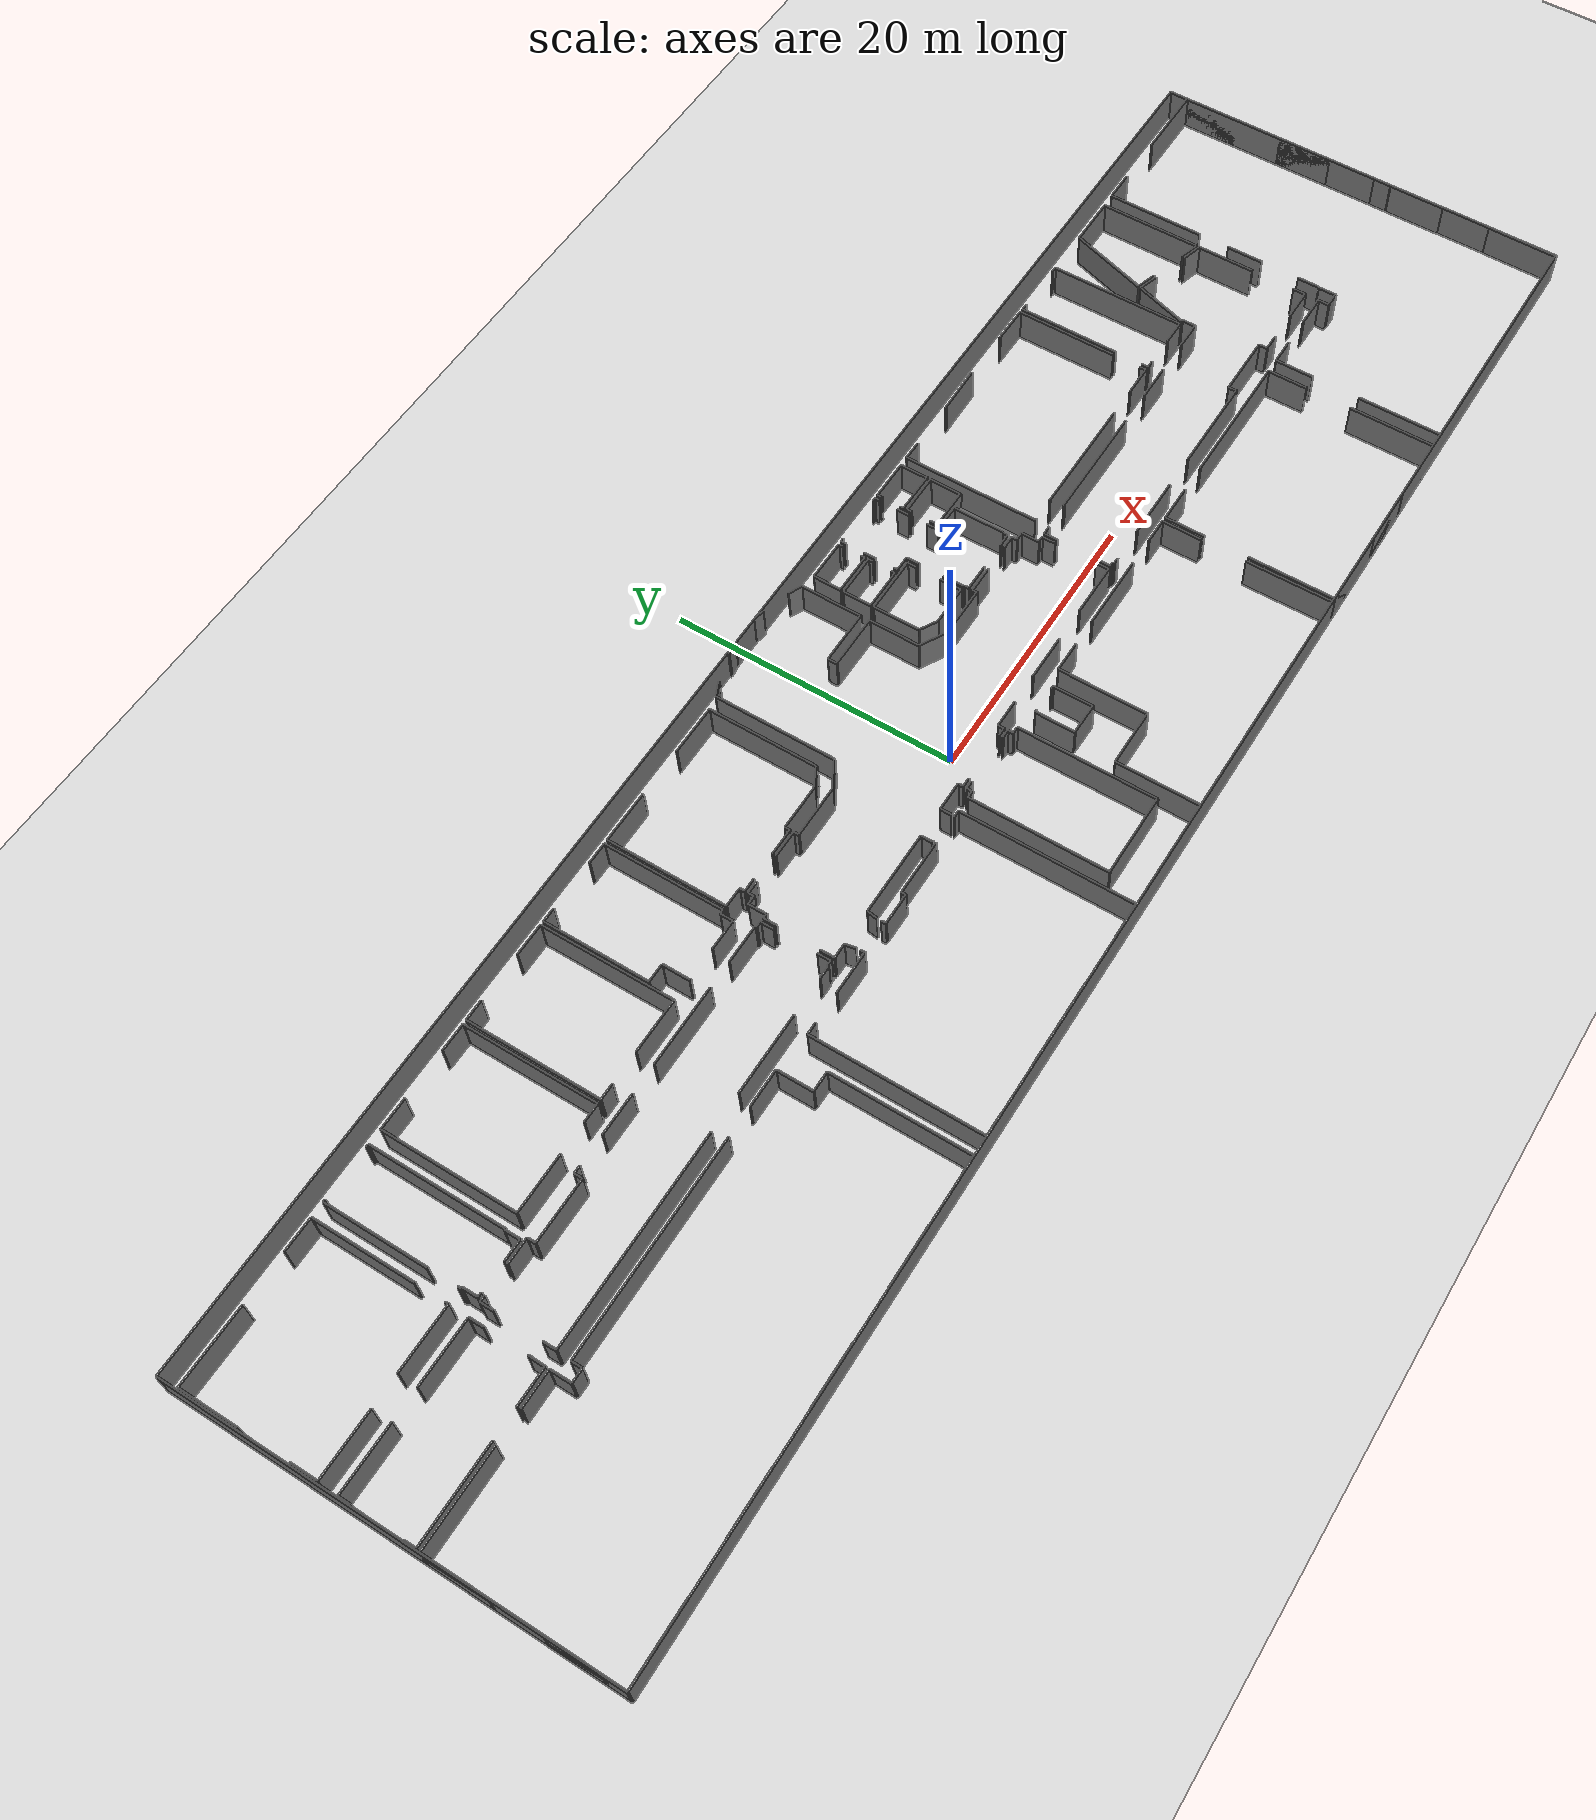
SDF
<sdf version="1.6">
  <world name="default">
    <light name="sun" type="directional">
      <cast_shadows>1</cast_shadows>
      <pose frame="">0 0 10 0 -0 0</pose>
      <diffuse>0.8 0.8 0.8 1</diffuse>
      <specular>0.1 0.1 0.1 1</specular>
      <attenuation>
        <range>1000</range>
        <constant>0.9</constant>
        <linear>0.01</linear>
        <quadratic>0.001</quadratic>
      </attenuation>
      <direction>-0.5 0.5 -1</direction>
    </light>
    <model name="ground_plane">
      <static>1</static>
      <link name="link">
        <collision name="collision">
          <geometry>
            <plane>
              <normal>0 0 1</normal>
              <size>100 100</size>
            </plane>
          </geometry>
          <surface>
            <friction>
              <ode>
                <mu>100</mu>
                <mu2>50</mu2>
              </ode>
              <torsional>
                <ode />
              </torsional>
            </friction>
            <contact>
              <ode />
            </contact>
            <bounce />
          </surface>
          <max_contacts>10</max_contacts>
        </collision>
        <visual name="visual">
          <cast_shadows>0</cast_shadows>
          <geometry>
            <plane>
              <normal>0 0 1</normal>
              <size>100 100</size>
            </plane>
          </geometry>
          <material>
            <script>
              <uri>file://media/materials/scripts/gazebo.material</uri>
              <name>Gazebo/Grey</name>
            </script>
          </material>
        </visual>
        <self_collide>0</self_collide>
        <kinematic>0</kinematic>
        <gravity>1</gravity>
      </link>
    </model>
    <gravity>0 0 -9.8</gravity>
    <magnetic_field>6e-06 2.3e-05 -4.2e-05</magnetic_field>
    <atmosphere type="adiabatic" />
    <physics default="0" name="default_physics" type="ode">
      <max_step_size>0.001</max_step_size>
      <real_time_factor>1</real_time_factor>
      <real_time_update_rate>1000</real_time_update_rate>
    </physics>
    <scene>
      <ambient>0.4 0.4 0.4 1</ambient>
      <background>0.7 0.7 0.7 1</background>
      <shadows>1</shadows>
    </scene>
    <spherical_coordinates>
      <surface_model>EARTH_WGS84</surface_model>
      <latitude_deg>0</latitude_deg>
      <longitude_deg>0</longitude_deg>
      <elevation>0</elevation>
      <heading_deg>0</heading_deg>
    </spherical_coordinates>
  <model name="50056457">
		<static>1</static>
		<link name="Wall_0">
			<collision name="Wall_0_Collision">
				<geometry>
					<box>
						<size>4.36631290074 0.1 2.5</size>
					</box>
				</geometry>
				<pose frame="">2.18315645037 0 1.25 0 0 0</pose>
			</collision>
			<visual name="Wall_0_Visual">
				<pose frame="">2.18315645037 0 1.25 0 0 0</pose>
				<geometry>
					<box>
						<size>4.36631290074 0.1 2.5</size>
					</box>
				</geometry>
				<material>
					<script>
						<uri>file://media/materials/scripts/gazebo.material</uri>
						<name>Gazebo/Grey</name>
					</script>
					<ambient>1 1 1 1</ambient>
				</material>
			</visual>
			<pose frame="">11.0454587805 -10.6294097219 0 0 0 3.14159265359</pose>
		</link>
		<link name="Wall_1">
			<collision name="Wall_1_Collision">
				<geometry>
					<box>
						<size>4.40476694646 0.1 2.5</size>
					</box>
				</geometry>
				<pose frame="">2.20238347323 0 1.25 0 0 0</pose>
			</collision>
			<visual name="Wall_1_Visual">
				<pose frame="">2.20238347323 0 1.25 0 0 0</pose>
				<geometry>
					<box>
						<size>4.40476694646 0.1 2.5</size>
					</box>
				</geometry>
				<material>
					<script>
						<uri>file://media/materials/scripts/gazebo.material</uri>
						<name>Gazebo/Grey</name>
					</script>
					<ambient>1 1 1 1</ambient>
				</material>
			</visual>
			<pose frame="">4.51945147929 -10.6294097219 0 0 0 3.14159265359</pose>
		</link>
		<link name="Wall_2">
			<collision name="Wall_2_Collision">
				<geometry>
					<box>
						<size>1.82783767988 0.1 2.5</size>
					</box>
				</geometry>
				<pose frame="">0.913918839941 0 1.25 0 0 0</pose>
			</collision>
			<visual name="Wall_2_Visual">
				<pose frame="">0.913918839941 0 1.25 0 0 0</pose>
				<geometry>
					<box>
						<size>1.82783767988 0.1 2.5</size>
					</box>
				</geometry>
				<material>
					<script>
						<uri>file://media/materials/scripts/gazebo.material</uri>
						<name>Gazebo/Grey</name>
					</script>
					<ambient>1 1 1 1</ambient>
				</material>
			</visual>
			<pose frame="">0.114684532834 -10.6294097219 0 0 0 1.57079632679</pose>
		</link>
		<link name="Wall_3">
			<collision name="Wall_3_Collision">
				<geometry>
					<box>
						<size>4.02632492822 0.1 2.5</size>
					</box>
				</geometry>
				<pose frame="">2.01316246411 0 1.25 0 0 0</pose>
			</collision>
			<visual name="Wall_3_Visual">
				<pose frame="">2.01316246411 0 1.25 0 0 0</pose>
				<geometry>
					<box>
						<size>4.02632492822 0.1 2.5</size>
					</box>
				</geometry>
				<material>
					<script>
						<uri>file://media/materials/scripts/gazebo.material</uri>
						<name>Gazebo/Grey</name>
					</script>
					<ambient>1 1 1 1</ambient>
				</material>
			</visual>
			<pose frame="">0.114684532834 -5.38221119233 0 0 0 1.57079632679</pose>
		</link>
		<link name="Wall_4">
			<collision name="Wall_4_Collision">
				<geometry>
					<box>
						<size>5.22212716939 0.1 2.5</size>
					</box>
				</geometry>
				<pose frame="">2.6110635847 0 1.25 0 0 0</pose>
			</collision>
			<visual name="Wall_4_Visual">
				<pose frame="">2.6110635847 0 1.25 0 0 0</pose>
				<geometry>
					<box>
						<size>5.22212716939 0.1 2.5</size>
					</box>
				</geometry>
				<material>
					<script>
						<uri>file://media/materials/scripts/gazebo.material</uri>
						<name>Gazebo/Grey</name>
					</script>
					<ambient>1 1 1 1</ambient>
				</material>
			</visual>
			<pose frame="">0.114684532834 -1.35588626411 0 0 0 0.0</pose>
		</link>
		<link name="Wall_5">
			<collision name="Wall_5_Collision">
				<geometry>
					<box>
						<size>2.28335719065 0.1 2.5</size>
					</box>
				</geometry>
				<pose frame="">1.14167859533 0 1.25 0 0 0</pose>
			</collision>
			<visual name="Wall_5_Visual">
				<pose frame="">1.14167859533 0 1.25 0 0 0</pose>
				<geometry>
					<box>
						<size>2.28335719065 0.1 2.5</size>
					</box>
				</geometry>
				<material>
					<script>
						<uri>file://media/materials/scripts/gazebo.material</uri>
						<name>Gazebo/Grey</name>
					</script>
					<ambient>1 1 1 1</ambient>
				</material>
			</visual>
			<pose frame="">8.75092111839 -1.35588626411 0 0 0 0.0</pose>
		</link>
		<link name="Wall_6">
			<collision name="Wall_6_Collision">
				<geometry>
					<box>
						<size>7.03251653778 0.1 2.5</size>
					</box>
				</geometry>
				<pose frame="">3.51625826889 0 1.25 0 0 0</pose>
			</collision>
			<visual name="Wall_6_Visual">
				<pose frame="">3.51625826889 0 1.25 0 0 0</pose>
				<geometry>
					<box>
						<size>7.03251653778 0.1 2.5</size>
					</box>
				</geometry>
				<material>
					<script>
						<uri>file://media/materials/scripts/gazebo.material</uri>
						<name>Gazebo/Grey</name>
					</script>
					<ambient>1 1 1 1</ambient>
				</material>
			</visual>
			<pose frame="">11.034278309 -1.35588626411 0 0 0 -1.57079632679</pose>
		</link>
		<link name="Wall_7">
			<collision name="Wall_7_Collision">
				<geometry>
					<box>
						<size>0.24165532 0.1 2.5</size>
					</box>
				</geometry>
				<pose frame="">0.12082766 0 1.25 0 0 0</pose>
			</collision>
			<visual name="Wall_7_Visual">
				<pose frame="">0.12082766 0 1.25 0 0 0</pose>
				<geometry>
					<box>
						<size>0.24165532 0.1 2.5</size>
					</box>
				</geometry>
				<material>
					<script>
						<uri>file://media/materials/scripts/gazebo.material</uri>
						<name>Gazebo/Grey</name>
					</script>
					<ambient>1 1 1 1</ambient>
				</material>
			</visual>
			<pose frame="">11.034278309 -10.3880131794 0 0 0 -1.5245136129</pose>
		</link>
		<link name="Wall_8">
			<collision name="Wall_8_Collision">
				<geometry>
					<box>
						<size>1.18919559896 0.1 2.5</size>
					</box>
				</geometry>
				<pose frame="">0.59459779948 0 1.25 0 0 0</pose>
			</collision>
			<visual name="Wall_8_Visual">
				<pose frame="">0.59459779948 0 1.25 0 0 0</pose>
				<geometry>
					<box>
						<size>1.18919559896 0.1 2.5</size>
					</box>
				</geometry>
				<material>
					<script>
						<uri>file://media/materials/scripts/gazebo.material</uri>
						<name>Gazebo/Grey</name>
					</script>
					<ambient>1 1 1 1</ambient>
				</material>
			</visual>
			<pose frame="">32.7157534537 -30.0129591828 0 0 0 3.14159265359</pose>
		</link>
		<link name="Wall_9">
			<collision name="Wall_9_Collision">
				<geometry>
					<box>
						<size>4.10679044239 0.1 2.5</size>
					</box>
				</geometry>
				<pose frame="">2.0533952212 0 1.25 0 0 0</pose>
			</collision>
			<visual name="Wall_9_Visual">
				<pose frame="">2.0533952212 0 1.25 0 0 0</pose>
				<geometry>
					<box>
						<size>4.10679044239 0.1 2.5</size>
					</box>
				</geometry>
				<material>
					<script>
						<uri>file://media/materials/scripts/gazebo.material</uri>
						<name>Gazebo/Grey</name>
					</script>
					<ambient>1 1 1 1</ambient>
				</material>
			</visual>
			<pose frame="">28.0301195125 -30.0129591828 0 0 0 3.14159265359</pose>
		</link>
		<link name="Wall_10">
			<collision name="Wall_10_Collision">
				<geometry>
					<box>
						<size>4.10662104131 0.1 2.5</size>
					</box>
				</geometry>
				<pose frame="">2.05331052065 0 1.25 0 0 0</pose>
			</collision>
			<visual name="Wall_10_Visual">
				<pose frame="">2.05331052065 0 1.25 0 0 0</pose>
				<geometry>
					<box>
						<size>4.10662104131 0.1 2.5</size>
					</box>
				</geometry>
				<material>
					<script>
						<uri>file://media/materials/scripts/gazebo.material</uri>
						<name>Gazebo/Grey</name>
					</script>
					<ambient>1 1 1 1</ambient>
				</material>
			</visual>
			<pose frame="">20.4268907278 -30.0129591828 0 0 0 3.14159265359</pose>
		</link>
		<link name="Wall_11">
			<collision name="Wall_11_Collision">
				<geometry>
					<box>
						<size>4.1743814743 0.1 2.5</size>
					</box>
				</geometry>
				<pose frame="">2.08719073715 0 1.25 0 0 0</pose>
			</collision>
			<visual name="Wall_11_Visual">
				<pose frame="">2.08719073715 0 1.25 0 0 0</pose>
				<geometry>
					<box>
						<size>4.1743814743 0.1 2.5</size>
					</box>
				</geometry>
				<material>
					<script>
						<uri>file://media/materials/scripts/gazebo.material</uri>
						<name>Gazebo/Grey</name>
					</script>
					<ambient>1 1 1 1</ambient>
				</material>
			</visual>
			<pose frame="">12.8140060815 -30.0129591828 0 0 0 3.14159265359</pose>
		</link>
		<link name="Wall_12">
			<collision name="Wall_12_Collision">
				<geometry>
					<box>
						<size>5.26905126924 0.1 2.5</size>
					</box>
				</geometry>
				<pose frame="">2.63452563462 0 1.25 0 0 0</pose>
			</collision>
			<visual name="Wall_12_Visual">
				<pose frame="">2.63452563462 0 1.25 0 0 0</pose>
				<geometry>
					<box>
						<size>5.26905126924 0.1 2.5</size>
					</box>
				</geometry>
				<material>
					<script>
						<uri>file://media/materials/scripts/gazebo.material</uri>
						<name>Gazebo/Grey</name>
					</script>
					<ambient>1 1 1 1</ambient>
				</material>
			</visual>
			<pose frame="">5.26905126924 -30.0129591828 0 0 0 3.14159265359</pose>
		</link>
		<link name="Wall_13">
			<collision name="Wall_13_Collision">
				<geometry>
					<box>
						<size>5.03222855594 0.1 2.5</size>
					</box>
				</geometry>
				<pose frame="">2.51611427797 0 1.25 0 0 0</pose>
			</collision>
			<visual name="Wall_13_Visual">
				<pose frame="">2.51611427797 0 1.25 0 0 0</pose>
				<geometry>
					<box>
						<size>5.03222855594 0.1 2.5</size>
					</box>
				</geometry>
				<material>
					<script>
						<uri>file://media/materials/scripts/gazebo.material</uri>
						<name>Gazebo/Grey</name>
					</script>
					<ambient>1 1 1 1</ambient>
				</material>
			</visual>
			<pose frame="">0.0 -30.0129591828 0 0 0 1.57079632679</pose>
		</link>
		<link name="Wall_14">
			<collision name="Wall_14_Collision">
				<geometry>
					<box>
						<size>4.33903932646 0.1 2.5</size>
					</box>
				</geometry>
				<pose frame="">2.16951966323 0 1.25 0 0 0</pose>
			</collision>
			<visual name="Wall_14_Visual">
				<pose frame="">2.16951966323 0 1.25 0 0 0</pose>
				<geometry>
					<box>
						<size>4.33903932646 0.1 2.5</size>
					</box>
				</geometry>
				<material>
					<script>
						<uri>file://media/materials/scripts/gazebo.material</uri>
						<name>Gazebo/Grey</name>
					</script>
					<ambient>1 1 1 1</ambient>
				</material>
			</visual>
			<pose frame="">0.0 -21.5889821536 0 0 0 1.57079632679</pose>
		</link>
		<link name="Wall_15">
			<collision name="Wall_15_Collision">
				<geometry>
					<box>
						<size>6.34407053861 0.1 2.5</size>
					</box>
				</geometry>
				<pose frame="">3.17203526931 0 1.25 0 0 0</pose>
			</collision>
			<visual name="Wall_15_Visual">
				<pose frame="">3.17203526931 0 1.25 0 0 0</pose>
				<geometry>
					<box>
						<size>6.34407053861 0.1 2.5</size>
					</box>
				</geometry>
				<material>
					<script>
						<uri>file://media/materials/scripts/gazebo.material</uri>
						<name>Gazebo/Grey</name>
					</script>
					<ambient>1 1 1 1</ambient>
				</material>
			</visual>
			<pose frame="">0.0 -17.2499428271 0 0 0 0.0</pose>
		</link>
		<link name="Wall_16">
			<collision name="Wall_16_Collision">
				<geometry>
					<box>
						<size>2.48274226472 0.1 2.5</size>
					</box>
				</geometry>
				<pose frame="">1.24137113236 0 1.25 0 0 0</pose>
			</collision>
			<visual name="Wall_16_Visual">
				<pose frame="">1.24137113236 0 1.25 0 0 0</pose>
				<geometry>
					<box>
						<size>2.48274226472 0.1 2.5</size>
					</box>
				</geometry>
				<material>
					<script>
						<uri>file://media/materials/scripts/gazebo.material</uri>
						<name>Gazebo/Grey</name>
					</script>
					<ambient>1 1 1 1</ambient>
				</material>
			</visual>
			<pose frame="">8.50461194447 -17.2499428271 0 0 0 0.0</pose>
		</link>
		<link name="Wall_17">
			<collision name="Wall_17_Collision">
				<geometry>
					<box>
						<size>1.44922626056 0.1 2.5</size>
					</box>
				</geometry>
				<pose frame="">0.724613130278 0 1.25 0 0 0</pose>
			</collision>
			<visual name="Wall_17_Visual">
				<pose frame="">0.724613130278 0 1.25 0 0 0</pose>
				<geometry>
					<box>
						<size>1.44922626056 0.1 2.5</size>
					</box>
				</geometry>
				<material>
					<script>
						<uri>file://media/materials/scripts/gazebo.material</uri>
						<name>Gazebo/Grey</name>
					</script>
					<ambient>1 1 1 1</ambient>
				</material>
			</visual>
			<pose frame="">10.9873542092 -17.2499428271 0 0 0 -1.57079632679</pose>
		</link>
		<link name="Wall_18">
			<collision name="Wall_18_Collision">
				<geometry>
					<box>
						<size>0.944749836951 0.1 2.5</size>
					</box>
				</geometry>
				<pose frame="">0.472374918476 0 1.25 0 0 0</pose>
			</collision>
			<visual name="Wall_18_Visual">
				<pose frame="">0.472374918476 0 1.25 0 0 0</pose>
				<geometry>
					<box>
						<size>0.944749836951 0.1 2.5</size>
					</box>
				</geometry>
				<material>
					<script>
						<uri>file://media/materials/scripts/gazebo.material</uri>
						<name>Gazebo/Grey</name>
					</script>
					<ambient>1 1 1 1</ambient>
				</material>
			</visual>
			<pose frame="">10.9873542092 -18.6991690877 0 0 0 0.0</pose>
		</link>
		<link name="Wall_19">
			<collision name="Wall_19_Collision">
				<geometry>
					<box>
						<size>0.739605126077 0.1 2.5</size>
					</box>
				</geometry>
				<pose frame="">0.369802563038 0 1.25 0 0 0</pose>
			</collision>
			<visual name="Wall_19_Visual">
				<pose frame="">0.369802563038 0 1.25 0 0 0</pose>
				<geometry>
					<box>
						<size>0.739605126077 0.1 2.5</size>
					</box>
				</geometry>
				<material>
					<script>
						<uri>file://media/materials/scripts/gazebo.material</uri>
						<name>Gazebo/Grey</name>
					</script>
					<ambient>1 1 1 1</ambient>
				</material>
			</visual>
			<pose frame="">11.9321040461 -18.6991690877 0 0 0 1.57079632679</pose>
		</link>
		<link name="Wall_20">
			<collision name="Wall_20_Collision">
				<geometry>
					<box>
						<size>14.6838552298 0.1 2.5</size>
					</box>
				</geometry>
				<pose frame="">7.34192761492 0 1.25 0 0 0</pose>
			</collision>
			<visual name="Wall_20_Visual">
				<pose frame="">7.34192761492 0 1.25 0 0 0</pose>
				<geometry>
					<box>
						<size>14.6838552298 0.1 2.5</size>
					</box>
				</geometry>
				<material>
					<script>
						<uri>file://media/materials/scripts/gazebo.material</uri>
						<name>Gazebo/Grey</name>
					</script>
					<ambient>1 1 1 1</ambient>
				</material>
			</visual>
			<pose frame="">11.9321040461 -17.9595639616 0 0 0 0.0</pose>
		</link>
		<link name="Wall_21">
			<collision name="Wall_21_Collision">
				<geometry>
					<box>
						<size>2.6289353989 0.1 2.5</size>
					</box>
				</geometry>
				<pose frame="">1.31446769945 0 1.25 0 0 0</pose>
			</collision>
			<visual name="Wall_21_Visual">
				<pose frame="">1.31446769945 0 1.25 0 0 0</pose>
				<geometry>
					<box>
						<size>2.6289353989 0.1 2.5</size>
					</box>
				</geometry>
				<material>
					<script>
						<uri>file://media/materials/scripts/gazebo.material</uri>
						<name>Gazebo/Grey</name>
					</script>
					<ambient>1 1 1 1</ambient>
				</material>
			</visual>
			<pose frame="">28.6984067828 -17.9595639616 0 0 0 0.0</pose>
		</link>
		<link name="Wall_22">
			<collision name="Wall_22_Collision">
				<geometry>
					<box>
						<size>2.49832716431 0.1 2.5</size>
					</box>
				</geometry>
				<pose frame="">1.24916358216 0 1.25 0 0 0</pose>
			</collision>
			<visual name="Wall_22_Visual">
				<pose frame="">1.24916358216 0 1.25 0 0 0</pose>
				<geometry>
					<box>
						<size>2.49832716431 0.1 2.5</size>
					</box>
				</geometry>
				<material>
					<script>
						<uri>file://media/materials/scripts/gazebo.material</uri>
						<name>Gazebo/Grey</name>
					</script>
					<ambient>1 1 1 1</ambient>
				</material>
			</visual>
			<pose frame="">31.3273421817 -17.9595639616 0 0 0 -1.57079632679</pose>
		</link>
		<link name="Wall_23">
			<collision name="Wall_23_Collision">
				<geometry>
					<box>
						<size>1.38129642648 0.1 2.5</size>
					</box>
				</geometry>
				<pose frame="">0.690648213242 0 1.25 0 0 0</pose>
			</collision>
			<visual name="Wall_23_Visual">
				<pose frame="">0.690648213242 0 1.25 0 0 0</pose>
				<geometry>
					<box>
						<size>1.38129642648 0.1 2.5</size>
					</box>
				</geometry>
				<material>
					<script>
						<uri>file://media/materials/scripts/gazebo.material</uri>
						<name>Gazebo/Grey</name>
					</script>
					<ambient>1 1 1 1</ambient>
				</material>
			</visual>
			<pose frame="">31.3273421817 -20.4578911259 0 0 0 0.0</pose>
		</link>
		<link name="Wall_24">
			<collision name="Wall_24_Collision">
				<geometry>
					<box>
						<size>9.55507070579 0.1 2.5</size>
					</box>
				</geometry>
				<pose frame="">4.7775353529 0 1.25 0 0 0</pose>
			</collision>
			<visual name="Wall_24_Visual">
				<pose frame="">4.7775353529 0 1.25 0 0 0</pose>
				<geometry>
					<box>
						<size>9.55507070579 0.1 2.5</size>
					</box>
				</geometry>
				<material>
					<script>
						<uri>file://media/materials/scripts/gazebo.material</uri>
						<name>Gazebo/Grey</name>
					</script>
					<ambient>1 1 1 1</ambient>
				</material>
			</visual>
			<pose frame="">32.7086386082 -20.4578911259 0 0 0 -1.57005171209</pose>
		</link>
		<link name="Wall_25">
			<collision name="Wall_25_Collision">
				<geometry>
					<box>
						<size>2.50561141086 0.1 2.5</size>
					</box>
				</geometry>
				<pose frame="">1.25280570543 0 1.25 0 0 0</pose>
			</collision>
			<visual name="Wall_25_Visual">
				<pose frame="">1.25280570543 0 1.25 0 0 0</pose>
				<geometry>
					<box>
						<size>2.50561141086 0.1 2.5</size>
					</box>
				</geometry>
				<material>
					<script>
						<uri>file://media/materials/scripts/gazebo.material</uri>
						<name>Gazebo/Grey</name>
					</script>
					<ambient>1 1 1 1</ambient>
				</material>
			</visual>
			<pose frame="">10.9834579843 -16.9883875558 0 0 0 3.14159265359</pose>
		</link>
		<link name="Wall_26">
			<collision name="Wall_26_Collision">
				<geometry>
					<box>
						<size>6.38625140815 0.1 2.5</size>
					</box>
				</geometry>
				<pose frame="">3.19312570407 0 1.25 0 0 0</pose>
			</collision>
			<visual name="Wall_26_Visual">
				<pose frame="">3.19312570407 0 1.25 0 0 0</pose>
				<geometry>
					<box>
						<size>6.38625140815 0.1 2.5</size>
					</box>
				</geometry>
				<material>
					<script>
						<uri>file://media/materials/scripts/gazebo.material</uri>
						<name>Gazebo/Grey</name>
					</script>
					<ambient>1 1 1 1</ambient>
				</material>
			</visual>
			<pose frame="">6.45401184114 -16.9883875558 0 0 0 3.14159265359</pose>
		</link>
		<link name="Wall_27">
			<collision name="Wall_27_Collision">
				<geometry>
					<box>
						<size>0.786529225922 0.1 2.5</size>
					</box>
				</geometry>
				<pose frame="">0.393264612961 0 1.25 0 0 0</pose>
			</collision>
			<visual name="Wall_27_Visual">
				<pose frame="">0.393264612961 0 1.25 0 0 0</pose>
				<geometry>
					<box>
						<size>0.786529225922 0.1 2.5</size>
					</box>
				</geometry>
				<material>
					<script>
						<uri>file://media/materials/scripts/gazebo.material</uri>
						<name>Gazebo/Grey</name>
					</script>
					<ambient>1 1 1 1</ambient>
				</material>
			</visual>
			<pose frame="">0.0677604329892 -16.9883875558 0 0 0 1.57079632679</pose>
		</link>
		<link name="Wall_28">
			<collision name="Wall_28_Collision">
				<geometry>
					<box>
						<size>0.842770385303 0.1 2.5</size>
					</box>
				</geometry>
				<pose frame="">0.421385192651 0 1.25 0 0 0</pose>
			</collision>
			<visual name="Wall_28_Visual">
				<pose frame="">0.421385192651 0 1.25 0 0 0</pose>
				<geometry>
					<box>
						<size>0.842770385303 0.1 2.5</size>
					</box>
				</geometry>
				<material>
					<script>
						<uri>file://media/materials/scripts/gazebo.material</uri>
						<name>Gazebo/Grey</name>
					</script>
					<ambient>1 1 1 1</ambient>
				</material>
			</visual>
			<pose frame="">0.0677604329892 -12.8140060815 0 0 0 1.57079632679</pose>
		</link>
		<link name="Wall_29">
			<collision name="Wall_29_Collision">
				<geometry>
					<box>
						<size>4.45541787012 0.1 2.5</size>
					</box>
				</geometry>
				<pose frame="">2.22770893506 0 1.25 0 0 0</pose>
			</collision>
			<visual name="Wall_29_Visual">
				<pose frame="">2.22770893506 0 1.25 0 0 0</pose>
				<geometry>
					<box>
						<size>4.45541787012 0.1 2.5</size>
					</box>
				</geometry>
				<material>
					<script>
						<uri>file://media/materials/scripts/gazebo.material</uri>
						<name>Gazebo/Grey</name>
					</script>
					<ambient>1 1 1 1</ambient>
				</material>
			</visual>
			<pose frame="">0.0677604329892 -11.9712356962 0 0 0 0.0</pose>
		</link>
		<link name="Wall_30">
			<collision name="Wall_30_Collision">
				<geometry>
					<box>
						<size>4.39968491399 0.1 2.5</size>
					</box>
				</geometry>
				<pose frame="">2.19984245699 0 1.25 0 0 0</pose>
			</collision>
			<visual name="Wall_30_Visual">
				<pose frame="">2.19984245699 0 1.25 0 0 0</pose>
				<geometry>
					<box>
						<size>4.39968491399 0.1 2.5</size>
					</box>
				</geometry>
				<material>
					<script>
						<uri>file://media/materials/scripts/gazebo.material</uri>
						<name>Gazebo/Grey</name>
					</script>
					<ambient>1 1 1 1</ambient>
				</material>
			</visual>
			<pose frame="">6.61240185325 -11.9712356962 0 0 0 0.0</pose>
		</link>
		<link name="Wall_31">
			<collision name="Wall_31_Collision">
				<geometry>
					<box>
						<size>1.03300780092 0.1 2.5</size>
					</box>
				</geometry>
				<pose frame="">0.51650390046 0 1.25 0 0 0</pose>
			</collision>
			<visual name="Wall_31_Visual">
				<pose frame="">0.51650390046 0 1.25 0 0 0</pose>
				<geometry>
					<box>
						<size>1.03300780092 0.1 2.5</size>
					</box>
				</geometry>
				<material>
					<script>
						<uri>file://media/materials/scripts/gazebo.material</uri>
						<name>Gazebo/Grey</name>
					</script>
					<ambient>1 1 1 1</ambient>
				</material>
			</visual>
			<pose frame="">11.0120867672 -11.9712356962 0 0 0 -1.57079632679</pose>
		</link>
		<link name="Wall_32">
			<collision name="Wall_32_Collision">
				<geometry>
					<box>
						<size>1.13348544123 0.1 2.5</size>
					</box>
				</geometry>
				<pose frame="">0.566742720617 0 1.25 0 0 0</pose>
			</collision>
			<visual name="Wall_32_Visual">
				<pose frame="">0.566742720617 0 1.25 0 0 0</pose>
				<geometry>
					<box>
						<size>1.13348544123 0.1 2.5</size>
					</box>
				</geometry>
				<material>
					<script>
						<uri>file://media/materials/scripts/gazebo.material</uri>
						<name>Gazebo/Grey</name>
					</script>
					<ambient>1 1 1 1</ambient>
				</material>
			</visual>
			<pose frame="">11.0120867672 -15.8552637151 0 0 0 -1.59605631394</pose>
		</link>
		<link name="Wall_33">
			<collision name="Wall_33_Collision">
				<geometry>
					<box>
						<size>0.412661036904 0.1 2.5</size>
					</box>
				</geometry>
				<pose frame="">0.206330518452 0 1.25 0 0 0</pose>
			</collision>
			<visual name="Wall_33_Visual">
				<pose frame="">0.206330518452 0 1.25 0 0 0</pose>
				<geometry>
					<box>
						<size>0.412661036904 0.1 2.5</size>
					</box>
				</geometry>
				<material>
					<script>
						<uri>file://media/materials/scripts/gazebo.material</uri>
						<name>Gazebo/Grey</name>
					</script>
					<ambient>1 1 1 1</ambient>
				</material>
			</visual>
			<pose frame="">38.6041350804 -16.9038564156 0 0 0 3.14159265359</pose>
		</link>
		<link name="Wall_34">
			<collision name="Wall_34_Collision">
				<geometry>
					<box>
						<size>0.0672522297417 0.1 2.5</size>
					</box>
				</geometry>
				<pose frame="">0.0336261148709 0 1.25 0 0 0</pose>
			</collision>
			<visual name="Wall_34_Visual">
				<pose frame="">0.0336261148709 0 1.25 0 0 0</pose>
				<geometry>
					<box>
						<size>0.0672522297417 0.1 2.5</size>
					</box>
				</geometry>
				<material>
					<script>
						<uri>file://media/materials/scripts/gazebo.material</uri>
						<name>Gazebo/Grey</name>
					</script>
					<ambient>1 1 1 1</ambient>
				</material>
			</visual>
			<pose frame="">38.1914740435 -16.9038564156 0 0 0 -1.57079632679</pose>
		</link>
		<link name="Wall_35">
			<collision name="Wall_35_Collision">
				<geometry>
					<box>
						<size>0.875803596385 0.1 2.5</size>
					</box>
				</geometry>
				<pose frame="">0.437901798192 0 1.25 0 0 0</pose>
			</collision>
			<visual name="Wall_35_Visual">
				<pose frame="">0.437901798192 0 1.25 0 0 0</pose>
				<geometry>
					<box>
						<size>0.875803596385 0.1 2.5</size>
					</box>
				</geometry>
				<material>
					<script>
						<uri>file://media/materials/scripts/gazebo.material</uri>
						<name>Gazebo/Grey</name>
					</script>
					<ambient>1 1 1 1</ambient>
				</material>
			</visual>
			<pose frame="">38.1914740435 -16.9711086454 0 0 0 3.14159265359</pose>
		</link>
		<link name="Wall_36">
			<collision name="Wall_36_Collision">
				<geometry>
					<box>
						<size>5.60260200063 0.1 2.5</size>
					</box>
				</geometry>
				<pose frame="">2.80130100031 0 1.25 0 0 0</pose>
			</collision>
			<visual name="Wall_36_Visual">
				<pose frame="">2.80130100031 0 1.25 0 0 0</pose>
				<geometry>
					<box>
						<size>5.60260200063 0.1 2.5</size>
					</box>
				</geometry>
				<material>
					<script>
						<uri>file://media/materials/scripts/gazebo.material</uri>
						<name>Gazebo/Grey</name>
					</script>
					<ambient>1 1 1 1</ambient>
				</material>
			</visual>
			<pose frame="">34.6699643411 -16.9711086454 0 0 0 3.14159265359</pose>
		</link>
		<link name="Wall_37">
			<collision name="Wall_37_Collision">
				<geometry>
					<box>
						<size>14.3640259861 0.1 2.5</size>
					</box>
				</geometry>
				<pose frame="">7.18201299306 0 1.25 0 0 0</pose>
			</collision>
			<visual name="Wall_37_Visual">
				<pose frame="">7.18201299306 0 1.25 0 0 0</pose>
				<geometry>
					<box>
						<size>14.3640259861 0.1 2.5</size>
					</box>
				</geometry>
				<material>
					<script>
						<uri>file://media/materials/scripts/gazebo.material</uri>
						<name>Gazebo/Grey</name>
					</script>
					<ambient>1 1 1 1</ambient>
				</material>
			</visual>
			<pose frame="">26.3623658555 -16.9711086454 0 0 0 3.14159265359</pose>
		</link>
		<link name="Wall_38">
			<collision name="Wall_38_Collision">
				<geometry>
					<box>
						<size>0.892743704632 0.1 2.5</size>
					</box>
				</geometry>
				<pose frame="">0.446371852316 0 1.25 0 0 0</pose>
			</collision>
			<visual name="Wall_38_Visual">
				<pose frame="">0.446371852316 0 1.25 0 0 0</pose>
				<geometry>
					<box>
						<size>0.892743704632 0.1 2.5</size>
					</box>
				</geometry>
				<material>
					<script>
						<uri>file://media/materials/scripts/gazebo.material</uri>
						<name>Gazebo/Grey</name>
					</script>
					<ambient>1 1 1 1</ambient>
				</material>
			</visual>
			<pose frame="">11.9983398694 -16.9711086454 0 0 0 1.57079632679</pose>
		</link>
		<link name="Wall_39">
			<collision name="Wall_39_Collision">
				<geometry>
					<box>
						<size>0.920186679993 0.1 2.5</size>
					</box>
				</geometry>
				<pose frame="">0.460093339996 0 1.25 0 0 0</pose>
			</collision>
			<visual name="Wall_39_Visual">
				<pose frame="">0.460093339996 0 1.25 0 0 0</pose>
				<geometry>
					<box>
						<size>0.920186679993 0.1 2.5</size>
					</box>
				</geometry>
				<material>
					<script>
						<uri>file://media/materials/scripts/gazebo.material</uri>
						<name>Gazebo/Grey</name>
					</script>
					<ambient>1 1 1 1</ambient>
				</material>
			</visual>
			<pose frame="">11.9983398694 -12.8914223762 0 0 0 1.57079632679</pose>
		</link>
		<link name="Wall_40">
			<collision name="Wall_40_Collision">
				<geometry>
					<box>
						<size>0.40893421309 0.1 2.5</size>
					</box>
				</geometry>
				<pose frame="">0.204467106545 0 1.25 0 0 0</pose>
			</collision>
			<visual name="Wall_40_Visual">
				<pose frame="">0.204467106545 0 1.25 0 0 0</pose>
				<geometry>
					<box>
						<size>0.40893421309 0.1 2.5</size>
					</box>
				</geometry>
				<material>
					<script>
						<uri>file://media/materials/scripts/gazebo.material</uri>
						<name>Gazebo/Grey</name>
					</script>
					<ambient>1 1 1 1</ambient>
				</material>
			</visual>
			<pose frame="">11.9983398694 -11.9712356962 0 0 0 0.0</pose>
		</link>
		<link name="Wall_41">
			<collision name="Wall_41_Collision">
				<geometry>
					<box>
						<size>1.74923557762 0.1 2.5</size>
					</box>
				</geometry>
				<pose frame="">0.874617788808 0 1.25 0 0 0</pose>
			</collision>
			<visual name="Wall_41_Visual">
				<pose frame="">0.874617788808 0 1.25 0 0 0</pose>
				<geometry>
					<box>
						<size>1.74923557762 0.1 2.5</size>
					</box>
				</geometry>
				<material>
					<script>
						<uri>file://media/materials/scripts/gazebo.material</uri>
						<name>Gazebo/Grey</name>
					</script>
					<ambient>1 1 1 1</ambient>
				</material>
			</visual>
			<pose frame="">14.4256879801 -11.9712356962 0 0 0 0.0</pose>
		</link>
		<link name="Wall_42">
			<collision name="Wall_42_Collision">
				<geometry>
					<box>
						<size>0.571559252264 0.1 2.5</size>
					</box>
				</geometry>
				<pose frame="">0.285779626132 0 1.25 0 0 0</pose>
			</collision>
			<visual name="Wall_42_Visual">
				<pose frame="">0.285779626132 0 1.25 0 0 0</pose>
				<geometry>
					<box>
						<size>0.571559252264 0.1 2.5</size>
					</box>
				</geometry>
				<material>
					<script>
						<uri>file://media/materials/scripts/gazebo.material</uri>
						<name>Gazebo/Grey</name>
					</script>
					<ambient>1 1 1 1</ambient>
				</material>
			</visual>
			<pose frame="">16.1749235578 -11.9712356962 0 0 0 -1.57079632679</pose>
		</link>
		<link name="Wall_43">
			<collision name="Wall_43_Collision">
				<geometry>
					<box>
						<size>4.29076001796 0.1 2.5</size>
					</box>
				</geometry>
				<pose frame="">2.14538000898 0 1.25 0 0 0</pose>
			</collision>
			<visual name="Wall_43_Visual">
				<pose frame="">2.14538000898 0 1.25 0 0 0</pose>
				<geometry>
					<box>
						<size>4.29076001796 0.1 2.5</size>
					</box>
				</geometry>
				<material>
					<script>
						<uri>file://media/materials/scripts/gazebo.material</uri>
						<name>Gazebo/Grey</name>
					</script>
					<ambient>1 1 1 1</ambient>
				</material>
			</visual>
			<pose frame="">16.1749235578 -12.5427949485 0 0 0 0.0</pose>
		</link>
		<link name="Wall_44">
			<collision name="Wall_44_Collision">
				<geometry>
					<box>
						<size>0.571559252264 0.1 2.5</size>
					</box>
				</geometry>
				<pose frame="">0.285779626132 0 1.25 0 0 0</pose>
			</collision>
			<visual name="Wall_44_Visual">
				<pose frame="">0.285779626132 0 1.25 0 0 0</pose>
				<geometry>
					<box>
						<size>0.571559252264 0.1 2.5</size>
					</box>
				</geometry>
				<material>
					<script>
						<uri>file://media/materials/scripts/gazebo.material</uri>
						<name>Gazebo/Grey</name>
					</script>
					<ambient>1 1 1 1</ambient>
				</material>
			</visual>
			<pose frame="">20.4656835757 -12.5427949485 0 0 0 1.57079632679</pose>
		</link>
		<link name="Wall_45">
			<collision name="Wall_45_Collision">
				<geometry>
					<box>
						<size>0.522941141594 0.1 2.5</size>
					</box>
				</geometry>
				<pose frame="">0.261470570797 0 1.25 0 0 0</pose>
			</collision>
			<visual name="Wall_45_Visual">
				<pose frame="">0.261470570797 0 1.25 0 0 0</pose>
				<geometry>
					<box>
						<size>0.522941141594 0.1 2.5</size>
					</box>
				</geometry>
				<material>
					<script>
						<uri>file://media/materials/scripts/gazebo.material</uri>
						<name>Gazebo/Grey</name>
					</script>
					<ambient>1 1 1 1</ambient>
				</material>
			</visual>
			<pose frame="">20.4656835757 -11.9712356962 0 0 0 0.0</pose>
		</link>
		<link name="Wall_46">
			<collision name="Wall_46_Collision">
				<geometry>
					<box>
						<size>2.87202595225 0.1 2.5</size>
					</box>
				</geometry>
				<pose frame="">1.43601297612 0 1.25 0 0 0</pose>
			</collision>
			<visual name="Wall_46_Visual">
				<pose frame="">1.43601297612 0 1.25 0 0 0</pose>
				<geometry>
					<box>
						<size>2.87202595225 0.1 2.5</size>
					</box>
				</geometry>
				<material>
					<script>
						<uri>file://media/materials/scripts/gazebo.material</uri>
						<name>Gazebo/Grey</name>
					</script>
					<ambient>1 1 1 1</ambient>
				</material>
			</visual>
			<pose frame="">23.0988540017 -11.9712356962 0 0 0 0.0</pose>
		</link>
		<link name="Wall_47">
			<collision name="Wall_47_Collision">
				<geometry>
					<box>
						<size>5.58617009563 0.1 2.5</size>
					</box>
				</geometry>
				<pose frame="">2.79308504781 0 1.25 0 0 0</pose>
			</collision>
			<visual name="Wall_47_Visual">
				<pose frame="">2.79308504781 0 1.25 0 0 0</pose>
				<geometry>
					<box>
						<size>5.58617009563 0.1 2.5</size>
					</box>
				</geometry>
				<material>
					<script>
						<uri>file://media/materials/scripts/gazebo.material</uri>
						<name>Gazebo/Grey</name>
					</script>
					<ambient>1 1 1 1</ambient>
				</material>
			</visual>
			<pose frame="">28.0368955558 -11.9712356962 0 0 0 0.0</pose>
		</link>
		<link name="Wall_48">
			<collision name="Wall_48_Collision">
				<geometry>
					<box>
						<size>2.67704530632 0.1 2.5</size>
					</box>
				</geometry>
				<pose frame="">1.33852265316 0 1.25 0 0 0</pose>
			</collision>
			<visual name="Wall_48_Visual">
				<pose frame="">1.33852265316 0 1.25 0 0 0</pose>
				<geometry>
					<box>
						<size>2.67704530632 0.1 2.5</size>
					</box>
				</geometry>
				<material>
					<script>
						<uri>file://media/materials/scripts/gazebo.material</uri>
						<name>Gazebo/Grey</name>
					</script>
					<ambient>1 1 1 1</ambient>
				</material>
			</visual>
			<pose frame="">35.49765803 -11.9712356962 0 0 0 0.0</pose>
		</link>
		<link name="Wall_49">
			<collision name="Wall_49_Collision">
				<geometry>
					<box>
						<size>0.106553280875 0.1 2.5</size>
					</box>
				</geometry>
				<pose frame="">0.0532766404377 0 1.25 0 0 0</pose>
			</collision>
			<visual name="Wall_49_Visual">
				<pose frame="">0.0532766404377 0 1.25 0 0 0</pose>
				<geometry>
					<box>
						<size>0.106553280875 0.1 2.5</size>
					</box>
				</geometry>
				<material>
					<script>
						<uri>file://media/materials/scripts/gazebo.material</uri>
						<name>Gazebo/Grey</name>
					</script>
					<ambient>1 1 1 1</ambient>
				</material>
			</visual>
			<pose frame="">38.1747033364 -11.9712356962 0 0 0 -1.57079632679</pose>
		</link>
		<link name="Wall_50">
			<collision name="Wall_50_Collision">
				<geometry>
					<box>
						<size>0.421131091028 0.1 2.5</size>
					</box>
				</geometry>
				<pose frame="">0.210565545514 0 1.25 0 0 0</pose>
			</collision>
			<visual name="Wall_50_Visual">
				<pose frame="">0.210565545514 0 1.25 0 0 0</pose>
				<geometry>
					<box>
						<size>0.421131091028 0.1 2.5</size>
					</box>
				</geometry>
				<material>
					<script>
						<uri>file://media/materials/scripts/gazebo.material</uri>
						<name>Gazebo/Grey</name>
					</script>
					<ambient>1 1 1 1</ambient>
				</material>
			</visual>
			<pose frame="">38.1747033364 -12.0777889771 0 0 0 0.0</pose>
		</link>
		<link name="Wall_51">
			<collision name="Wall_51_Collision">
				<geometry>
					<box>
						<size>0.892743704632 0.1 2.5</size>
					</box>
				</geometry>
				<pose frame="">0.446371852316 0 1.25 0 0 0</pose>
			</collision>
			<visual name="Wall_51_Visual">
				<pose frame="">0.446371852316 0 1.25 0 0 0</pose>
				<geometry>
					<box>
						<size>0.892743704632 0.1 2.5</size>
					</box>
				</geometry>
				<material>
					<script>
						<uri>file://media/materials/scripts/gazebo.material</uri>
						<name>Gazebo/Grey</name>
					</script>
					<ambient>1 1 1 1</ambient>
				</material>
			</visual>
			<pose frame="">38.5958344274 -12.0777889771 0 0 0 -1.57079632679</pose>
		</link>
		<link name="Wall_52">
			<collision name="Wall_52_Collision">
				<geometry>
					<box>
						<size>0.934961421784 0.1 2.5</size>
					</box>
				</geometry>
				<pose frame="">0.467480710892 0 1.25 0 0 0</pose>
			</collision>
			<visual name="Wall_52_Visual">
				<pose frame="">0.467480710892 0 1.25 0 0 0</pose>
				<geometry>
					<box>
						<size>0.934961421784 0.1 2.5</size>
					</box>
				</geometry>
				<material>
					<script>
						<uri>file://media/materials/scripts/gazebo.material</uri>
						<name>Gazebo/Grey</name>
					</script>
					<ambient>1 1 1 1</ambient>
				</material>
			</visual>
			<pose frame="">38.5958344274 -15.9689318415 0 0 0 -1.56191814006</pose>
		</link>
		<link name="Wall_53">
			<collision name="Wall_53_Collision">
				<geometry>
					<box>
						<size>1.47209540669 0.1 2.5</size>
					</box>
				</geometry>
				<pose frame="">0.736047703345 0 1.25 0 0 0</pose>
			</collision>
			<visual name="Wall_53_Visual">
				<pose frame="">0.736047703345 0 1.25 0 0 0</pose>
				<geometry>
					<box>
						<size>1.47209540669 0.1 2.5</size>
					</box>
				</geometry>
				<material>
					<script>
						<uri>file://media/materials/scripts/gazebo.material</uri>
						<name>Gazebo/Grey</name>
					</script>
					<ambient>1 1 1 1</ambient>
				</material>
			</visual>
			<pose frame="">15.9133682864 -11.7291615493 0 0 0 3.14159265359</pose>
		</link>
		<link name="Wall_54">
			<collision name="Wall_54_Collision">
				<geometry>
					<box>
						<size>0.305768953864 0.1 2.5</size>
					</box>
				</geometry>
				<pose frame="">0.152884476932 0 1.25 0 0 0</pose>
			</collision>
			<visual name="Wall_54_Visual">
				<pose frame="">0.152884476932 0 1.25 0 0 0</pose>
				<geometry>
					<box>
						<size>0.305768953864 0.1 2.5</size>
					</box>
				</geometry>
				<material>
					<script>
						<uri>file://media/materials/scripts/gazebo.material</uri>
						<name>Gazebo/Grey</name>
					</script>
					<ambient>1 1 1 1</ambient>
				</material>
			</visual>
			<pose frame="">12.4562309953 -11.7291615493 0 0 0 3.14159265359</pose>
		</link>
		<link name="Wall_55">
			<collision name="Wall_55_Collision">
				<geometry>
					<box>
						<size>1.07366406071 0.1 2.5</size>
					</box>
				</geometry>
				<pose frame="">0.536832030357 0 1.25 0 0 0</pose>
			</collision>
			<visual name="Wall_55_Visual">
				<pose frame="">0.536832030357 0 1.25 0 0 0</pose>
				<geometry>
					<box>
						<size>1.07366406071 0.1 2.5</size>
					</box>
				</geometry>
				<material>
					<script>
						<uri>file://media/materials/scripts/gazebo.material</uri>
						<name>Gazebo/Grey</name>
					</script>
					<ambient>1 1 1 1</ambient>
				</material>
			</visual>
			<pose frame="">12.1504620415 -11.7291615493 0 0 0 1.57079632679</pose>
		</link>
		<link name="Wall_56">
			<collision name="Wall_56_Collision">
				<geometry>
					<box>
						<size>0.101810050566 0.1 2.5</size>
					</box>
				</geometry>
				<pose frame="">0.0509050252831 0 1.25 0 0 0</pose>
			</collision>
			<visual name="Wall_56_Visual">
				<pose frame="">0.0509050252831 0 1.25 0 0 0</pose>
				<geometry>
					<box>
						<size>0.101810050566 0.1 2.5</size>
					</box>
				</geometry>
				<material>
					<script>
						<uri>file://media/materials/scripts/gazebo.material</uri>
						<name>Gazebo/Grey</name>
					</script>
					<ambient>1 1 1 1</ambient>
				</material>
			</visual>
			<pose frame="">12.1504620415 -10.6554974886 0 0 0 3.14159265359</pose>
		</link>
		<link name="Wall_57">
			<collision name="Wall_57_Collision">
				<geometry>
					<box>
						<size>0.203789502215 0.1 2.5</size>
					</box>
				</geometry>
				<pose frame="">0.101894751107 0 1.25 0 0 0</pose>
			</collision>
			<visual name="Wall_57_Visual">
				<pose frame="">0.101894751107 0 1.25 0 0 0</pose>
				<geometry>
					<box>
						<size>0.203789502215 0.1 2.5</size>
					</box>
				</geometry>
				<material>
					<script>
						<uri>file://media/materials/scripts/gazebo.material</uri>
						<name>Gazebo/Grey</name>
					</script>
					<ambient>1 1 1 1</ambient>
				</material>
			</visual>
			<pose frame="">12.0486519909 -10.6554974886 0 0 0 1.57079632679</pose>
		</link>
		<link name="Wall_58">
			<collision name="Wall_58_Collision">
				<geometry>
					<box>
						<size>7.08435326902 0.1 2.5</size>
					</box>
				</geometry>
				<pose frame="">3.54217663451 0 1.25 0 0 0</pose>
			</collision>
			<visual name="Wall_58_Visual">
				<pose frame="">3.54217663451 0 1.25 0 0 0</pose>
				<geometry>
					<box>
						<size>7.08435326902 0.1 2.5</size>
					</box>
				</geometry>
				<material>
					<script>
						<uri>file://media/materials/scripts/gazebo.material</uri>
						<name>Gazebo/Grey</name>
					</script>
					<ambient>1 1 1 1</ambient>
				</material>
			</visual>
			<pose frame="">12.0486519909 -8.43871492339 0 0 0 1.57079632679</pose>
		</link>
		<link name="Wall_59">
			<collision name="Wall_59_Collision">
				<geometry>
					<box>
						<size>0.181767361493 0.1 2.5</size>
					</box>
				</geometry>
				<pose frame="">0.0908836807467 0 1.25 0 0 0</pose>
			</collision>
			<visual name="Wall_59_Visual">
				<pose frame="">0.0908836807467 0 1.25 0 0 0</pose>
				<geometry>
					<box>
						<size>0.181767361493 0.1 2.5</size>
					</box>
				</geometry>
				<material>
					<script>
						<uri>file://media/materials/scripts/gazebo.material</uri>
						<name>Gazebo/Grey</name>
					</script>
					<ambient>1 1 1 1</ambient>
				</material>
			</visual>
			<pose frame="">12.0486519909 -1.35436165437 0 0 0 0.0</pose>
		</link>
		<link name="Wall_60">
			<collision name="Wall_60_Collision">
				<geometry>
					<box>
						<size>0.211920754174 0.1 2.5</size>
					</box>
				</geometry>
				<pose frame="">0.105960377087 0 1.25 0 0 0</pose>
			</collision>
			<visual name="Wall_60_Visual">
				<pose frame="">0.105960377087 0 1.25 0 0 0</pose>
				<geometry>
					<box>
						<size>0.211920754174 0.1 2.5</size>
					</box>
				</geometry>
				<material>
					<script>
						<uri>file://media/materials/scripts/gazebo.material</uri>
						<name>Gazebo/Grey</name>
					</script>
					<ambient>1 1 1 1</ambient>
				</material>
			</visual>
			<pose frame="">15.7553170765 -1.35436165437 0 0 0 0.0</pose>
		</link>
		<link name="Wall_61">
			<collision name="Wall_61_Collision">
				<geometry>
					<box>
						<size>9.32671539771 0.1 2.5</size>
					</box>
				</geometry>
				<pose frame="">4.66335769886 0 1.25 0 0 0</pose>
			</collision>
			<visual name="Wall_61_Visual">
				<pose frame="">4.66335769886 0 1.25 0 0 0</pose>
				<geometry>
					<box>
						<size>9.32671539771 0.1 2.5</size>
					</box>
				</geometry>
				<material>
					<script>
						<uri>file://media/materials/scripts/gazebo.material</uri>
						<name>Gazebo/Grey</name>
					</script>
					<ambient>1 1 1 1</ambient>
				</material>
			</visual>
			<pose frame="">15.9672378306 -1.35436165437 0 0 0 -1.57079632679</pose>
		</link>
		<link name="Wall_62">
			<collision name="Wall_62_Collision">
				<geometry>
					<box>
						<size>0.0721648611335 0.1 2.5</size>
					</box>
				</geometry>
				<pose frame="">0.0360824305667 0 1.25 0 0 0</pose>
			</collision>
			<visual name="Wall_62_Visual">
				<pose frame="">0.0360824305667 0 1.25 0 0 0</pose>
				<geometry>
					<box>
						<size>0.0721648611335 0.1 2.5</size>
					</box>
				</geometry>
				<material>
					<script>
						<uri>file://media/materials/scripts/gazebo.material</uri>
						<name>Gazebo/Grey</name>
					</script>
					<ambient>1 1 1 1</ambient>
				</material>
			</visual>
			<pose frame="">15.9672378306 -10.6810770521 0 0 0 3.14159265359</pose>
		</link>
		<link name="Wall_63">
			<collision name="Wall_63_Collision">
				<geometry>
					<box>
						<size>1.04824416622 0.1 2.5</size>
					</box>
				</geometry>
				<pose frame="">0.524122083111 0 1.25 0 0 0</pose>
			</collision>
			<visual name="Wall_63_Visual">
				<pose frame="">0.524122083111 0 1.25 0 0 0</pose>
				<geometry>
					<box>
						<size>1.04824416622 0.1 2.5</size>
					</box>
				</geometry>
				<material>
					<script>
						<uri>file://media/materials/scripts/gazebo.material</uri>
						<name>Gazebo/Grey</name>
					</script>
					<ambient>1 1 1 1</ambient>
				</material>
			</visual>
			<pose frame="">15.8950729695 -10.6810770521 0 0 0 -1.55334214344</pose>
		</link>
		<link name="Wall_64">
			<collision name="Wall_64_Collision">
				<geometry>
					<box>
						<size>1.31065617509 0.1 2.5</size>
					</box>
				</geometry>
				<pose frame="">0.655328087546 0 1.25 0 0 0</pose>
			</collision>
			<visual name="Wall_64_Visual">
				<pose frame="">0.655328087546 0 1.25 0 0 0</pose>
				<geometry>
					<box>
						<size>1.31065617509 0.1 2.5</size>
					</box>
				</geometry>
				<material>
					<script>
						<uri>file://media/materials/scripts/gazebo.material</uri>
						<name>Gazebo/Grey</name>
					</script>
					<ambient>1 1 1 1</ambient>
				</material>
			</visual>
			<pose frame="">24.4848936585 -10.6797218434 0 0 0 3.14159265359</pose>
		</link>
		<link name="Wall_65">
			<collision name="Wall_65_Collision">
				<geometry>
					<box>
						<size>3.98414405868 0.1 2.5</size>
					</box>
				</geometry>
				<pose frame="">1.99207202934 0 1.25 0 0 0</pose>
			</collision>
			<visual name="Wall_65_Visual">
				<pose frame="">1.99207202934 0 1.25 0 0 0</pose>
				<geometry>
					<box>
						<size>3.98414405868 0.1 2.5</size>
					</box>
				</geometry>
				<material>
					<script>
						<uri>file://media/materials/scripts/gazebo.material</uri>
						<name>Gazebo/Grey</name>
					</script>
					<ambient>1 1 1 1</ambient>
				</material>
			</visual>
			<pose frame="">20.9987887823 -10.6797218434 0 0 0 3.14159265359</pose>
		</link>
		<link name="Wall_66">
			<collision name="Wall_66_Collision">
				<geometry>
					<box>
						<size>9.30096643318 0.1 2.5</size>
					</box>
				</geometry>
				<pose frame="">4.65048321659 0 1.25 0 0 0</pose>
			</collision>
			<visual name="Wall_66_Visual">
				<pose frame="">4.65048321659 0 1.25 0 0 0</pose>
				<geometry>
					<box>
						<size>9.30096643318 0.1 2.5</size>
					</box>
				</geometry>
				<material>
					<script>
						<uri>file://media/materials/scripts/gazebo.material</uri>
						<name>Gazebo/Grey</name>
					</script>
					<ambient>1 1 1 1</ambient>
				</material>
			</visual>
			<pose frame="">17.0146447236 -10.6797218434 0 0 0 1.57079632679</pose>
		</link>
		<link name="Wall_67">
			<collision name="Wall_67_Collision">
				<geometry>
					<box>
						<size>2.15325715931 0.1 2.5</size>
					</box>
				</geometry>
				<pose frame="">1.07662857966 0 1.25 0 0 0</pose>
			</collision>
			<visual name="Wall_67_Visual">
				<pose frame="">1.07662857966 0 1.25 0 0 0</pose>
				<geometry>
					<box>
						<size>2.15325715931 0.1 2.5</size>
					</box>
				</geometry>
				<material>
					<script>
						<uri>file://media/materials/scripts/gazebo.material</uri>
						<name>Gazebo/Grey</name>
					</script>
					<ambient>1 1 1 1</ambient>
				</material>
			</visual>
			<pose frame="">17.0146447236 -1.37875541025 0 0 0 0.0</pose>
		</link>
		<link name="Wall_68">
			<collision name="Wall_68_Collision">
				<geometry>
					<box>
						<size>1.92151647849 0.1 2.5</size>
					</box>
				</geometry>
				<pose frame="">0.960758239245 0 1.25 0 0 0</pose>
			</collision>
			<visual name="Wall_68_Visual">
				<pose frame="">0.960758239245 0 1.25 0 0 0</pose>
				<geometry>
					<box>
						<size>1.92151647849 0.1 2.5</size>
					</box>
				</geometry>
				<material>
					<script>
						<uri>file://media/materials/scripts/gazebo.material</uri>
						<name>Gazebo/Grey</name>
					</script>
					<ambient>1 1 1 1</ambient>
				</material>
			</visual>
			<pose frame="">22.5374588144 -1.37875541025 0 0 0 0.0</pose>
		</link>
		<link name="Wall_69">
			<collision name="Wall_69_Collision">
				<geometry>
					<box>
						<size>9.30100254557 0.1 2.5</size>
					</box>
				</geometry>
				<pose frame="">4.65050127279 0 1.25 0 0 0</pose>
			</collision>
			<visual name="Wall_69_Visual">
				<pose frame="">4.65050127279 0 1.25 0 0 0</pose>
				<geometry>
					<box>
						<size>9.30100254557 0.1 2.5</size>
					</box>
				</geometry>
				<material>
					<script>
						<uri>file://media/materials/scripts/gazebo.material</uri>
						<name>Gazebo/Grey</name>
					</script>
					<ambient>1 1 1 1</ambient>
				</material>
			</visual>
			<pose frame="">24.4589752929 -1.37875541025 0 0 0 -1.56800970255</pose>
		</link>
		<link name="Wall_70">
			<collision name="Wall_70_Collision">
				<geometry>
					<box>
						<size>3.74952355946 0.1 2.5</size>
					</box>
				</geometry>
				<pose frame="">1.87476177973 0 1.25 0 0 0</pose>
			</collision>
			<visual name="Wall_70_Visual">
				<pose frame="">1.87476177973 0 1.25 0 0 0</pose>
				<geometry>
					<box>
						<size>3.74952355946 0.1 2.5</size>
					</box>
				</geometry>
				<material>
					<script>
						<uri>file://media/materials/scripts/gazebo.material</uri>
						<name>Gazebo/Grey</name>
					</script>
					<ambient>1 1 1 1</ambient>
				</material>
			</visual>
			<pose frame="">31.874338277 -10.6739622066 0 0 0 3.14159265359</pose>
		</link>
		<link name="Wall_71">
			<collision name="Wall_71_Collision">
				<geometry>
					<box>
						<size>1.12397618221 0.1 2.5</size>
					</box>
				</geometry>
				<pose frame="">0.561988091104 0 1.25 0 0 0</pose>
			</collision>
			<visual name="Wall_71_Visual">
				<pose frame="">0.561988091104 0 1.25 0 0 0</pose>
				<geometry>
					<box>
						<size>1.12397618221 0.1 2.5</size>
					</box>
				</geometry>
				<material>
					<script>
						<uri>file://media/materials/scripts/gazebo.material</uri>
						<name>Gazebo/Grey</name>
					</script>
					<ambient>1 1 1 1</ambient>
				</material>
			</visual>
			<pose frame="">25.8705945131 -10.6739622066 0 0 0 3.14159265359</pose>
		</link>
		<link name="Wall_72">
			<collision name="Wall_72_Collision">
				<geometry>
					<box>
						<size>9.30994469055 0.1 2.5</size>
					</box>
				</geometry>
				<pose frame="">4.65497234527 0 1.25 0 0 0</pose>
			</collision>
			<visual name="Wall_72_Visual">
				<pose frame="">4.65497234527 0 1.25 0 0 0</pose>
				<geometry>
					<box>
						<size>9.30994469055 0.1 2.5</size>
					</box>
				</geometry>
				<material>
					<script>
						<uri>file://media/materials/scripts/gazebo.material</uri>
						<name>Gazebo/Grey</name>
					</script>
					<ambient>1 1 1 1</ambient>
				</material>
			</visual>
			<pose frame="">24.7466183309 -10.6739622066 0 0 0 1.57079632679</pose>
		</link>
		<link name="Wall_73">
			<collision name="Wall_73_Collision">
				<geometry>
					<box>
						<size>1.43008393824 0.1 2.5</size>
					</box>
				</geometry>
				<pose frame="">0.715041969118 0 1.25 0 0 0</pose>
			</collision>
			<visual name="Wall_73_Visual">
				<pose frame="">0.715041969118 0 1.25 0 0 0</pose>
				<geometry>
					<box>
						<size>1.43008393824 0.1 2.5</size>
					</box>
				</geometry>
				<material>
					<script>
						<uri>file://media/materials/scripts/gazebo.material</uri>
						<name>Gazebo/Grey</name>
					</script>
					<ambient>1 1 1 1</ambient>
				</material>
			</visual>
			<pose frame="">24.7466183309 -1.36401751607 0 0 0 0.0</pose>
		</link>
		<link name="Wall_74">
			<collision name="Wall_74_Collision">
				<geometry>
					<box>
						<size>2.28488180039 0.1 2.5</size>
					</box>
				</geometry>
				<pose frame="">1.1424409002 0 1.25 0 0 0</pose>
			</collision>
			<visual name="Wall_74_Visual">
				<pose frame="">1.1424409002 0 1.25 0 0 0</pose>
				<geometry>
					<box>
						<size>2.28488180039 0.1 2.5</size>
					</box>
				</geometry>
				<material>
					<script>
						<uri>file://media/materials/scripts/gazebo.material</uri>
						<name>Gazebo/Grey</name>
					</script>
					<ambient>1 1 1 1</ambient>
				</material>
			</visual>
			<pose frame="">29.5455815963 -1.36401751607 0 0 0 0.0</pose>
		</link>
		<link name="Wall_75">
			<collision name="Wall_75_Collision">
				<geometry>
					<box>
						<size>9.31004807432 0.1 2.5</size>
					</box>
				</geometry>
				<pose frame="">4.65502403716 0 1.25 0 0 0</pose>
			</collision>
			<visual name="Wall_75_Visual">
				<pose frame="">4.65502403716 0 1.25 0 0 0</pose>
				<geometry>
					<box>
						<size>9.31004807432 0.1 2.5</size>
					</box>
				</geometry>
				<material>
					<script>
						<uri>file://media/materials/scripts/gazebo.material</uri>
						<name>Gazebo/Grey</name>
					</script>
					<ambient>1 1 1 1</ambient>
				</material>
			</visual>
			<pose frame="">31.8304633967 -1.36401751607 0 0 0 -1.56608367199</pose>
		</link>
		<link name="Wall_76">
			<collision name="Wall_76_Collision">
				<geometry>
					<box>
						<size>2.13089621643 0.1 2.5</size>
					</box>
				</geometry>
				<pose frame="">1.06544810821 0 1.25 0 0 0</pose>
			</collision>
			<visual name="Wall_76_Visual">
				<pose frame="">1.06544810821 0 1.25 0 0 0</pose>
				<geometry>
					<box>
						<size>2.13089621643 0.1 2.5</size>
					</box>
				</geometry>
				<material>
					<script>
						<uri>file://media/materials/scripts/gazebo.material</uri>
						<name>Gazebo/Grey</name>
					</script>
					<ambient>1 1 1 1</ambient>
				</material>
			</visual>
			<pose frame="">37.812523822 -10.6881918975 0 0 0 3.14159265359</pose>
		</link>
		<link name="Wall_77">
			<collision name="Wall_77_Collision">
				<geometry>
					<box>
						<size>0.0779244979375 0.1 2.5</size>
					</box>
				</geometry>
				<pose frame="">0.0389622489688 0 1.25 0 0 0</pose>
			</collision>
			<visual name="Wall_77_Visual">
				<pose frame="">0.0389622489688 0 1.25 0 0 0</pose>
				<geometry>
					<box>
						<size>0.0779244979375 0.1 2.5</size>
					</box>
				</geometry>
				<material>
					<script>
						<uri>file://media/materials/scripts/gazebo.material</uri>
						<name>Gazebo/Grey</name>
					</script>
					<ambient>1 1 1 1</ambient>
				</material>
			</visual>
			<pose frame="">33.4670472544 -10.6881918975 0 0 0 3.14159265359</pose>
		</link>
		<link name="Wall_78">
			<collision name="Wall_78_Collision">
				<geometry>
					<box>
						<size>1.89661451937 0.1 2.5</size>
					</box>
				</geometry>
				<pose frame="">0.948307259683 0 1.25 0 0 0</pose>
			</collision>
			<visual name="Wall_78_Visual">
				<pose frame="">0.948307259683 0 1.25 0 0 0</pose>
				<geometry>
					<box>
						<size>1.89661451937 0.1 2.5</size>
					</box>
				</geometry>
				<material>
					<script>
						<uri>file://media/materials/scripts/gazebo.material</uri>
						<name>Gazebo/Grey</name>
					</script>
					<ambient>1 1 1 1</ambient>
				</material>
			</visual>
			<pose frame="">33.3891227565 -10.6881918975 0 0 0 1.57079632679</pose>
		</link>
		<link name="Wall_79">
			<collision name="Wall_79_Collision">
				<geometry>
					<box>
						<size>1.31438299891 0.1 2.5</size>
					</box>
				</geometry>
				<pose frame="">0.657191499454 0 1.25 0 0 0</pose>
			</collision>
			<visual name="Wall_79_Visual">
				<pose frame="">0.657191499454 0 1.25 0 0 0</pose>
				<geometry>
					<box>
						<size>1.31438299891 0.1 2.5</size>
					</box>
				</geometry>
				<material>
					<script>
						<uri>file://media/materials/scripts/gazebo.material</uri>
						<name>Gazebo/Grey</name>
					</script>
					<ambient>1 1 1 1</ambient>
				</material>
			</visual>
			<pose frame="">33.3891227565 -8.79157737818 0 0 0 3.14159265359</pose>
		</link>
		<link name="Wall_80">
			<collision name="Wall_80_Collision">
				<geometry>
					<box>
						<size>7.41620998958 0.1 2.5</size>
					</box>
				</geometry>
				<pose frame="">3.70810499479 0 1.25 0 0 0</pose>
			</collision>
			<visual name="Wall_80_Visual">
				<pose frame="">3.70810499479 0 1.25 0 0 0</pose>
				<geometry>
					<box>
						<size>7.41620998958 0.1 2.5</size>
					</box>
				</geometry>
				<material>
					<script>
						<uri>file://media/materials/scripts/gazebo.material</uri>
						<name>Gazebo/Grey</name>
					</script>
					<ambient>1 1 1 1</ambient>
				</material>
			</visual>
			<pose frame="">32.0747397576 -8.79157737818 0 0 0 1.57079632679</pose>
		</link>
		<link name="Wall_81">
			<collision name="Wall_81_Collision">
				<geometry>
					<box>
						<size>0.982187476178 0.1 2.5</size>
					</box>
				</geometry>
				<pose frame="">0.491093738089 0 1.25 0 0 0</pose>
			</collision>
			<visual name="Wall_81_Visual">
				<pose frame="">0.491093738089 0 1.25 0 0 0</pose>
				<geometry>
					<box>
						<size>0.982187476178 0.1 2.5</size>
					</box>
				</geometry>
				<material>
					<script>
						<uri>file://media/materials/scripts/gazebo.material</uri>
						<name>Gazebo/Grey</name>
					</script>
					<ambient>1 1 1 1</ambient>
				</material>
			</visual>
			<pose frame="">32.0747397576 -1.3753673886 0 0 0 0.0</pose>
		</link>
		<link name="Wall_82">
			<collision name="Wall_82_Collision">
				<geometry>
					<box>
						<size>1.53121638447 0.1 2.5</size>
					</box>
				</geometry>
				<pose frame="">0.765608192236 0 1.25 0 0 0</pose>
			</collision>
			<visual name="Wall_82_Visual">
				<pose frame="">0.765608192236 0 1.25 0 0 0</pose>
				<geometry>
					<box>
						<size>1.53121638447 0.1 2.5</size>
					</box>
				</geometry>
				<material>
					<script>
						<uri>file://media/materials/scripts/gazebo.material</uri>
						<name>Gazebo/Grey</name>
					</script>
					<ambient>1 1 1 1</ambient>
				</material>
			</visual>
			<pose frame="">36.58216376 -1.3753673886 0 0 0 0.0</pose>
		</link>
		<link name="Wall_83">
			<collision name="Wall_83_Collision">
				<geometry>
					<box>
						<size>8.44091713746 0.1 2.5</size>
					</box>
				</geometry>
				<pose frame="">4.22045856873 0 1.25 0 0 0</pose>
			</collision>
			<visual name="Wall_83_Visual">
				<pose frame="">4.22045856873 0 1.25 0 0 0</pose>
				<geometry>
					<box>
						<size>8.44091713746 0.1 2.5</size>
					</box>
				</geometry>
				<material>
					<script>
						<uri>file://media/materials/scripts/gazebo.material</uri>
						<name>Gazebo/Grey</name>
					</script>
					<ambient>1 1 1 1</ambient>
				</material>
			</visual>
			<pose frame="">38.1133801445 -1.3753673886 0 0 0 -1.57079632679</pose>
		</link>
		<link name="Wall_84">
			<collision name="Wall_84_Collision">
				<geometry>
					<box>
						<size>0.302380932214 0.1 2.5</size>
					</box>
				</geometry>
				<pose frame="">0.151190466107 0 1.25 0 0 0</pose>
			</collision>
			<visual name="Wall_84_Visual">
				<pose frame="">0.151190466107 0 1.25 0 0 0</pose>
				<geometry>
					<box>
						<size>0.302380932214 0.1 2.5</size>
					</box>
				</geometry>
				<material>
					<script>
						<uri>file://media/materials/scripts/gazebo.material</uri>
						<name>Gazebo/Grey</name>
					</script>
					<ambient>1 1 1 1</ambient>
				</material>
			</visual>
			<pose frame="">38.1133801445 -9.81628452606 0 0 0 3.14159265359</pose>
		</link>
		<link name="Wall_85">
			<collision name="Wall_85_Collision">
				<geometry>
					<box>
						<size>0.871908704447 0.1 2.5</size>
					</box>
				</geometry>
				<pose frame="">0.435954352223 0 1.25 0 0 0</pose>
			</collision>
			<visual name="Wall_85_Visual">
				<pose frame="">0.435954352223 0 1.25 0 0 0</pose>
				<geometry>
					<box>
						<size>0.871908704447 0.1 2.5</size>
					</box>
				</geometry>
				<material>
					<script>
						<uri>file://media/materials/scripts/gazebo.material</uri>
						<name>Gazebo/Grey</name>
					</script>
					<ambient>1 1 1 1</ambient>
				</material>
			</visual>
			<pose frame="">37.8109992123 -9.81628452606 0 0 0 -1.56904773716</pose>
		</link>
		<link name="Wall_86">
			<collision name="Wall_86_Collision">
				<geometry>
					<box>
						<size>3.1962596241 0.1 2.5</size>
					</box>
				</geometry>
				<pose frame="">1.59812981205 0 1.25 0 0 0</pose>
			</collision>
			<visual name="Wall_86_Visual">
				<pose frame="">1.59812981205 0 1.25 0 0 0</pose>
				<geometry>
					<box>
						<size>3.1962596241 0.1 2.5</size>
					</box>
				</geometry>
				<material>
					<script>
						<uri>file://media/materials/scripts/gazebo.material</uri>
						<name>Gazebo/Grey</name>
					</script>
					<ambient>1 1 1 1</ambient>
				</material>
			</visual>
			<pose frame="">47.7499301221 -9.81137189467 0 0 0 3.14159265359</pose>
		</link>
		<link name="Wall_87">
			<collision name="Wall_87_Collision">
				<geometry>
					<box>
						<size>0.368108552214 0.1 2.5</size>
					</box>
				</geometry>
				<pose frame="">0.184054276107 0 1.25 0 0 0</pose>
			</collision>
			<visual name="Wall_87_Visual">
				<pose frame="">0.184054276107 0 1.25 0 0 0</pose>
				<geometry>
					<box>
						<size>0.368108552214 0.1 2.5</size>
					</box>
				</geometry>
				<material>
					<script>
						<uri>file://media/materials/scripts/gazebo.material</uri>
						<name>Gazebo/Grey</name>
					</script>
					<ambient>1 1 1 1</ambient>
				</material>
			</visual>
			<pose frame="">44.553670498 -9.81137189467 0 0 0 -1.57079632679</pose>
		</link>
		<link name="Wall_88">
			<collision name="Wall_88_Collision">
				<geometry>
					<box>
						<size>1.88865266849 0.1 2.5</size>
					</box>
				</geometry>
				<pose frame="">0.944326334245 0 1.25 0 0 0</pose>
			</collision>
			<visual name="Wall_88_Visual">
				<pose frame="">0.944326334245 0 1.25 0 0 0</pose>
				<geometry>
					<box>
						<size>1.88865266849 0.1 2.5</size>
					</box>
				</geometry>
				<material>
					<script>
						<uri>file://media/materials/scripts/gazebo.material</uri>
						<name>Gazebo/Grey</name>
					</script>
					<ambient>1 1 1 1</ambient>
				</material>
			</visual>
			<pose frame="">44.553670498 -10.1794804469 0 0 0 3.14159265359</pose>
		</link>
		<link name="Wall_89">
			<collision name="Wall_89_Collision">
				<geometry>
					<box>
						<size>0.934924574168 0.1 2.5</size>
					</box>
				</geometry>
				<pose frame="">0.467462287084 0 1.25 0 0 0</pose>
			</collision>
			<visual name="Wall_89_Visual">
				<pose frame="">0.467462287084 0 1.25 0 0 0</pose>
				<geometry>
					<box>
						<size>0.934924574168 0.1 2.5</size>
					</box>
				</geometry>
				<material>
					<script>
						<uri>file://media/materials/scripts/gazebo.material</uri>
						<name>Gazebo/Grey</name>
					</script>
					<ambient>1 1 1 1</ambient>
				</material>
			</visual>
			<pose frame="">40.7013204814 -10.1794804469 0 0 0 3.14159265359</pose>
		</link>
		<link name="Wall_90">
			<collision name="Wall_90_Collision">
				<geometry>
					<box>
						<size>0.358791492678 0.1 2.5</size>
					</box>
				</geometry>
				<pose frame="">0.179395746339 0 1.25 0 0 0</pose>
			</collision>
			<visual name="Wall_90_Visual">
				<pose frame="">0.179395746339 0 1.25 0 0 0</pose>
				<geometry>
					<box>
						<size>0.358791492678 0.1 2.5</size>
					</box>
				</geometry>
				<material>
					<script>
						<uri>file://media/materials/scripts/gazebo.material</uri>
						<name>Gazebo/Grey</name>
					</script>
					<ambient>1 1 1 1</ambient>
				</material>
			</visual>
			<pose frame="">39.7663959073 -10.1794804469 0 0 0 1.57079632679</pose>
		</link>
		<link name="Wall_91">
			<collision name="Wall_91_Collision">
				<geometry>
					<box>
						<size>1.37282637236 0.1 2.5</size>
					</box>
				</geometry>
				<pose frame="">0.68641318618 0 1.25 0 0 0</pose>
			</collision>
			<visual name="Wall_91_Visual">
				<pose frame="">0.68641318618 0 1.25 0 0 0</pose>
				<geometry>
					<box>
						<size>1.37282637236 0.1 2.5</size>
					</box>
				</geometry>
				<material>
					<script>
						<uri>file://media/materials/scripts/gazebo.material</uri>
						<name>Gazebo/Grey</name>
					</script>
					<ambient>1 1 1 1</ambient>
				</material>
			</visual>
			<pose frame="">39.7663959073 -9.8206889542 0 0 0 3.14159265359</pose>
		</link>
		<link name="Wall_92">
			<collision name="Wall_92_Collision">
				<geometry>
					<box>
						<size>8.4559938338 0.1 2.5</size>
					</box>
				</geometry>
				<pose frame="">4.2279969169 0 1.25 0 0 0</pose>
			</collision>
			<visual name="Wall_92_Visual">
				<pose frame="">4.2279969169 0 1.25 0 0 0</pose>
				<geometry>
					<box>
						<size>8.4559938338 0.1 2.5</size>
					</box>
				</geometry>
				<material>
					<script>
						<uri>file://media/materials/scripts/gazebo.material</uri>
						<name>Gazebo/Grey</name>
					</script>
					<ambient>1 1 1 1</ambient>
				</material>
			</visual>
			<pose frame="">38.3935695349 -9.8206889542 0 0 0 1.57079632679</pose>
		</link>
		<link name="Wall_93">
			<collision name="Wall_93_Collision">
				<geometry>
					<box>
						<size>3.66380661172 0.1 2.5</size>
					</box>
				</geometry>
				<pose frame="">1.83190330586 0 1.25 0 0 0</pose>
			</collision>
			<visual name="Wall_93_Visual">
				<pose frame="">1.83190330586 0 1.25 0 0 0</pose>
				<geometry>
					<box>
						<size>3.66380661172 0.1 2.5</size>
					</box>
				</geometry>
				<material>
					<script>
						<uri>file://media/materials/scripts/gazebo.material</uri>
						<name>Gazebo/Grey</name>
					</script>
					<ambient>1 1 1 1</ambient>
				</material>
			</visual>
			<pose frame="">38.3935695349 -1.3646951204 0 0 0 0.0</pose>
		</link>
		<link name="Wall_94">
			<collision name="Wall_94_Collision">
				<geometry>
					<box>
						<size>3.52167910353 0.1 2.5</size>
					</box>
				</geometry>
				<pose frame="">1.76083955176 0 1.25 0 0 0</pose>
			</collision>
			<visual name="Wall_94_Visual">
				<pose frame="">1.76083955176 0 1.25 0 0 0</pose>
				<geometry>
					<box>
						<size>3.52167910353 0.1 2.5</size>
					</box>
				</geometry>
				<material>
					<script>
						<uri>file://media/materials/scripts/gazebo.material</uri>
						<name>Gazebo/Grey</name>
					</script>
					<ambient>1 1 1 1</ambient>
				</material>
			</visual>
			<pose frame="">45.5338251611 -1.3646951204 0 0 0 0.0</pose>
		</link>
		<link name="Wall_95">
			<collision name="Wall_95_Collision">
				<geometry>
					<box>
						<size>7.74010485927 0.1 2.5</size>
					</box>
				</geometry>
				<pose frame="">3.87005242964 0 1.25 0 0 0</pose>
			</collision>
			<visual name="Wall_95_Visual">
				<pose frame="">3.87005242964 0 1.25 0 0 0</pose>
				<geometry>
					<box>
						<size>7.74010485927 0.1 2.5</size>
					</box>
				</geometry>
				<material>
					<script>
						<uri>file://media/materials/scripts/gazebo.material</uri>
						<name>Gazebo/Grey</name>
					</script>
					<ambient>1 1 1 1</ambient>
				</material>
			</visual>
			<pose frame="">49.0555042647 -1.3646951204 0 0 0 -1.57079632679</pose>
		</link>
		<link name="Wall_96">
			<collision name="Wall_96_Collision">
				<geometry>
					<box>
						<size>1.48450924986 0.1 2.5</size>
					</box>
				</geometry>
				<pose frame="">0.742254624932 0 1.25 0 0 0</pose>
			</collision>
			<visual name="Wall_96_Visual">
				<pose frame="">0.742254624932 0 1.25 0 0 0</pose>
				<geometry>
					<box>
						<size>1.48450924986 0.1 2.5</size>
					</box>
				</geometry>
				<material>
					<script>
						<uri>file://media/materials/scripts/gazebo.material</uri>
						<name>Gazebo/Grey</name>
					</script>
					<ambient>1 1 1 1</ambient>
				</material>
			</visual>
			<pose frame="">49.0555042647 -9.10479997967 0 0 0 -2.64553362623</pose>
		</link>
		<link name="Wall_97">
			<collision name="Wall_97_Collision">
				<geometry>
					<box>
						<size>2.49409213725 0.1 2.5</size>
					</box>
				</geometry>
				<pose frame="">1.24704606862 0 1.25 0 0 0</pose>
			</collision>
			<visual name="Wall_97_Visual">
				<pose frame="">1.24704606862 0 1.25 0 0 0</pose>
				<geometry>
					<box>
						<size>2.49409213725 0.1 2.5</size>
					</box>
				</geometry>
				<material>
					<script>
						<uri>file://media/materials/scripts/gazebo.material</uri>
						<name>Gazebo/Grey</name>
					</script>
					<ambient>1 1 1 1</ambient>
				</material>
			</visual>
			<pose frame="">50.8977410366 -30.0143143915 0 0 0 3.14159265359</pose>
		</link>
		<link name="Wall_98">
			<collision name="Wall_98_Collision">
				<geometry>
					<box>
						<size>5.82536442408 0.1 2.5</size>
					</box>
				</geometry>
				<pose frame="">2.91268221204 0 1.25 0 0 0</pose>
			</collision>
			<visual name="Wall_98_Visual">
				<pose frame="">2.91268221204 0 1.25 0 0 0</pose>
				<geometry>
					<box>
						<size>5.82536442408 0.1 2.5</size>
					</box>
				</geometry>
				<material>
					<script>
						<uri>file://media/materials/scripts/gazebo.material</uri>
						<name>Gazebo/Grey</name>
					</script>
					<ambient>1 1 1 1</ambient>
				</material>
			</visual>
			<pose frame="">44.917374622 -30.0143143915 0 0 0 3.14159265359</pose>
		</link>
		<link name="Wall_99">
			<collision name="Wall_99_Collision">
				<geometry>
					<box>
						<size>1.54121104834 0.1 2.5</size>
					</box>
				</geometry>
				<pose frame="">0.770605524169 0 1.25 0 0 0</pose>
			</collision>
			<visual name="Wall_99_Visual">
				<pose frame="">0.770605524169 0 1.25 0 0 0</pose>
				<geometry>
					<box>
						<size>1.54121104834 0.1 2.5</size>
					</box>
				</geometry>
				<material>
					<script>
						<uri>file://media/materials/scripts/gazebo.material</uri>
						<name>Gazebo/Grey</name>
					</script>
					<ambient>1 1 1 1</ambient>
				</material>
			</visual>
			<pose frame="">35.5889652135 -30.0143143915 0 0 0 3.14159265359</pose>
		</link>
		<link name="Wall_100">
			<collision name="Wall_100_Collision">
				<geometry>
					<box>
						<size>11.7398338175 0.1 2.5</size>
					</box>
				</geometry>
				<pose frame="">5.86991690877 0 1.25 0 0 0</pose>
			</collision>
			<visual name="Wall_100_Visual">
				<pose frame="">5.86991690877 0 1.25 0 0 0</pose>
				<geometry>
					<box>
						<size>11.7398338175 0.1 2.5</size>
					</box>
				</geometry>
				<material>
					<script>
						<uri>file://media/materials/scripts/gazebo.material</uri>
						<name>Gazebo/Grey</name>
					</script>
					<ambient>1 1 1 1</ambient>
				</material>
			</visual>
			<pose frame="">34.0477541651 -30.0143143915 0 0 0 1.57079632679</pose>
		</link>
		<link name="Wall_101">
			<collision name="Wall_101_Collision">
				<geometry>
					<box>
						<size>0.829387699787 0.1 2.5</size>
					</box>
				</geometry>
				<pose frame="">0.414693849894 0 1.25 0 0 0</pose>
			</collision>
			<visual name="Wall_101_Visual">
				<pose frame="">0.414693849894 0 1.25 0 0 0</pose>
				<geometry>
					<box>
						<size>0.829387699787 0.1 2.5</size>
					</box>
				</geometry>
				<material>
					<script>
						<uri>file://media/materials/scripts/gazebo.material</uri>
						<name>Gazebo/Grey</name>
					</script>
					<ambient>1 1 1 1</ambient>
				</material>
			</visual>
			<pose frame="">34.0477541651 -18.2744805739 0 0 0 0.0</pose>
		</link>
		<link name="Wall_102">
			<collision name="Wall_102_Collision">
				<geometry>
					<box>
						<size>2.97349720065 0.1 2.5</size>
					</box>
				</geometry>
				<pose frame="">1.48674860032 0 1.25 0 0 0</pose>
			</collision>
			<visual name="Wall_102_Visual">
				<pose frame="">1.48674860032 0 1.25 0 0 0</pose>
				<geometry>
					<box>
						<size>2.97349720065 0.1 2.5</size>
					</box>
				</geometry>
				<material>
					<script>
						<uri>file://media/materials/scripts/gazebo.material</uri>
						<name>Gazebo/Grey</name>
					</script>
					<ambient>1 1 1 1</ambient>
				</material>
			</visual>
			<pose frame="">37.0666508559 -18.2744805739 0 0 0 0.0</pose>
		</link>
		<link name="Wall_103">
			<collision name="Wall_103_Collision">
				<geometry>
					<box>
						<size>0.307971167936 0.1 2.5</size>
					</box>
				</geometry>
				<pose frame="">0.153985583968 0 1.25 0 0 0</pose>
			</collision>
			<visual name="Wall_103_Visual">
				<pose frame="">0.153985583968 0 1.25 0 0 0</pose>
				<geometry>
					<box>
						<size>0.307971167936 0.1 2.5</size>
					</box>
				</geometry>
				<material>
					<script>
						<uri>file://media/materials/scripts/gazebo.material</uri>
						<name>Gazebo/Grey</name>
					</script>
					<ambient>1 1 1 1</ambient>
				</material>
			</visual>
			<pose frame="">40.0401480565 -18.2744805739 0 0 0 1.57079632679</pose>
		</link>
		<link name="Wall_104">
			<collision name="Wall_104_Collision">
				<geometry>
					<box>
						<size>0.331179116235 0.1 2.5</size>
					</box>
				</geometry>
				<pose frame="">0.165589558117 0 1.25 0 0 0</pose>
			</collision>
			<visual name="Wall_104_Visual">
				<pose frame="">0.165589558117 0 1.25 0 0 0</pose>
				<geometry>
					<box>
						<size>0.331179116235 0.1 2.5</size>
					</box>
				</geometry>
				<material>
					<script>
						<uri>file://media/materials/scripts/gazebo.material</uri>
						<name>Gazebo/Grey</name>
					</script>
					<ambient>1 1 1 1</ambient>
				</material>
			</visual>
			<pose frame="">42.2667558846 -17.966509406 0 0 0 -1.57079632679</pose>
		</link>
		<link name="Wall_105">
			<collision name="Wall_105_Collision">
				<geometry>
					<box>
						<size>2.18442695849 0.1 2.5</size>
					</box>
				</geometry>
				<pose frame="">1.09221347924 0 1.25 0 0 0</pose>
			</collision>
			<visual name="Wall_105_Visual">
				<pose frame="">1.09221347924 0 1.25 0 0 0</pose>
				<geometry>
					<box>
						<size>2.18442695849 0.1 2.5</size>
					</box>
				</geometry>
				<material>
					<script>
						<uri>file://media/materials/scripts/gazebo.material</uri>
						<name>Gazebo/Grey</name>
					</script>
					<ambient>1 1 1 1</ambient>
				</material>
			</visual>
			<pose frame="">42.2667558846 -18.2976885222 0 0 0 0.0</pose>
		</link>
		<link name="Wall_106">
			<collision name="Wall_106_Collision">
				<geometry>
					<box>
						<size>0.324911276183 0.1 2.5</size>
					</box>
				</geometry>
				<pose frame="">0.162455638092 0 1.25 0 0 0</pose>
			</collision>
			<visual name="Wall_106_Visual">
				<pose frame="">0.162455638092 0 1.25 0 0 0</pose>
				<geometry>
					<box>
						<size>0.324911276183 0.1 2.5</size>
					</box>
				</geometry>
				<material>
					<script>
						<uri>file://media/materials/scripts/gazebo.material</uri>
						<name>Gazebo/Grey</name>
					</script>
					<ambient>1 1 1 1</ambient>
				</material>
			</visual>
			<pose frame="">44.4511828431 -18.2976885222 0 0 0 1.57079632679</pose>
		</link>
		<link name="Wall_107">
			<collision name="Wall_107_Collision">
				<geometry>
					<box>
						<size>3.88690783734 0.1 2.5</size>
					</box>
				</geometry>
				<pose frame="">1.94345391867 0 1.25 0 0 0</pose>
			</collision>
			<visual name="Wall_107_Visual">
				<pose frame="">1.94345391867 0 1.25 0 0 0</pose>
				<geometry>
					<box>
						<size>3.88690783734 0.1 2.5</size>
					</box>
				</geometry>
				<material>
					<script>
						<uri>file://media/materials/scripts/gazebo.material</uri>
						<name>Gazebo/Grey</name>
					</script>
					<ambient>1 1 1 1</ambient>
				</material>
			</visual>
			<pose frame="">44.4511828431 -17.972777246 0 0 0 0.0</pose>
		</link>
		<link name="Wall_108">
			<collision name="Wall_108_Collision">
				<geometry>
					<box>
						<size>0.555974352676 0.1 2.5</size>
					</box>
				</geometry>
				<pose frame="">0.277987176338 0 1.25 0 0 0</pose>
			</collision>
			<visual name="Wall_108_Visual">
				<pose frame="">0.277987176338 0 1.25 0 0 0</pose>
				<geometry>
					<box>
						<size>0.555974352676 0.1 2.5</size>
					</box>
				</geometry>
				<material>
					<script>
						<uri>file://media/materials/scripts/gazebo.material</uri>
						<name>Gazebo/Grey</name>
					</script>
					<ambient>1 1 1 1</ambient>
				</material>
			</visual>
			<pose frame="">50.3278757951 -17.972777246 0 0 0 0.0</pose>
		</link>
		<link name="Wall_109">
			<collision name="Wall_109_Collision">
				<geometry>
					<box>
						<size>12.0415451576 0.1 2.5</size>
					</box>
				</geometry>
				<pose frame="">6.02077257878 0 1.25 0 0 0</pose>
			</collision>
			<visual name="Wall_109_Visual">
				<pose frame="">6.02077257878 0 1.25 0 0 0</pose>
				<geometry>
					<box>
						<size>12.0415451576 0.1 2.5</size>
					</box>
				</geometry>
				<material>
					<script>
						<uri>file://media/materials/scripts/gazebo.material</uri>
						<name>Gazebo/Grey</name>
					</script>
					<ambient>1 1 1 1</ambient>
				</material>
			</visual>
			<pose frame="">50.8838501478 -17.972777246 0 0 0 -1.56964274628</pose>
		</link>
		<link name="Wall_110">
			<collision name="Wall_110_Collision">
				<geometry>
					<box>
						<size>3.77950755105 0.1 2.5</size>
					</box>
				</geometry>
				<pose frame="">1.88975377553 0 1.25 0 0 0</pose>
			</collision>
			<visual name="Wall_110_Visual">
				<pose frame="">1.88975377553 0 1.25 0 0 0</pose>
				<geometry>
					<box>
						<size>3.77950755105 0.1 2.5</size>
					</box>
				</geometry>
				<material>
					<script>
						<uri>file://media/materials/scripts/gazebo.material</uri>
						<name>Gazebo/Grey</name>
					</script>
					<ambient>1 1 1 1</ambient>
				</material>
			</visual>
			<pose frame="">70.8133792975 -16.9040258167 0 0 0 3.14159265359</pose>
		</link>
		<link name="Wall_111">
			<collision name="Wall_111_Collision">
				<geometry>
					<box>
						<size>3.22980103843 0.1 2.5</size>
					</box>
				</geometry>
				<pose frame="">1.61490051921 0 1.25 0 0 0</pose>
			</collision>
			<visual name="Wall_111_Visual">
				<pose frame="">1.61490051921 0 1.25 0 0 0</pose>
				<geometry>
					<box>
						<size>3.22980103843 0.1 2.5</size>
					</box>
				</geometry>
				<material>
					<script>
						<uri>file://media/materials/scripts/gazebo.material</uri>
						<name>Gazebo/Grey</name>
					</script>
					<ambient>1 1 1 1</ambient>
				</material>
			</visual>
			<pose frame="">64.5673919856 -16.9040258167 0 0 0 3.14159265359</pose>
		</link>
		<link name="Wall_112">
			<collision name="Wall_112_Collision">
				<geometry>
					<box>
						<size>1.94912885493 0.1 2.5</size>
					</box>
				</geometry>
				<pose frame="">0.974564427467 0 1.25 0 0 0</pose>
			</collision>
			<visual name="Wall_112_Visual">
				<pose frame="">0.974564427467 0 1.25 0 0 0</pose>
				<geometry>
					<box>
						<size>1.94912885493 0.1 2.5</size>
					</box>
				</geometry>
				<material>
					<script>
						<uri>file://media/materials/scripts/gazebo.material</uri>
						<name>Gazebo/Grey</name>
					</script>
					<ambient>1 1 1 1</ambient>
				</material>
			</visual>
			<pose frame="">59.1521475822 -16.9040258167 0 0 0 3.14159265359</pose>
		</link>
		<link name="Wall_113">
			<collision name="Wall_113_Collision">
				<geometry>
					<box>
						<size>0.430617551646 0.1 2.5</size>
					</box>
				</geometry>
				<pose frame="">0.215308775823 0 1.25 0 0 0</pose>
			</collision>
			<visual name="Wall_113_Visual">
				<pose frame="">0.215308775823 0 1.25 0 0 0</pose>
				<geometry>
					<box>
						<size>0.430617551646 0.1 2.5</size>
					</box>
				</geometry>
				<material>
					<script>
						<uri>file://media/materials/scripts/gazebo.material</uri>
						<name>Gazebo/Grey</name>
					</script>
					<ambient>1 1 1 1</ambient>
				</material>
			</visual>
			<pose frame="">57.2030187273 -16.9040258167 0 0 0 -1.57079632679</pose>
		</link>
		<link name="Wall_114">
			<collision name="Wall_114_Collision">
				<geometry>
					<box>
						<size>0.567154824119 0.1 2.5</size>
					</box>
				</geometry>
				<pose frame="">0.28357741206 0 1.25 0 0 0</pose>
			</collision>
			<visual name="Wall_114_Visual">
				<pose frame="">0.28357741206 0 1.25 0 0 0</pose>
				<geometry>
					<box>
						<size>0.567154824119 0.1 2.5</size>
					</box>
				</geometry>
				<material>
					<script>
						<uri>file://media/materials/scripts/gazebo.material</uri>
						<name>Gazebo/Grey</name>
					</script>
					<ambient>1 1 1 1</ambient>
				</material>
			</visual>
			<pose frame="">57.2030187273 -17.3346433684 0 0 0 3.14159265359</pose>
		</link>
		<link name="Wall_115">
			<collision name="Wall_115_Collision">
				<geometry>
					<box>
						<size>0.622548978088 0.1 2.5</size>
					</box>
				</geometry>
				<pose frame="">0.311274489044 0 1.25 0 0 0</pose>
			</collision>
			<visual name="Wall_115_Visual">
				<pose frame="">0.311274489044 0 1.25 0 0 0</pose>
				<geometry>
					<box>
						<size>0.622548978088 0.1 2.5</size>
					</box>
				</geometry>
				<material>
					<script>
						<uri>file://media/materials/scripts/gazebo.material</uri>
						<name>Gazebo/Grey</name>
					</script>
					<ambient>1 1 1 1</ambient>
				</material>
			</visual>
			<pose frame="">53.0618398652 -17.3346433684 0 0 0 3.14159265359</pose>
		</link>
		<link name="Wall_116">
			<collision name="Wall_116_Collision">
				<geometry>
					<box>
						<size>0.356589278605 0.1 2.5</size>
					</box>
				</geometry>
				<pose frame="">0.178294639303 0 1.25 0 0 0</pose>
			</collision>
			<visual name="Wall_116_Visual">
				<pose frame="">0.178294639303 0 1.25 0 0 0</pose>
				<geometry>
					<box>
						<size>0.356589278605 0.1 2.5</size>
					</box>
				</geometry>
				<material>
					<script>
						<uri>file://media/materials/scripts/gazebo.material</uri>
						<name>Gazebo/Grey</name>
					</script>
					<ambient>1 1 1 1</ambient>
				</material>
			</visual>
			<pose frame="">52.4392908871 -17.3346433684 0 0 0 1.57079632679</pose>
		</link>
		<link name="Wall_117">
			<collision name="Wall_117_Collision">
				<geometry>
					<box>
						<size>2.02129371607 0.1 2.5</size>
					</box>
				</geometry>
				<pose frame="">1.01064685803 0 1.25 0 0 0</pose>
			</collision>
			<visual name="Wall_117_Visual">
				<pose frame="">1.01064685803 0 1.25 0 0 0</pose>
				<geometry>
					<box>
						<size>2.02129371607 0.1 2.5</size>
					</box>
				</geometry>
				<material>
					<script>
						<uri>file://media/materials/scripts/gazebo.material</uri>
						<name>Gazebo/Grey</name>
					</script>
					<ambient>1 1 1 1</ambient>
				</material>
			</visual>
			<pose frame="">52.4392908871 -16.9780540898 0 0 0 3.14159265359</pose>
		</link>
		<link name="Wall_118">
			<collision name="Wall_118_Collision">
				<geometry>
					<box>
						<size>0.78161659453 0.1 2.5</size>
					</box>
				</geometry>
				<pose frame="">0.390808297265 0 1.25 0 0 0</pose>
			</collision>
			<visual name="Wall_118_Visual">
				<pose frame="">0.390808297265 0 1.25 0 0 0</pose>
				<geometry>
					<box>
						<size>0.78161659453 0.1 2.5</size>
					</box>
				</geometry>
				<material>
					<script>
						<uri>file://media/materials/scripts/gazebo.material</uri>
						<name>Gazebo/Grey</name>
					</script>
					<ambient>1 1 1 1</ambient>
				</material>
			</visual>
			<pose frame="">50.417997171 -16.9780540898 0 0 0 -1.57079632679</pose>
		</link>
		<link name="Wall_119">
			<collision name="Wall_119_Collision">
				<geometry>
					<box>
						<size>0.0699626470613 0.1 2.5</size>
					</box>
				</geometry>
				<pose frame="">0.0349813235307 0 1.25 0 0 0</pose>
			</collision>
			<visual name="Wall_119_Visual">
				<pose frame="">0.0349813235307 0 1.25 0 0 0</pose>
				<geometry>
					<box>
						<size>0.0699626470613 0.1 2.5</size>
					</box>
				</geometry>
				<material>
					<script>
						<uri>file://media/materials/scripts/gazebo.material</uri>
						<name>Gazebo/Grey</name>
					</script>
					<ambient>1 1 1 1</ambient>
				</material>
			</visual>
			<pose frame="">50.417997171 -17.7596706843 0 0 0 3.14159265359</pose>
		</link>
		<link name="Wall_120">
			<collision name="Wall_120_Collision">
				<geometry>
					<box>
						<size>0.096728018092 0.1 2.5</size>
					</box>
				</geometry>
				<pose frame="">0.048364009046 0 1.25 0 0 0</pose>
			</collision>
			<visual name="Wall_120_Visual">
				<pose frame="">0.048364009046 0 1.25 0 0 0</pose>
				<geometry>
					<box>
						<size>0.096728018092 0.1 2.5</size>
					</box>
				</geometry>
				<material>
					<script>
						<uri>file://media/materials/scripts/gazebo.material</uri>
						<name>Gazebo/Grey</name>
					</script>
					<ambient>1 1 1 1</ambient>
				</material>
			</visual>
			<pose frame="">48.3406316966 -17.7596706843 0 0 0 3.14159265359</pose>
		</link>
		<link name="Wall_121">
			<collision name="Wall_121_Collision">
				<geometry>
					<box>
						<size>0.800250713602 0.1 2.5</size>
					</box>
				</geometry>
				<pose frame="">0.400125356801 0 1.25 0 0 0</pose>
			</collision>
			<visual name="Wall_121_Visual">
				<pose frame="">0.400125356801 0 1.25 0 0 0</pose>
				<geometry>
					<box>
						<size>0.800250713602 0.1 2.5</size>
					</box>
				</geometry>
				<material>
					<script>
						<uri>file://media/materials/scripts/gazebo.material</uri>
						<name>Gazebo/Grey</name>
					</script>
					<ambient>1 1 1 1</ambient>
				</material>
			</visual>
			<pose frame="">48.2439036785 -17.7596706843 0 0 0 1.57079632679</pose>
		</link>
		<link name="Wall_122">
			<collision name="Wall_122_Collision">
				<geometry>
					<box>
						<size>5.85721182758 0.1 2.5</size>
					</box>
				</geometry>
				<pose frame="">2.92860591379 0 1.25 0 0 0</pose>
			</collision>
			<visual name="Wall_122_Visual">
				<pose frame="">2.92860591379 0 1.25 0 0 0</pose>
				<geometry>
					<box>
						<size>5.85721182758 0.1 2.5</size>
					</box>
				</geometry>
				<material>
					<script>
						<uri>file://media/materials/scripts/gazebo.material</uri>
						<name>Gazebo/Grey</name>
					</script>
					<ambient>1 1 1 1</ambient>
				</material>
			</visual>
			<pose frame="">48.2439036785 -16.9594199707 0 0 0 3.14159265359</pose>
		</link>
		<link name="Wall_123">
			<collision name="Wall_123_Collision">
				<geometry>
					<box>
						<size>0.734538408301 0.1 2.5</size>
					</box>
				</geometry>
				<pose frame="">0.36726920415 0 1.25 0 0 0</pose>
			</collision>
			<visual name="Wall_123_Visual">
				<pose frame="">0.36726920415 0 1.25 0 0 0</pose>
				<geometry>
					<box>
						<size>0.734538408301 0.1 2.5</size>
					</box>
				</geometry>
				<material>
					<script>
						<uri>file://media/materials/scripts/gazebo.material</uri>
						<name>Gazebo/Grey</name>
					</script>
					<ambient>1 1 1 1</ambient>
				</material>
			</visual>
			<pose frame="">42.386691851 -16.9594199707 0 0 0 -1.71986873118</pose>
		</link>
		<link name="Wall_124">
			<collision name="Wall_124_Collision">
				<geometry>
					<box>
						<size>0.731291150777 0.1 2.5</size>
					</box>
				</geometry>
				<pose frame="">0.365645575388 0 1.25 0 0 0</pose>
			</collision>
			<visual name="Wall_124_Visual">
				<pose frame="">0.365645575388 0 1.25 0 0 0</pose>
				<geometry>
					<box>
						<size>0.731291150777 0.1 2.5</size>
					</box>
				</geometry>
				<material>
					<script>
						<uri>file://media/materials/scripts/gazebo.material</uri>
						<name>Gazebo/Grey</name>
					</script>
					<ambient>1 1 1 1</ambient>
				</material>
			</visual>
			<pose frame="">40.0401480565 -17.6858118123 0 0 0 1.77064508906</pose>
		</link>
		<link name="Wall_125">
			<collision name="Wall_125_Collision">
				<geometry>
					<box>
						<size>1.03639582257 0.1 2.5</size>
					</box>
				</geometry>
				<pose frame="">0.518197911285 0 1.25 0 0 0</pose>
			</collision>
			<visual name="Wall_125_Visual">
				<pose frame="">0.518197911285 0 1.25 0 0 0</pose>
				<geometry>
					<box>
						<size>1.03639582257 0.1 2.5</size>
					</box>
				</geometry>
				<material>
					<script>
						<uri>file://media/materials/scripts/gazebo.material</uri>
						<name>Gazebo/Grey</name>
					</script>
					<ambient>1 1 1 1</ambient>
				</material>
			</visual>
			<pose frame="">39.8949713289 -16.9690758324 0 0 0 3.14159265359</pose>
		</link>
		<link name="Wall_126">
			<collision name="Wall_126_Collision">
				<geometry>
					<box>
						<size>0.997602974683 0.1 2.5</size>
					</box>
				</geometry>
				<pose frame="">0.498801487342 0 1.25 0 0 0</pose>
			</collision>
			<visual name="Wall_126_Visual">
				<pose frame="">0.498801487342 0 1.25 0 0 0</pose>
				<geometry>
					<box>
						<size>0.997602974683 0.1 2.5</size>
					</box>
				</geometry>
				<material>
					<script>
						<uri>file://media/materials/scripts/gazebo.material</uri>
						<name>Gazebo/Grey</name>
					</script>
					<ambient>1 1 1 1</ambient>
				</material>
			</visual>
			<pose frame="">38.8585755063 -16.9690758324 0 0 0 1.57079632679</pose>
		</link>
		<link name="Wall_127">
			<collision name="Wall_127_Collision">
				<geometry>
					<box>
						<size>0.874956590973 0.1 2.5</size>
					</box>
				</geometry>
				<pose frame="">0.437478295486 0 1.25 0 0 0</pose>
			</collision>
			<visual name="Wall_127_Visual">
				<pose frame="">0.437478295486 0 1.25 0 0 0</pose>
				<geometry>
					<box>
						<size>0.874956590973 0.1 2.5</size>
					</box>
				</geometry>
				<material>
					<script>
						<uri>file://media/materials/scripts/gazebo.material</uri>
						<name>Gazebo/Grey</name>
					</script>
					<ambient>1 1 1 1</ambient>
				</material>
			</visual>
			<pose frame="">38.8585755063 -12.9857787791 0 0 0 1.57079632679</pose>
		</link>
		<link name="Wall_128">
			<collision name="Wall_128_Collision">
				<geometry>
					<box>
						<size>0.311359189585 0.1 2.5</size>
					</box>
				</geometry>
				<pose frame="">0.155679594793 0 1.25 0 0 0</pose>
			</collision>
			<visual name="Wall_128_Visual">
				<pose frame="">0.155679594793 0 1.25 0 0 0</pose>
				<geometry>
					<box>
						<size>0.311359189585 0.1 2.5</size>
					</box>
				</geometry>
				<material>
					<script>
						<uri>file://media/materials/scripts/gazebo.material</uri>
						<name>Gazebo/Grey</name>
					</script>
					<ambient>1 1 1 1</ambient>
				</material>
			</visual>
			<pose frame="">38.8585755063 -12.1108221882 0 0 0 0.0</pose>
		</link>
		<link name="Wall_129">
			<collision name="Wall_129_Collision">
				<geometry>
					<box>
						<size>1.26983051422 0.1 2.5</size>
					</box>
				</geometry>
				<pose frame="">0.634915257108 0 1.25 0 0 0</pose>
			</collision>
			<visual name="Wall_129_Visual">
				<pose frame="">0.634915257108 0 1.25 0 0 0</pose>
				<geometry>
					<box>
						<size>1.26983051422 0.1 2.5</size>
					</box>
				</geometry>
				<material>
					<script>
						<uri>file://media/materials/scripts/gazebo.material</uri>
						<name>Gazebo/Grey</name>
					</script>
					<ambient>1 1 1 1</ambient>
				</material>
			</visual>
			<pose frame="">39.1699346959 -12.1108221882 0 0 0 1.57079632679</pose>
		</link>
		<link name="Wall_130">
			<collision name="Wall_130_Collision">
				<geometry>
					<box>
						<size>0.601543243861 0.1 2.5</size>
					</box>
				</geometry>
				<pose frame="">0.300771621931 0 1.25 0 0 0</pose>
			</collision>
			<visual name="Wall_130_Visual">
				<pose frame="">0.300771621931 0 1.25 0 0 0</pose>
				<geometry>
					<box>
						<size>0.601543243861 0.1 2.5</size>
					</box>
				</geometry>
				<material>
					<script>
						<uri>file://media/materials/scripts/gazebo.material</uri>
						<name>Gazebo/Grey</name>
					</script>
					<ambient>1 1 1 1</ambient>
				</material>
			</visual>
			<pose frame="">39.1699346959 -10.8409916739 0 0 0 0.0</pose>
		</link>
		<link name="Wall_131">
			<collision name="Wall_131_Collision">
				<geometry>
					<box>
						<size>0.412152833657 0.1 2.5</size>
					</box>
				</geometry>
				<pose frame="">0.206076416828 0 1.25 0 0 0</pose>
			</collision>
			<visual name="Wall_131_Visual">
				<pose frame="">0.206076416828 0 1.25 0 0 0</pose>
				<geometry>
					<box>
						<size>0.412152833657 0.1 2.5</size>
					</box>
				</geometry>
				<material>
					<script>
						<uri>file://media/materials/scripts/gazebo.material</uri>
						<name>Gazebo/Grey</name>
					</script>
					<ambient>1 1 1 1</ambient>
				</material>
			</visual>
			<pose frame="">39.7714779397 -10.8409916739 0 0 0 1.57079632679</pose>
		</link>
		<link name="Wall_132">
			<collision name="Wall_132_Collision">
				<geometry>
					<box>
						<size>0.868688750921 0.1 2.5</size>
					</box>
				</geometry>
				<pose frame="">0.434344375461 0 1.25 0 0 0</pose>
			</collision>
			<visual name="Wall_132_Visual">
				<pose frame="">0.434344375461 0 1.25 0 0 0</pose>
				<geometry>
					<box>
						<size>0.868688750921 0.1 2.5</size>
					</box>
				</geometry>
				<material>
					<script>
						<uri>file://media/materials/scripts/gazebo.material</uri>
						<name>Gazebo/Grey</name>
					</script>
					<ambient>1 1 1 1</ambient>
				</material>
			</visual>
			<pose frame="">39.7714779397 -10.4288388403 0 0 0 0.0</pose>
		</link>
		<link name="Wall_133">
			<collision name="Wall_133_Collision">
				<geometry>
					<box>
						<size>1.91592624277 0.1 2.5</size>
					</box>
				</geometry>
				<pose frame="">0.957963121384 0 1.25 0 0 0</pose>
			</collision>
			<visual name="Wall_133_Visual">
				<pose frame="">0.957963121384 0 1.25 0 0 0</pose>
				<geometry>
					<box>
						<size>1.91592624277 0.1 2.5</size>
					</box>
				</geometry>
				<material>
					<script>
						<uri>file://media/materials/scripts/gazebo.material</uri>
						<name>Gazebo/Grey</name>
					</script>
					<ambient>1 1 1 1</ambient>
				</material>
			</visual>
			<pose frame="">42.6450285017 -10.4288388403 0 0 0 0.0</pose>
		</link>
		<link name="Wall_134">
			<collision name="Wall_134_Collision">
				<geometry>
					<box>
						<size>0.356419877523 0.1 2.5</size>
					</box>
				</geometry>
				<pose frame="">0.178209938762 0 1.25 0 0 0</pose>
			</collision>
			<visual name="Wall_134_Visual">
				<pose frame="">0.178209938762 0 1.25 0 0 0</pose>
				<geometry>
					<box>
						<size>0.356419877523 0.1 2.5</size>
					</box>
				</geometry>
				<material>
					<script>
						<uri>file://media/materials/scripts/gazebo.material</uri>
						<name>Gazebo/Grey</name>
					</script>
					<ambient>1 1 1 1</ambient>
				</material>
			</visual>
			<pose frame="">44.5609547445 -10.4288388403 0 0 0 -1.57079632679</pose>
		</link>
		<link name="Wall_135">
			<collision name="Wall_135_Collision">
				<geometry>
					<box>
						<size>3.65330374461 0.1 2.5</size>
					</box>
				</geometry>
				<pose frame="">1.82665187231 0 1.25 0 0 0</pose>
			</collision>
			<visual name="Wall_135_Visual">
				<pose frame="">1.82665187231 0 1.25 0 0 0</pose>
				<geometry>
					<box>
						<size>3.65330374461 0.1 2.5</size>
					</box>
				</geometry>
				<material>
					<script>
						<uri>file://media/materials/scripts/gazebo.material</uri>
						<name>Gazebo/Grey</name>
					</script>
					<ambient>1 1 1 1</ambient>
				</material>
			</visual>
			<pose frame="">44.5609547445 -10.7852587178 0 0 0 0.0</pose>
		</link>
		<link name="Wall_136">
			<collision name="Wall_136_Collision">
				<geometry>
					<box>
						<size>2.0958407354 0.1 2.5</size>
					</box>
				</geometry>
				<pose frame="">1.0479203677 0 1.25 0 0 0</pose>
			</collision>
			<visual name="Wall_136_Visual">
				<pose frame="">1.0479203677 0 1.25 0 0 0</pose>
				<geometry>
					<box>
						<size>2.0958407354 0.1 2.5</size>
					</box>
				</geometry>
				<material>
					<script>
						<uri>file://media/materials/scripts/gazebo.material</uri>
						<name>Gazebo/Grey</name>
					</script>
					<ambient>1 1 1 1</ambient>
				</material>
			</visual>
			<pose frame="">48.2142584891 -10.7852587178 0 0 0 0.523035974923</pose>
		</link>
		<link name="Wall_137">
			<collision name="Wall_137_Collision">
				<geometry>
					<box>
						<size>8.57169477313 0.1 2.5</size>
					</box>
				</geometry>
				<pose frame="">4.28584738656 0 1.25 0 0 0</pose>
			</collision>
			<visual name="Wall_137_Visual">
				<pose frame="">4.28584738656 0 1.25 0 0 0</pose>
				<geometry>
					<box>
						<size>8.57169477313 0.1 2.5</size>
					</box>
				</geometry>
				<material>
					<script>
						<uri>file://media/materials/scripts/gazebo.material</uri>
						<name>Gazebo/Grey</name>
					</script>
					<ambient>1 1 1 1</ambient>
				</material>
			</visual>
			<pose frame="">50.0298992911 -9.73836002812 0 0 0 1.57079632679</pose>
		</link>
		<link name="Wall_138">
			<collision name="Wall_138_Collision">
				<geometry>
					<box>
						<size>1.05152329434 0.1 2.5</size>
					</box>
				</geometry>
				<pose frame="">0.525761647171 0 1.25 0 0 0</pose>
			</collision>
			<visual name="Wall_138_Visual">
				<pose frame="">0.525761647171 0 1.25 0 0 0</pose>
				<geometry>
					<box>
						<size>1.05152329434 0.1 2.5</size>
					</box>
				</geometry>
				<material>
					<script>
						<uri>file://media/materials/scripts/gazebo.material</uri>
						<name>Gazebo/Grey</name>
					</script>
					<ambient>1 1 1 1</ambient>
				</material>
			</visual>
			<pose frame="">50.0298992911 -1.16666525499 0 0 0 0.432013964058</pose>
		</link>
		<link name="Wall_139">
			<collision name="Wall_139_Collision">
				<geometry>
					<box>
						<size>0.861500859385 0.1 2.5</size>
					</box>
				</geometry>
				<pose frame="">0.430750429693 0 1.25 0 0 0</pose>
			</collision>
			<visual name="Wall_139_Visual">
				<pose frame="">0.430750429693 0 1.25 0 0 0</pose>
				<geometry>
					<box>
						<size>0.861500859385 0.1 2.5</size>
					</box>
				</geometry>
				<material>
					<script>
						<uri>file://media/materials/scripts/gazebo.material</uri>
						<name>Gazebo/Grey</name>
					</script>
					<ambient>1 1 1 1</ambient>
				</material>
			</visual>
			<pose frame="">52.9510515572 -0.125865004277 0 0 0 0.146624494359</pose>
		</link>
		<link name="Wall_140">
			<collision name="Wall_140_Collision">
				<geometry>
					<box>
						<size>0.871054254833 0.1 2.5</size>
					</box>
				</geometry>
				<pose frame="">0.435527127416 0 1.25 0 0 0</pose>
			</collision>
			<visual name="Wall_140_Visual">
				<pose frame="">0.435527127416 0 1.25 0 0 0</pose>
				<geometry>
					<box>
						<size>0.871054254833 0.1 2.5</size>
					</box>
				</geometry>
				<material>
					<script>
						<uri>file://media/materials/scripts/gazebo.material</uri>
						<name>Gazebo/Grey</name>
					</script>
					<ambient>1 1 1 1</ambient>
				</material>
			</visual>
			<pose frame="">55.8761000483 -0.0 0 0 0 -0.145004940855</pose>
		</link>
		<link name="Wall_141">
			<collision name="Wall_141_Collision">
				<geometry>
					<box>
						<size>1.02693180134 0.1 2.5</size>
					</box>
				</geometry>
				<pose frame="">0.51346590067 0 1.25 0 0 0</pose>
			</collision>
			<visual name="Wall_141_Visual">
				<pose frame="">0.51346590067 0 1.25 0 0 0</pose>
				<geometry>
					<box>
						<size>1.02693180134 0.1 2.5</size>
					</box>
				</geometry>
				<material>
					<script>
						<uri>file://media/materials/scripts/gazebo.material</uri>
						<name>Gazebo/Grey</name>
					</script>
					<ambient>1 1 1 1</ambient>
				</material>
			</visual>
			<pose frame="">58.7042511202 -0.716735979943 0 0 0 -0.438341227455</pose>
		</link>
		<link name="Wall_142">
			<collision name="Wall_142_Collision">
				<geometry>
					<box>
						<size>4.35309961631 0.1 2.5</size>
					</box>
				</geometry>
				<pose frame="">2.17654980815 0 1.25 0 0 0</pose>
			</collision>
			<visual name="Wall_142_Visual">
				<pose frame="">2.17654980815 0 1.25 0 0 0</pose>
				<geometry>
					<box>
						<size>4.35309961631 0.1 2.5</size>
					</box>
				</geometry>
				<material>
					<script>
						<uri>file://media/materials/scripts/gazebo.material</uri>
						<name>Gazebo/Grey</name>
					</script>
					<ambient>1 1 1 1</ambient>
				</material>
			</visual>
			<pose frame="">59.6340936619 -1.15260496515 0 0 0 -1.57079632679</pose>
		</link>
		<link name="Wall_143">
			<collision name="Wall_143_Collision">
				<geometry>
					<box>
						<size>3.74545793348 0.1 2.5</size>
					</box>
				</geometry>
				<pose frame="">1.87272896674 0 1.25 0 0 0</pose>
			</collision>
			<visual name="Wall_143_Visual">
				<pose frame="">1.87272896674 0 1.25 0 0 0</pose>
				<geometry>
					<box>
						<size>3.74545793348 0.1 2.5</size>
					</box>
				</geometry>
				<material>
					<script>
						<uri>file://media/materials/scripts/gazebo.material</uri>
						<name>Gazebo/Grey</name>
					</script>
					<ambient>1 1 1 1</ambient>
				</material>
			</visual>
			<pose frame="">59.6340936619 -5.50570458145 0 0 0 3.14159265359</pose>
		</link>
		<link name="Wall_144">
			<collision name="Wall_144_Collision">
				<geometry>
					<box>
						<size>0.646095728552 0.1 2.5</size>
					</box>
				</geometry>
				<pose frame="">0.323047864276 0 1.25 0 0 0</pose>
			</collision>
			<visual name="Wall_144_Visual">
				<pose frame="">0.323047864276 0 1.25 0 0 0</pose>
				<geometry>
					<box>
						<size>0.646095728552 0.1 2.5</size>
					</box>
				</geometry>
				<material>
					<script>
						<uri>file://media/materials/scripts/gazebo.material</uri>
						<name>Gazebo/Grey</name>
					</script>
					<ambient>1 1 1 1</ambient>
				</material>
			</visual>
			<pose frame="">55.8886357284 -5.50570458145 0 0 0 -1.57079632679</pose>
		</link>
		<link name="Wall_145">
			<collision name="Wall_145_Collision">
				<geometry>
					<box>
						<size>3.76476965688 0.1 2.5</size>
					</box>
				</geometry>
				<pose frame="">1.88238482844 0 1.25 0 0 0</pose>
			</collision>
			<visual name="Wall_145_Visual">
				<pose frame="">1.88238482844 0 1.25 0 0 0</pose>
				<geometry>
					<box>
						<size>3.76476965688 0.1 2.5</size>
					</box>
				</geometry>
				<material>
					<script>
						<uri>file://media/materials/scripts/gazebo.material</uri>
						<name>Gazebo/Grey</name>
					</script>
					<ambient>1 1 1 1</ambient>
				</material>
			</visual>
			<pose frame="">55.8886357284 -6.15180031 0 0 0 0.0</pose>
		</link>
		<link name="Wall_146">
			<collision name="Wall_146_Collision">
				<geometry>
					<box>
						<size>3.60875125992 0.1 2.5</size>
					</box>
				</geometry>
				<pose frame="">1.80437562996 0 1.25 0 0 0</pose>
			</collision>
			<visual name="Wall_146_Visual">
				<pose frame="">1.80437562996 0 1.25 0 0 0</pose>
				<geometry>
					<box>
						<size>3.60875125992 0.1 2.5</size>
					</box>
				</geometry>
				<material>
					<script>
						<uri>file://media/materials/scripts/gazebo.material</uri>
						<name>Gazebo/Grey</name>
					</script>
					<ambient>1 1 1 1</ambient>
				</material>
			</visual>
			<pose frame="">59.6534053853 -6.15180031 0 0 0 -1.57079632679</pose>
		</link>
		<link name="Wall_147">
			<collision name="Wall_147_Collision">
				<geometry>
					<box>
						<size>2.04904807217 0.1 2.5</size>
					</box>
				</geometry>
				<pose frame="">1.02452403608 0 1.25 0 0 0</pose>
			</collision>
			<visual name="Wall_147_Visual">
				<pose frame="">1.02452403608 0 1.25 0 0 0</pose>
				<geometry>
					<box>
						<size>2.04904807217 0.1 2.5</size>
					</box>
				</geometry>
				<material>
					<script>
						<uri>file://media/materials/scripts/gazebo.material</uri>
						<name>Gazebo/Grey</name>
					</script>
					<ambient>1 1 1 1</ambient>
				</material>
			</visual>
			<pose frame="">59.6534053853 -9.76055156992 0 0 0 -0.504994664369</pose>
		</link>
		<link name="Wall_148">
			<collision name="Wall_148_Collision">
				<geometry>
					<box>
						<size>3.48627427729 0.1 2.5</size>
					</box>
				</geometry>
				<pose frame="">1.74313713865 0 1.25 0 0 0</pose>
			</collision>
			<visual name="Wall_148_Visual">
				<pose frame="">1.74313713865 0 1.25 0 0 0</pose>
				<geometry>
					<box>
						<size>3.48627427729 0.1 2.5</size>
					</box>
				</geometry>
				<material>
					<script>
						<uri>file://media/materials/scripts/gazebo.material</uri>
						<name>Gazebo/Grey</name>
					</script>
					<ambient>1 1 1 1</ambient>
				</material>
			</visual>
			<pose frame="">61.4466852443 -10.7518867046 0 0 0 0.0</pose>
		</link>
		<link name="Wall_149">
			<collision name="Wall_149_Collision">
				<geometry>
					<box>
						<size>0.323047864276 0.1 2.5</size>
					</box>
				</geometry>
				<pose frame="">0.161523932138 0 1.25 0 0 0</pose>
			</collision>
			<visual name="Wall_149_Visual">
				<pose frame="">0.161523932138 0 1.25 0 0 0</pose>
				<geometry>
					<box>
						<size>0.323047864276 0.1 2.5</size>
					</box>
				</geometry>
				<material>
					<script>
						<uri>file://media/materials/scripts/gazebo.material</uri>
						<name>Gazebo/Grey</name>
					</script>
					<ambient>1 1 1 1</ambient>
				</material>
			</visual>
			<pose frame="">64.9329595216 -10.7518867046 0 0 0 1.57079632679</pose>
		</link>
		<link name="Wall_150">
			<collision name="Wall_150_Collision">
				<geometry>
					<box>
						<size>1.91592624277 0.1 2.5</size>
					</box>
				</geometry>
				<pose frame="">0.957963121384 0 1.25 0 0 0</pose>
			</collision>
			<visual name="Wall_150_Visual">
				<pose frame="">0.957963121384 0 1.25 0 0 0</pose>
				<geometry>
					<box>
						<size>1.91592624277 0.1 2.5</size>
					</box>
				</geometry>
				<material>
					<script>
						<uri>file://media/materials/scripts/gazebo.material</uri>
						<name>Gazebo/Grey</name>
					</script>
					<ambient>1 1 1 1</ambient>
				</material>
			</visual>
			<pose frame="">64.9329595216 -10.4288388403 0 0 0 0.0</pose>
		</link>
		<link name="Wall_151">
			<collision name="Wall_151_Collision">
				<geometry>
					<box>
						<size>0.924421707055 0.1 2.5</size>
					</box>
				</geometry>
				<pose frame="">0.462210853527 0 1.25 0 0 0</pose>
			</collision>
			<visual name="Wall_151_Visual">
				<pose frame="">0.462210853527 0 1.25 0 0 0</pose>
				<geometry>
					<box>
						<size>0.924421707055 0.1 2.5</size>
					</box>
				</geometry>
				<material>
					<script>
						<uri>file://media/materials/scripts/gazebo.material</uri>
						<name>Gazebo/Grey</name>
					</script>
					<ambient>1 1 1 1</ambient>
				</material>
			</visual>
			<pose frame="">68.8203755622 -10.4288388403 0 0 0 0.0</pose>
		</link>
		<link name="Wall_152">
			<collision name="Wall_152_Collision">
				<geometry>
					<box>
						<size>0.367600348966 0.1 2.5</size>
					</box>
				</geometry>
				<pose frame="">0.183800174483 0 1.25 0 0 0</pose>
			</collision>
			<visual name="Wall_152_Visual">
				<pose frame="">0.183800174483 0 1.25 0 0 0</pose>
				<geometry>
					<box>
						<size>0.367600348966 0.1 2.5</size>
					</box>
				</geometry>
				<material>
					<script>
						<uri>file://media/materials/scripts/gazebo.material</uri>
						<name>Gazebo/Grey</name>
					</script>
					<ambient>1 1 1 1</ambient>
				</material>
			</visual>
			<pose frame="">69.7447972693 -10.4288388403 0 0 0 -1.57079632679</pose>
		</link>
		<link name="Wall_153">
			<collision name="Wall_153_Collision">
				<geometry>
					<box>
						<size>0.612723715305 0.1 2.5</size>
					</box>
				</geometry>
				<pose frame="">0.306361857652 0 1.25 0 0 0</pose>
			</collision>
			<visual name="Wall_153_Visual">
				<pose frame="">0.306361857652 0 1.25 0 0 0</pose>
				<geometry>
					<box>
						<size>0.612723715305 0.1 2.5</size>
					</box>
				</geometry>
				<material>
					<script>
						<uri>file://media/materials/scripts/gazebo.material</uri>
						<name>Gazebo/Grey</name>
					</script>
					<ambient>1 1 1 1</ambient>
				</material>
			</visual>
			<pose frame="">69.7447972693 -10.7964391892 0 0 0 0.0</pose>
		</link>
		<link name="Wall_154">
			<collision name="Wall_154_Collision">
				<geometry>
					<box>
						<size>1.26203806442 0.1 2.5</size>
					</box>
				</geometry>
				<pose frame="">0.631019032212 0 1.25 0 0 0</pose>
			</collision>
			<visual name="Wall_154_Visual">
				<pose frame="">0.631019032212 0 1.25 0 0 0</pose>
				<geometry>
					<box>
						<size>1.26203806442 0.1 2.5</size>
					</box>
				</geometry>
				<material>
					<script>
						<uri>file://media/materials/scripts/gazebo.material</uri>
						<name>Gazebo/Grey</name>
					</script>
					<ambient>1 1 1 1</ambient>
				</material>
			</visual>
			<pose frame="">70.3575209846 -10.7964391892 0 0 0 -1.57079632679</pose>
		</link>
		<link name="Wall_155">
			<collision name="Wall_155_Collision">
				<geometry>
					<box>
						<size>0.434344375461 0.1 2.5</size>
					</box>
				</geometry>
				<pose frame="">0.21717218773 0 1.25 0 0 0</pose>
			</collision>
			<visual name="Wall_155_Visual">
				<pose frame="">0.21717218773 0 1.25 0 0 0</pose>
				<geometry>
					<box>
						<size>0.434344375461 0.1 2.5</size>
					</box>
				</geometry>
				<material>
					<script>
						<uri>file://media/materials/scripts/gazebo.material</uri>
						<name>Gazebo/Grey</name>
					</script>
					<ambient>1 1 1 1</ambient>
				</material>
			</visual>
			<pose frame="">70.3575209846 -12.0584772537 0 0 0 0.0</pose>
		</link>
		<link name="Wall_156">
			<collision name="Wall_156_Collision">
				<geometry>
					<box>
						<size>0.920186679993 0.1 2.5</size>
					</box>
				</geometry>
				<pose frame="">0.460093339996 0 1.25 0 0 0</pose>
			</collision>
			<visual name="Wall_156_Visual">
				<pose frame="">0.460093339996 0 1.25 0 0 0</pose>
				<geometry>
					<box>
						<size>0.920186679993 0.1 2.5</size>
					</box>
				</geometry>
				<material>
					<script>
						<uri>file://media/materials/scripts/gazebo.material</uri>
						<name>Gazebo/Grey</name>
					</script>
					<ambient>1 1 1 1</ambient>
				</material>
			</visual>
			<pose frame="">70.79186536 -12.0584772537 0 0 0 -1.57079632679</pose>
		</link>
		<link name="Wall_157">
			<collision name="Wall_157_Collision">
				<geometry>
					<box>
						<size>0.950752917011 0.1 2.5</size>
					</box>
				</geometry>
				<pose frame="">0.475376458505 0 1.25 0 0 0</pose>
			</collision>
			<visual name="Wall_157_Visual">
				<pose frame="">0.475376458505 0 1.25 0 0 0</pose>
				<geometry>
					<box>
						<size>0.950752917011 0.1 2.5</size>
					</box>
				</geometry>
				<material>
					<script>
						<uri>file://media/materials/scripts/gazebo.material</uri>
						<name>Gazebo/Grey</name>
					</script>
					<ambient>1 1 1 1</ambient>
				</material>
			</visual>
			<pose frame="">70.79186536 -15.953516343 0 0 0 -1.54816607922</pose>
		</link>
		<link name="Wall_158">
			<collision name="Wall_158_Collision">
				<geometry>
					<box>
						<size>5.78606337294 0.1 2.5</size>
					</box>
				</geometry>
				<pose frame="">2.89303168647 0 1.25 0 0 0</pose>
			</collision>
			<visual name="Wall_158_Visual">
				<pose frame="">2.89303168647 0 1.25 0 0 0</pose>
				<geometry>
					<box>
						<size>5.78606337294 0.1 2.5</size>
					</box>
				</geometry>
				<material>
					<script>
						<uri>file://media/materials/scripts/gazebo.material</uri>
						<name>Gazebo/Grey</name>
					</script>
					<ambient>1 1 1 1</ambient>
				</material>
			</visual>
			<pose frame="">57.7225718472 -27.6337209795 0 0 0 3.14159265359</pose>
		</link>
		<link name="Wall_159">
			<collision name="Wall_159_Collision">
				<geometry>
					<box>
						<size>9.65196547606 0.1 2.5</size>
					</box>
				</geometry>
				<pose frame="">4.82598273803 0 1.25 0 0 0</pose>
			</collision>
			<visual name="Wall_159_Visual">
				<pose frame="">4.82598273803 0 1.25 0 0 0</pose>
				<geometry>
					<box>
						<size>9.65196547606 0.1 2.5</size>
					</box>
				</geometry>
				<material>
					<script>
						<uri>file://media/materials/scripts/gazebo.material</uri>
						<name>Gazebo/Grey</name>
					</script>
					<ambient>1 1 1 1</ambient>
				</material>
			</visual>
			<pose frame="">51.9365084743 -27.6337209795 0 0 0 1.57079632679</pose>
		</link>
		<link name="Wall_160">
			<collision name="Wall_160_Collision">
				<geometry>
					<box>
						<size>0.488552721852 0.1 2.5</size>
					</box>
				</geometry>
				<pose frame="">0.244276360926 0 1.25 0 0 0</pose>
			</collision>
			<visual name="Wall_160_Visual">
				<pose frame="">0.244276360926 0 1.25 0 0 0</pose>
				<geometry>
					<box>
						<size>0.488552721852 0.1 2.5</size>
					</box>
				</geometry>
				<material>
					<script>
						<uri>file://media/materials/scripts/gazebo.material</uri>
						<name>Gazebo/Grey</name>
					</script>
					<ambient>1 1 1 1</ambient>
				</material>
			</visual>
			<pose frame="">51.9365084743 -17.9817555034 0 0 0 0.0</pose>
		</link>
		<link name="Wall_161">
			<collision name="Wall_161_Collision">
				<geometry>
					<box>
						<size>0.387420275616 0.1 2.5</size>
					</box>
				</geometry>
				<pose frame="">0.193710137808 0 1.25 0 0 0</pose>
			</collision>
			<visual name="Wall_161_Visual">
				<pose frame="">0.193710137808 0 1.25 0 0 0</pose>
				<geometry>
					<box>
						<size>0.387420275616 0.1 2.5</size>
					</box>
				</geometry>
				<material>
					<script>
						<uri>file://media/materials/scripts/gazebo.material</uri>
						<name>Gazebo/Grey</name>
					</script>
					<ambient>1 1 1 1</ambient>
				</material>
			</visual>
			<pose frame="">52.4250611961 -17.9817555034 0 0 0 1.57079632679</pose>
		</link>
		<link name="Wall_162">
			<collision name="Wall_162_Collision">
				<geometry>
					<box>
						<size>0.597985821129 0.1 2.5</size>
					</box>
				</geometry>
				<pose frame="">0.298992910565 0 1.25 0 0 0</pose>
			</collision>
			<visual name="Wall_162_Visual">
				<pose frame="">0.298992910565 0 1.25 0 0 0</pose>
				<geometry>
					<box>
						<size>0.597985821129 0.1 2.5</size>
					</box>
				</geometry>
				<material>
					<script>
						<uri>file://media/materials/scripts/gazebo.material</uri>
						<name>Gazebo/Grey</name>
					</script>
					<ambient>1 1 1 1</ambient>
				</material>
			</visual>
			<pose frame="">52.4250611961 -17.5943352278 0 0 0 0.0</pose>
		</link>
		<link name="Wall_163">
			<collision name="Wall_163_Collision">
				<geometry>
					<box>
						<size>0.622548978088 0.1 2.5</size>
					</box>
				</geometry>
				<pose frame="">0.311274489044 0 1.25 0 0 0</pose>
			</collision>
			<visual name="Wall_163_Visual">
				<pose frame="">0.311274489044 0 1.25 0 0 0</pose>
				<geometry>
					<box>
						<size>0.622548978088 0.1 2.5</size>
					</box>
				</geometry>
				<material>
					<script>
						<uri>file://media/materials/scripts/gazebo.material</uri>
						<name>Gazebo/Grey</name>
					</script>
					<ambient>1 1 1 1</ambient>
				</material>
			</visual>
			<pose frame="">56.5918196217 -17.5943352278 0 0 0 0.0</pose>
		</link>
		<link name="Wall_164">
			<collision name="Wall_164_Collision">
				<geometry>
					<box>
						<size>0.372512980358 0.1 2.5</size>
					</box>
				</geometry>
				<pose frame="">0.186256490179 0 1.25 0 0 0</pose>
			</collision>
			<visual name="Wall_164_Visual">
				<pose frame="">0.186256490179 0 1.25 0 0 0</pose>
				<geometry>
					<box>
						<size>0.372512980358 0.1 2.5</size>
					</box>
				</geometry>
				<material>
					<script>
						<uri>file://media/materials/scripts/gazebo.material</uri>
						<name>Gazebo/Grey</name>
					</script>
					<ambient>1 1 1 1</ambient>
				</material>
			</visual>
			<pose frame="">57.2143685998 -17.5943352278 0 0 0 -1.57079632679</pose>
		</link>
		<link name="Wall_165">
			<collision name="Wall_165_Collision">
				<geometry>
					<box>
						<size>0.483301288295 0.1 2.5</size>
					</box>
				</geometry>
				<pose frame="">0.241650644148 0 1.25 0 0 0</pose>
			</collision>
			<visual name="Wall_165_Visual">
				<pose frame="">0.241650644148 0 1.25 0 0 0</pose>
				<geometry>
					<box>
						<size>0.483301288295 0.1 2.5</size>
					</box>
				</geometry>
				<material>
					<script>
						<uri>file://media/materials/scripts/gazebo.material</uri>
						<name>Gazebo/Grey</name>
					</script>
					<ambient>1 1 1 1</ambient>
				</material>
			</visual>
			<pose frame="">57.2143685998 -17.9668482082 0 0 0 0.0</pose>
		</link>
		<link name="Wall_166">
			<collision name="Wall_166_Collision">
				<geometry>
					<box>
						<size>9.66690484511 0.1 2.5</size>
					</box>
				</geometry>
				<pose frame="">4.83345242255 0 1.25 0 0 0</pose>
			</collision>
			<visual name="Wall_166_Visual">
				<pose frame="">4.83345242255 0 1.25 0 0 0</pose>
				<geometry>
					<box>
						<size>9.66690484511 0.1 2.5</size>
					</box>
				</geometry>
				<material>
					<script>
						<uri>file://media/materials/scripts/gazebo.material</uri>
						<name>Gazebo/Grey</name>
					</script>
					<ambient>1 1 1 1</ambient>
				</material>
			</visual>
			<pose frame="">57.6976698881 -17.9668482082 0 0 0 -1.56822032268</pose>
		</link>
		<link name="Wall_167">
			<collision name="Wall_167_Collision">
				<geometry>
					<box>
						<size>2.79410145431 0.1 2.5</size>
					</box>
				</geometry>
				<pose frame="">1.39705072715 0 1.25 0 0 0</pose>
			</collision>
			<visual name="Wall_167_Visual">
				<pose frame="">1.39705072715 0 1.25 0 0 0</pose>
				<geometry>
					<box>
						<size>2.79410145431 0.1 2.5</size>
					</box>
				</geometry>
				<material>
					<script>
						<uri>file://media/materials/scripts/gazebo.material</uri>
						<name>Gazebo/Grey</name>
					</script>
					<ambient>1 1 1 1</ambient>
				</material>
			</visual>
			<pose frame="">61.3968813261 -21.1241455833 0 0 0 1.57079632679</pose>
		</link>
		<link name="Wall_168">
			<collision name="Wall_168_Collision">
				<geometry>
					<box>
						<size>0.250205398812 0.1 2.5</size>
					</box>
				</geometry>
				<pose frame="">0.125102699406 0 1.25 0 0 0</pose>
			</collision>
			<visual name="Wall_168_Visual">
				<pose frame="">0.125102699406 0 1.25 0 0 0</pose>
				<geometry>
					<box>
						<size>0.250205398812 0.1 2.5</size>
					</box>
				</geometry>
				<material>
					<script>
						<uri>file://media/materials/scripts/gazebo.material</uri>
						<name>Gazebo/Grey</name>
					</script>
					<ambient>1 1 1 1</ambient>
				</material>
			</visual>
			<pose frame="">61.3968813261 -18.330044129 0 0 0 3.14159265359</pose>
		</link>
		<link name="Wall_169">
			<collision name="Wall_169_Collision">
				<geometry>
					<box>
						<size>0.134843261648 0.1 2.5</size>
					</box>
				</geometry>
				<pose frame="">0.0674216308242 0 1.25 0 0 0</pose>
			</collision>
			<visual name="Wall_169_Visual">
				<pose frame="">0.0674216308242 0 1.25 0 0 0</pose>
				<geometry>
					<box>
						<size>0.134843261648 0.1 2.5</size>
					</box>
				</geometry>
				<material>
					<script>
						<uri>file://media/materials/scripts/gazebo.material</uri>
						<name>Gazebo/Grey</name>
					</script>
					<ambient>1 1 1 1</ambient>
				</material>
			</visual>
			<pose frame="">59.3481446346 -18.330044129 0 0 0 3.14159265359</pose>
		</link>
		<link name="Wall_170">
			<collision name="Wall_170_Collision">
				<geometry>
					<box>
						<size>2.76886069302 0.1 2.5</size>
					</box>
				</geometry>
				<pose frame="">1.38443034651 0 1.25 0 0 0</pose>
			</collision>
			<visual name="Wall_170_Visual">
				<pose frame="">1.38443034651 0 1.25 0 0 0</pose>
				<geometry>
					<box>
						<size>2.76886069302 0.1 2.5</size>
					</box>
				</geometry>
				<material>
					<script>
						<uri>file://media/materials/scripts/gazebo.material</uri>
						<name>Gazebo/Grey</name>
					</script>
					<ambient>1 1 1 1</ambient>
				</material>
			</visual>
			<pose frame="">59.213301373 -18.330044129 0 0 0 -1.57079632679</pose>
		</link>
		<link name="Wall_171">
			<collision name="Wall_171_Collision">
				<geometry>
					<box>
						<size>2.18372583158 0.1 2.5</size>
					</box>
				</geometry>
				<pose frame="">1.09186291579 0 1.25 0 0 0</pose>
			</collision>
			<visual name="Wall_171_Visual">
				<pose frame="">1.09186291579 0 1.25 0 0 0</pose>
				<geometry>
					<box>
						<size>2.18372583158 0.1 2.5</size>
					</box>
				</geometry>
				<material>
					<script>
						<uri>file://media/materials/scripts/gazebo.material</uri>
						<name>Gazebo/Grey</name>
					</script>
					<ambient>1 1 1 1</ambient>
				</material>
			</visual>
			<pose frame="">59.213301373 -21.098904822 0 0 0 -0.0115588335256</pose>
		</link>
		<link name="Wall_172">
			<collision name="Wall_172_Collision">
				<geometry>
					<box>
						<size>1.95607429931 0.1 2.5</size>
					</box>
				</geometry>
				<pose frame="">0.978037149657 0 1.25 0 0 0</pose>
			</collision>
			<visual name="Wall_172_Visual">
				<pose frame="">0.978037149657 0 1.25 0 0 0</pose>
				<geometry>
					<box>
						<size>1.95607429931 0.1 2.5</size>
					</box>
				</geometry>
				<material>
					<script>
						<uri>file://media/materials/scripts/gazebo.material</uri>
						<name>Gazebo/Grey</name>
					</script>
					<ambient>1 1 1 1</ambient>
				</material>
			</visual>
			<pose frame="">75.9082862539 -30.0258336651 0 0 0 3.14159265359</pose>
		</link>
		<link name="Wall_173">
			<collision name="Wall_173_Collision">
				<geometry>
					<box>
						<size>5.84501494965 0.1 2.5</size>
					</box>
				</geometry>
				<pose frame="">2.92250747482 0 1.25 0 0 0</pose>
			</collision>
			<visual name="Wall_173_Visual">
				<pose frame="">2.92250747482 0 1.25 0 0 0</pose>
				<geometry>
					<box>
						<size>5.84501494965 0.1 2.5</size>
					</box>
				</geometry>
				<material>
					<script>
						<uri>file://media/materials/scripts/gazebo.material</uri>
						<name>Gazebo/Grey</name>
					</script>
					<ambient>1 1 1 1</ambient>
				</material>
			</visual>
			<pose frame="">70.4654294741 -30.0258336651 0 0 0 3.14159265359</pose>
		</link>
		<link name="Wall_174">
			<collision name="Wall_174_Collision">
				<geometry>
					<box>
						<size>2.45919551426 0.1 2.5</size>
					</box>
				</geometry>
				<pose frame="">1.22959775713 0 1.25 0 0 0</pose>
			</collision>
			<visual name="Wall_174_Visual">
				<pose frame="">1.22959775713 0 1.25 0 0 0</pose>
				<geometry>
					<box>
						<size>2.45919551426 0.1 2.5</size>
					</box>
				</geometry>
				<material>
					<script>
						<uri>file://media/materials/scripts/gazebo.material</uri>
						<name>Gazebo/Grey</name>
					</script>
					<ambient>1 1 1 1</ambient>
				</material>
			</visual>
			<pose frame="">61.1336320439 -30.0258336651 0 0 0 3.14159265359</pose>
		</link>
		<link name="Wall_175">
			<collision name="Wall_175_Collision">
				<geometry>
					<box>
						<size>5.81875778186 0.1 2.5</size>
					</box>
				</geometry>
				<pose frame="">2.90937889093 0 1.25 0 0 0</pose>
			</collision>
			<visual name="Wall_175_Visual">
				<pose frame="">2.90937889093 0 1.25 0 0 0</pose>
				<geometry>
					<box>
						<size>5.81875778186 0.1 2.5</size>
					</box>
				</geometry>
				<material>
					<script>
						<uri>file://media/materials/scripts/gazebo.material</uri>
						<name>Gazebo/Grey</name>
					</script>
					<ambient>1 1 1 1</ambient>
				</material>
			</visual>
			<pose frame="">58.6744365296 -30.0258336651 0 0 0 1.57079632679</pose>
		</link>
		<link name="Wall_176">
			<collision name="Wall_176_Collision">
				<geometry>
					<box>
						<size>3.96415473095 0.1 2.5</size>
					</box>
				</geometry>
				<pose frame="">1.98207736547 0 1.25 0 0 0</pose>
			</collision>
			<visual name="Wall_176_Visual">
				<pose frame="">1.98207736547 0 1.25 0 0 0</pose>
				<geometry>
					<box>
						<size>3.96415473095 0.1 2.5</size>
					</box>
				</geometry>
				<material>
					<script>
						<uri>file://media/materials/scripts/gazebo.material</uri>
						<name>Gazebo/Grey</name>
					</script>
					<ambient>1 1 1 1</ambient>
				</material>
			</visual>
			<pose frame="">58.6744365296 -24.2070758832 0 0 0 0.0</pose>
		</link>
		<link name="Wall_177">
			<collision name="Wall_177_Collision">
				<geometry>
					<box>
						<size>6.24022767505 0.1 2.5</size>
					</box>
				</geometry>
				<pose frame="">3.12011383753 0 1.25 0 0 0</pose>
			</collision>
			<visual name="Wall_177_Visual">
				<pose frame="">3.12011383753 0 1.25 0 0 0</pose>
				<geometry>
					<box>
						<size>6.24022767505 0.1 2.5</size>
					</box>
				</geometry>
				<material>
					<script>
						<uri>file://media/materials/scripts/gazebo.material</uri>
						<name>Gazebo/Grey</name>
					</script>
					<ambient>1 1 1 1</ambient>
				</material>
			</visual>
			<pose frame="">62.6385912606 -24.2070758832 0 0 0 1.57079632679</pose>
		</link>
		<link name="Wall_178">
			<collision name="Wall_178_Collision">
				<geometry>
					<box>
						<size>2.12649178828 0.1 2.5</size>
					</box>
				</geometry>
				<pose frame="">1.06324589414 0 1.25 0 0 0</pose>
			</collision>
			<visual name="Wall_178_Visual">
				<pose frame="">1.06324589414 0 1.25 0 0 0</pose>
				<geometry>
					<box>
						<size>2.12649178828 0.1 2.5</size>
					</box>
				</geometry>
				<material>
					<script>
						<uri>file://media/materials/scripts/gazebo.material</uri>
						<name>Gazebo/Grey</name>
					</script>
					<ambient>1 1 1 1</ambient>
				</material>
			</visual>
			<pose frame="">62.6385912606 -17.9668482082 0 0 0 0.0</pose>
		</link>
		<link name="Wall_179">
			<collision name="Wall_179_Collision">
				<geometry>
					<box>
						<size>5.19654760594 0.1 2.5</size>
					</box>
				</geometry>
				<pose frame="">2.59827380297 0 1.25 0 0 0</pose>
			</collision>
			<visual name="Wall_179_Visual">
				<pose frame="">2.59827380297 0 1.25 0 0 0</pose>
				<geometry>
					<box>
						<size>5.19654760594 0.1 2.5</size>
					</box>
				</geometry>
				<material>
					<script>
						<uri>file://media/materials/scripts/gazebo.material</uri>
						<name>Gazebo/Grey</name>
					</script>
					<ambient>1 1 1 1</ambient>
				</material>
			</visual>
			<pose frame="">66.768081448 -17.9668482082 0 0 0 0.0</pose>
		</link>
		<link name="Wall_180">
			<collision name="Wall_180_Collision">
				<geometry>
					<box>
						<size>1.83410551993 0.1 2.5</size>
					</box>
				</geometry>
				<pose frame="">0.917052759967 0 1.25 0 0 0</pose>
			</collision>
			<visual name="Wall_180_Visual">
				<pose frame="">0.917052759967 0 1.25 0 0 0</pose>
				<geometry>
					<box>
						<size>1.83410551993 0.1 2.5</size>
					</box>
				</geometry>
				<material>
					<script>
						<uri>file://media/materials/scripts/gazebo.material</uri>
						<name>Gazebo/Grey</name>
					</script>
					<ambient>1 1 1 1</ambient>
				</material>
			</visual>
			<pose frame="">74.0196335855 -17.9668482082 0 0 0 0.0</pose>
		</link>
		<link name="Wall_181">
			<collision name="Wall_181_Collision">
				<geometry>
					<box>
						<size>2.77750014823 0.1 2.5</size>
					</box>
				</geometry>
				<pose frame="">1.38875007411 0 1.25 0 0 0</pose>
			</collision>
			<visual name="Wall_181_Visual">
				<pose frame="">1.38875007411 0 1.25 0 0 0</pose>
				<geometry>
					<box>
						<size>2.77750014823 0.1 2.5</size>
					</box>
				</geometry>
				<material>
					<script>
						<uri>file://media/materials/scripts/gazebo.material</uri>
						<name>Gazebo/Grey</name>
					</script>
					<ambient>1 1 1 1</ambient>
				</material>
			</visual>
			<pose frame="">75.8537391054 -17.9668482082 0 0 0 -1.57079632679</pose>
		</link>
		<link name="Wall_182">
			<collision name="Wall_182_Collision">
				<geometry>
					<box>
						<size>6.07293498088 0.1 2.5</size>
					</box>
				</geometry>
				<pose frame="">3.03646749044 0 1.25 0 0 0</pose>
			</collision>
			<visual name="Wall_182_Visual">
				<pose frame="">3.03646749044 0 1.25 0 0 0</pose>
				<geometry>
					<box>
						<size>6.07293498088 0.1 2.5</size>
					</box>
				</geometry>
				<material>
					<script>
						<uri>file://media/materials/scripts/gazebo.material</uri>
						<name>Gazebo/Grey</name>
					</script>
					<ambient>1 1 1 1</ambient>
				</material>
			</visual>
			<pose frame="">75.8537391054 -23.9531436606 0 0 0 -1.56181419835</pose>
		</link>
		<link name="Wall_183">
			<collision name="Wall_183_Collision">
				<geometry>
					<box>
						<size>0.901044357673 0.1 2.5</size>
					</box>
				</geometry>
				<pose frame="">0.450522178837 0 1.25 0 0 0</pose>
			</collision>
			<visual name="Wall_183_Visual">
				<pose frame="">0.450522178837 0 1.25 0 0 0</pose>
				<geometry>
					<box>
						<size>0.901044357673 0.1 2.5</size>
					</box>
				</geometry>
				<material>
					<script>
						<uri>file://media/materials/scripts/gazebo.material</uri>
						<name>Gazebo/Grey</name>
					</script>
					<ambient>1 1 1 1</ambient>
				</material>
			</visual>
			<pose frame="">69.7559777407 -10.1393323903 0 0 0 3.14159265359</pose>
		</link>
		<link name="Wall_184">
			<collision name="Wall_184_Collision">
				<geometry>
					<box>
						<size>1.86967974725 0.1 2.5</size>
					</box>
				</geometry>
				<pose frame="">0.934839873627 0 1.25 0 0 0</pose>
			</collision>
			<visual name="Wall_184_Visual">
				<pose frame="">0.934839873627 0 1.25 0 0 0</pose>
				<geometry>
					<box>
						<size>1.86967974725 0.1 2.5</size>
					</box>
				</geometry>
				<material>
					<script>
						<uri>file://media/materials/scripts/gazebo.material</uri>
						<name>Gazebo/Grey</name>
					</script>
					<ambient>1 1 1 1</ambient>
				</material>
			</visual>
			<pose frame="">66.8361806832 -10.1393323903 0 0 0 3.14159265359</pose>
		</link>
		<link name="Wall_185">
			<collision name="Wall_185_Collision">
				<geometry>
					<box>
						<size>0.356419877523 0.1 2.5</size>
					</box>
				</geometry>
				<pose frame="">0.178209938762 0 1.25 0 0 0</pose>
			</collision>
			<visual name="Wall_185_Visual">
				<pose frame="">0.178209938762 0 1.25 0 0 0</pose>
				<geometry>
					<box>
						<size>0.356419877523 0.1 2.5</size>
					</box>
				</geometry>
				<material>
					<script>
						<uri>file://media/materials/scripts/gazebo.material</uri>
						<name>Gazebo/Grey</name>
					</script>
					<ambient>1 1 1 1</ambient>
				</material>
			</visual>
			<pose frame="">64.9665009359 -10.1393323903 0 0 0 1.57079632679</pose>
		</link>
		<link name="Wall_186">
			<collision name="Wall_186_Collision">
				<geometry>
					<box>
						<size>0.0669134275768 0.1 2.5</size>
					</box>
				</geometry>
				<pose frame="">0.0334567137884 0 1.25 0 0 0</pose>
			</collision>
			<visual name="Wall_186_Visual">
				<pose frame="">0.0334567137884 0 1.25 0 0 0</pose>
				<geometry>
					<box>
						<size>0.0669134275768 0.1 2.5</size>
					</box>
				</geometry>
				<material>
					<script>
						<uri>file://media/materials/scripts/gazebo.material</uri>
						<name>Gazebo/Grey</name>
					</script>
					<ambient>1 1 1 1</ambient>
				</material>
			</visual>
			<pose frame="">64.9665009359 -9.78291251281 0 0 0 3.14159265359</pose>
		</link>
		<link name="Wall_187">
			<collision name="Wall_187_Collision">
				<geometry>
					<box>
						<size>1.49259293767 0.1 2.5</size>
					</box>
				</geometry>
				<pose frame="">0.746296468834 0 1.25 0 0 0</pose>
			</collision>
			<visual name="Wall_187_Visual">
				<pose frame="">0.746296468834 0 1.25 0 0 0</pose>
				<geometry>
					<box>
						<size>1.49259293767 0.1 2.5</size>
					</box>
				</geometry>
				<material>
					<script>
						<uri>file://media/materials/scripts/gazebo.material</uri>
						<name>Gazebo/Grey</name>
					</script>
					<ambient>1 1 1 1</ambient>
				</material>
			</visual>
			<pose frame="">64.8995875084 -9.78291251281 0 0 0 1.57079632679</pose>
		</link>
		<link name="Wall_188">
			<collision name="Wall_188_Collision">
				<geometry>
					<box>
						<size>0.910700219374 0.1 2.5</size>
					</box>
				</geometry>
				<pose frame="">0.455350109687 0 1.25 0 0 0</pose>
			</collision>
			<visual name="Wall_188_Visual">
				<pose frame="">0.455350109687 0 1.25 0 0 0</pose>
				<geometry>
					<box>
						<size>0.910700219374 0.1 2.5</size>
					</box>
				</geometry>
				<material>
					<script>
						<uri>file://media/materials/scripts/gazebo.material</uri>
						<name>Gazebo/Grey</name>
					</script>
					<ambient>1 1 1 1</ambient>
				</material>
			</visual>
			<pose frame="">64.8995875084 -6.49703971608 0 0 0 1.57079632679</pose>
		</link>
		<link name="Wall_189">
			<collision name="Wall_189_Collision">
				<geometry>
					<box>
						<size>1.08840195489 0.1 2.5</size>
					</box>
				</geometry>
				<pose frame="">0.544200977444 0 1.25 0 0 0</pose>
			</collision>
			<visual name="Wall_189_Visual">
				<pose frame="">0.544200977444 0 1.25 0 0 0</pose>
				<geometry>
					<box>
						<size>1.08840195489 0.1 2.5</size>
					</box>
				</geometry>
				<material>
					<script>
						<uri>file://media/materials/scripts/gazebo.material</uri>
						<name>Gazebo/Grey</name>
					</script>
					<ambient>1 1 1 1</ambient>
				</material>
			</visual>
			<pose frame="">64.8995875084 -5.58633949671 0 0 0 3.14159265359</pose>
		</link>
		<link name="Wall_190">
			<collision name="Wall_190_Collision">
				<geometry>
					<box>
						<size>0.273921550359 0.1 2.5</size>
					</box>
				</geometry>
				<pose frame="">0.136960775179 0 1.25 0 0 0</pose>
			</collision>
			<visual name="Wall_190_Visual">
				<pose frame="">0.136960775179 0 1.25 0 0 0</pose>
				<geometry>
					<box>
						<size>0.273921550359 0.1 2.5</size>
					</box>
				</geometry>
				<material>
					<script>
						<uri>file://media/materials/scripts/gazebo.material</uri>
						<name>Gazebo/Grey</name>
					</script>
					<ambient>1 1 1 1</ambient>
				</material>
			</visual>
			<pose frame="">63.8111855535 -5.58633949671 0 0 0 1.57079632679</pose>
		</link>
		<link name="Wall_191">
			<collision name="Wall_191_Collision">
				<geometry>
					<box>
						<size>0.884443051591 0.1 2.5</size>
					</box>
				</geometry>
				<pose frame="">0.442221525796 0 1.25 0 0 0</pose>
			</collision>
			<visual name="Wall_191_Visual">
				<pose frame="">0.442221525796 0 1.25 0 0 0</pose>
				<geometry>
					<box>
						<size>0.884443051591 0.1 2.5</size>
					</box>
				</geometry>
				<material>
					<script>
						<uri>file://media/materials/scripts/gazebo.material</uri>
						<name>Gazebo/Grey</name>
					</script>
					<ambient>1 1 1 1</ambient>
				</material>
			</visual>
			<pose frame="">63.8111855535 -3.95043324327 0 0 0 1.57079632679</pose>
		</link>
		<link name="Wall_192">
			<collision name="Wall_192_Collision">
				<geometry>
					<box>
						<size>0.344222999585 0.1 2.5</size>
					</box>
				</geometry>
				<pose frame="">0.172111499792 0 1.25 0 0 0</pose>
			</collision>
			<visual name="Wall_192_Visual">
				<pose frame="">0.172111499792 0 1.25 0 0 0</pose>
				<geometry>
					<box>
						<size>0.344222999585 0.1 2.5</size>
					</box>
				</geometry>
				<material>
					<script>
						<uri>file://media/materials/scripts/gazebo.material</uri>
						<name>Gazebo/Grey</name>
					</script>
					<ambient>1 1 1 1</ambient>
				</material>
			</visual>
			<pose frame="">63.8111855535 -1.70824051566 0 0 0 1.57079632679</pose>
		</link>
		<link name="Wall_193">
			<collision name="Wall_193_Collision">
				<geometry>
					<box>
						<size>0.236145108967 0.1 2.5</size>
					</box>
				</geometry>
				<pose frame="">0.118072554484 0 1.25 0 0 0</pose>
			</collision>
			<visual name="Wall_193_Visual">
				<pose frame="">0.118072554484 0 1.25 0 0 0</pose>
				<geometry>
					<box>
						<size>0.236145108967 0.1 2.5</size>
					</box>
				</geometry>
				<material>
					<script>
						<uri>file://media/materials/scripts/gazebo.material</uri>
						<name>Gazebo/Grey</name>
					</script>
					<ambient>1 1 1 1</ambient>
				</material>
			</visual>
			<pose frame="">63.8111855535 -1.36401751607 0 0 0 0.0</pose>
		</link>
		<link name="Wall_194">
			<collision name="Wall_194_Collision">
				<geometry>
					<box>
						<size>0.267484309225 0.1 2.5</size>
					</box>
				</geometry>
				<pose frame="">0.133742154612 0 1.25 0 0 0</pose>
			</collision>
			<visual name="Wall_194_Visual">
				<pose frame="">0.133742154612 0 1.25 0 0 0</pose>
				<geometry>
					<box>
						<size>0.267484309225 0.1 2.5</size>
					</box>
				</geometry>
				<material>
					<script>
						<uri>file://media/materials/scripts/gazebo.material</uri>
						<name>Gazebo/Grey</name>
					</script>
					<ambient>1 1 1 1</ambient>
				</material>
			</visual>
			<pose frame="">67.5620643216 -1.36401751607 0 0 0 0.0</pose>
		</link>
		<link name="Wall_195">
			<collision name="Wall_195_Collision">
				<geometry>
					<box>
						<size>0.331179116235 0.1 2.5</size>
					</box>
				</geometry>
				<pose frame="">0.165589558117 0 1.25 0 0 0</pose>
			</collision>
			<visual name="Wall_195_Visual">
				<pose frame="">0.165589558117 0 1.25 0 0 0</pose>
				<geometry>
					<box>
						<size>0.331179116235 0.1 2.5</size>
					</box>
				</geometry>
				<material>
					<script>
						<uri>file://media/materials/scripts/gazebo.material</uri>
						<name>Gazebo/Grey</name>
					</script>
					<ambient>1 1 1 1</ambient>
				</material>
			</visual>
			<pose frame="">67.8295486308 -1.36401751607 0 0 0 -1.57079632679</pose>
		</link>
		<link name="Wall_196">
			<collision name="Wall_196_Collision">
				<geometry>
					<box>
						<size>0.871568569323 0.1 2.5</size>
					</box>
				</geometry>
				<pose frame="">0.435784284662 0 1.25 0 0 0</pose>
			</collision>
			<visual name="Wall_196_Visual">
				<pose frame="">0.435784284662 0 1.25 0 0 0</pose>
				<geometry>
					<box>
						<size>0.871568569323 0.1 2.5</size>
					</box>
				</geometry>
				<material>
					<script>
						<uri>file://media/materials/scripts/gazebo.material</uri>
						<name>Gazebo/Grey</name>
					</script>
					<ambient>1 1 1 1</ambient>
				</material>
			</visual>
			<pose frame="">67.8295486308 -3.04108823255 0 0 0 -1.57079632679</pose>
		</link>
		<link name="Wall_197">
			<collision name="Wall_197_Collision">
				<geometry>
					<box>
						<size>0.849038225354 0.1 2.5</size>
					</box>
				</geometry>
				<pose frame="">0.424519112677 0 1.25 0 0 0</pose>
			</collision>
			<visual name="Wall_197_Visual">
				<pose frame="">0.424519112677 0 1.25 0 0 0</pose>
				<geometry>
					<box>
						<size>0.849038225354 0.1 2.5</size>
					</box>
				</geometry>
				<material>
					<script>
						<uri>file://media/materials/scripts/gazebo.material</uri>
						<name>Gazebo/Grey</name>
					</script>
					<ambient>1 1 1 1</ambient>
				</material>
			</visual>
			<pose frame="">67.8295486308 -5.27481090604 0 0 0 -1.57079632679</pose>
		</link>
		<link name="Wall_198">
			<collision name="Wall_198_Collision">
				<geometry>
					<box>
						<size>1.99368133962 0.1 2.5</size>
					</box>
				</geometry>
				<pose frame="">0.996840669812 0 1.25 0 0 0</pose>
			</collision>
			<visual name="Wall_198_Visual">
				<pose frame="">0.996840669812 0 1.25 0 0 0</pose>
				<geometry>
					<box>
						<size>1.99368133962 0.1 2.5</size>
					</box>
				</geometry>
				<material>
					<script>
						<uri>file://media/materials/scripts/gazebo.material</uri>
						<name>Gazebo/Grey</name>
					</script>
					<ambient>1 1 1 1</ambient>
				</material>
			</visual>
			<pose frame="">67.8295486308 -6.1238491314 0 0 0 0.0</pose>
		</link>
		<link name="Wall_199">
			<collision name="Wall_199_Collision">
				<geometry>
					<box>
						<size>3.67634229183 0.1 2.5</size>
					</box>
				</geometry>
				<pose frame="">1.83817114591 0 1.25 0 0 0</pose>
			</collision>
			<visual name="Wall_199_Visual">
				<pose frame="">1.83817114591 0 1.25 0 0 0</pose>
				<geometry>
					<box>
						<size>3.67634229183 0.1 2.5</size>
					</box>
				</geometry>
				<material>
					<script>
						<uri>file://media/materials/scripts/gazebo.material</uri>
						<name>Gazebo/Grey</name>
					</script>
					<ambient>1 1 1 1</ambient>
				</material>
			</visual>
			<pose frame="">69.8232299704 -6.1238491314 0 0 0 -1.57079632679</pose>
		</link>
		<link name="Wall_200">
			<collision name="Wall_200_Collision">
				<geometry>
					<box>
						<size>0.0581045712882 0.1 2.5</size>
					</box>
				</geometry>
				<pose frame="">0.0290522856441 0 1.25 0 0 0</pose>
			</collision>
			<visual name="Wall_200_Visual">
				<pose frame="">0.0290522856441 0 1.25 0 0 0</pose>
				<geometry>
					<box>
						<size>0.0581045712882 0.1 2.5</size>
					</box>
				</geometry>
				<material>
					<script>
						<uri>file://media/materials/scripts/gazebo.material</uri>
						<name>Gazebo/Grey</name>
					</script>
					<ambient>1 1 1 1</ambient>
				</material>
			</visual>
			<pose frame="">69.8232299704 -9.80019142322 0 0 0 3.14159265359</pose>
		</link>
		<link name="Wall_201">
			<collision name="Wall_201_Collision">
				<geometry>
					<box>
						<size>0.339264314699 0.1 2.5</size>
					</box>
				</geometry>
				<pose frame="">0.169632157349 0 1.25 0 0 0</pose>
			</collision>
			<visual name="Wall_201_Visual">
				<pose frame="">0.169632157349 0 1.25 0 0 0</pose>
				<geometry>
					<box>
						<size>0.339264314699 0.1 2.5</size>
					</box>
				</geometry>
				<material>
					<script>
						<uri>file://media/materials/scripts/gazebo.material</uri>
						<name>Gazebo/Grey</name>
					</script>
					<ambient>1 1 1 1</ambient>
				</material>
			</visual>
			<pose frame="">69.7651253992 -9.80019142322 0 0 0 -1.59776281527</pose>
		</link>
		<link name="Wall_202">
			<collision name="Wall_202_Collision">
				<geometry>
					<box>
						<size>2.78292098287 0.1 2.5</size>
					</box>
				</geometry>
				<pose frame="">1.39146049143 0 1.25 0 0 0</pose>
			</collision>
			<visual name="Wall_202_Visual">
				<pose frame="">1.39146049143 0 1.25 0 0 0</pose>
				<geometry>
					<box>
						<size>2.78292098287 0.1 2.5</size>
					</box>
				</geometry>
				<material>
					<script>
						<uri>file://media/materials/scripts/gazebo.material</uri>
						<name>Gazebo/Grey</name>
					</script>
					<ambient>1 1 1 1</ambient>
				</material>
			</visual>
			<pose frame="">64.5972065762 -9.80391824704 0 0 0 3.14159265359</pose>
		</link>
		<link name="Wall_203">
			<collision name="Wall_203_Collision">
				<geometry>
					<box>
						<size>1.34642491077 0.1 2.5</size>
					</box>
				</geometry>
				<pose frame="">0.673212455384 0 1.25 0 0 0</pose>
			</collision>
			<visual name="Wall_203_Visual">
				<pose frame="">0.673212455384 0 1.25 0 0 0</pose>
				<geometry>
					<box>
						<size>1.34642491077 0.1 2.5</size>
					</box>
				</geometry>
				<material>
					<script>
						<uri>file://media/materials/scripts/gazebo.material</uri>
						<name>Gazebo/Grey</name>
					</script>
					<ambient>1 1 1 1</ambient>
				</material>
			</visual>
			<pose frame="">61.8142855933 -9.80391824704 0 0 0 2.62322681384</pose>
		</link>
		<link name="Wall_204">
			<collision name="Wall_204_Collision">
				<geometry>
					<box>
						<size>3.28299297833 0.1 2.5</size>
					</box>
				</geometry>
				<pose frame="">1.64149648916 0 1.25 0 0 0</pose>
			</collision>
			<visual name="Wall_204_Visual">
				<pose frame="">1.64149648916 0 1.25 0 0 0</pose>
				<geometry>
					<box>
						<size>3.28299297833 0.1 2.5</size>
					</box>
				</geometry>
				<material>
					<script>
						<uri>file://media/materials/scripts/gazebo.material</uri>
						<name>Gazebo/Grey</name>
					</script>
					<ambient>1 1 1 1</ambient>
				</material>
			</visual>
			<pose frame="">60.6447405199 -9.13681678426 0 0 0 1.57079632679</pose>
		</link>
		<link name="Wall_205">
			<collision name="Wall_205_Collision">
				<geometry>
					<box>
						<size>3.95043324327 0.1 2.5</size>
					</box>
				</geometry>
				<pose frame="">1.97521662163 0 1.25 0 0 0</pose>
			</collision>
			<visual name="Wall_205_Visual">
				<pose frame="">1.97521662163 0 1.25 0 0 0</pose>
				<geometry>
					<box>
						<size>3.95043324327 0.1 2.5</size>
					</box>
				</geometry>
				<material>
					<script>
						<uri>file://media/materials/scripts/gazebo.material</uri>
						<name>Gazebo/Grey</name>
					</script>
					<ambient>1 1 1 1</ambient>
				</material>
			</visual>
			<pose frame="">60.6447405199 -5.85382380593 0 0 0 0.0</pose>
		</link>
		<link name="Wall_206">
			<collision name="Wall_206_Collision">
				<geometry>
					<box>
						<size>0.631696636542 0.1 2.5</size>
					</box>
				</geometry>
				<pose frame="">0.315848318271 0 1.25 0 0 0</pose>
			</collision>
			<visual name="Wall_206_Visual">
				<pose frame="">0.315848318271 0 1.25 0 0 0</pose>
				<geometry>
					<box>
						<size>0.631696636542 0.1 2.5</size>
					</box>
				</geometry>
				<material>
					<script>
						<uri>file://media/materials/scripts/gazebo.material</uri>
						<name>Gazebo/Grey</name>
					</script>
					<ambient>1 1 1 1</ambient>
				</material>
			</visual>
			<pose frame="">64.5951737632 -5.85382380593 0 0 0 -1.57079632679</pose>
		</link>
		<link name="Wall_207">
			<collision name="Wall_207_Collision">
				<geometry>
					<box>
						<size>1.54985183668 0.1 2.5</size>
					</box>
				</geometry>
				<pose frame="">0.774925918341 0 1.25 0 0 0</pose>
			</collision>
			<visual name="Wall_207_Visual">
				<pose frame="">0.774925918341 0 1.25 0 0 0</pose>
				<geometry>
					<box>
						<size>1.54985183668 0.1 2.5</size>
					</box>
				</geometry>
				<material>
					<script>
						<uri>file://media/materials/scripts/gazebo.material</uri>
						<name>Gazebo/Grey</name>
					</script>
					<ambient>1 1 1 1</ambient>
				</material>
			</visual>
			<pose frame="">64.5951737632 -8.25406774349 0 0 0 -1.56948470879</pose>
		</link>
		<link name="Wall_208">
			<collision name="Wall_208_Collision">
				<geometry>
					<box>
						<size>2.89828312003 0.1 2.5</size>
					</box>
				</geometry>
				<pose frame="">1.44914156001 0 1.25 0 0 0</pose>
			</collision>
			<visual name="Wall_208_Visual">
				<pose frame="">1.44914156001 0 1.25 0 0 0</pose>
				<geometry>
					<box>
						<size>2.89828312003 0.1 2.5</size>
					</box>
				</geometry>
				<material>
					<script>
						<uri>file://media/materials/scripts/gazebo.material</uri>
						<name>Gazebo/Grey</name>
					</script>
					<ambient>1 1 1 1</ambient>
				</material>
			</visual>
			<pose frame="">63.5255753284 -5.60954744501 0 0 0 3.14159265359</pose>
		</link>
		<link name="Wall_209">
			<collision name="Wall_209_Collision">
				<geometry>
					<box>
						<size>1.99706936127 0.1 2.5</size>
					</box>
				</geometry>
				<pose frame="">0.998534680637 0 1.25 0 0 0</pose>
			</collision>
			<visual name="Wall_209_Visual">
				<pose frame="">0.998534680637 0 1.25 0 0 0</pose>
				<geometry>
					<box>
						<size>1.99706936127 0.1 2.5</size>
					</box>
				</geometry>
				<material>
					<script>
						<uri>file://media/materials/scripts/gazebo.material</uri>
						<name>Gazebo/Grey</name>
					</script>
					<ambient>1 1 1 1</ambient>
				</material>
			</visual>
			<pose frame="">60.6272922084 -5.60954744501 0 0 0 1.57079632679</pose>
		</link>
		<link name="Wall_210">
			<collision name="Wall_210_Collision">
				<geometry>
					<box>
						<size>2.90743077848 0.1 2.5</size>
					</box>
				</geometry>
				<pose frame="">1.45371538924 0 1.25 0 0 0</pose>
			</collision>
			<visual name="Wall_210_Visual">
				<pose frame="">1.45371538924 0 1.25 0 0 0</pose>
				<geometry>
					<box>
						<size>2.90743077848 0.1 2.5</size>
					</box>
				</geometry>
				<material>
					<script>
						<uri>file://media/materials/scripts/gazebo.material</uri>
						<name>Gazebo/Grey</name>
					</script>
					<ambient>1 1 1 1</ambient>
				</material>
			</visual>
			<pose frame="">60.6272922084 -3.61247808373 0 0 0 0.0</pose>
		</link>
		<link name="Wall_211">
			<collision name="Wall_211_Collision">
				<geometry>
					<box>
						<size>0.322200858863 0.1 2.5</size>
					</box>
				</geometry>
				<pose frame="">0.161100429432 0 1.25 0 0 0</pose>
			</collision>
			<visual name="Wall_211_Visual">
				<pose frame="">0.161100429432 0 1.25 0 0 0</pose>
				<geometry>
					<box>
						<size>0.322200858863 0.1 2.5</size>
					</box>
				</geometry>
				<material>
					<script>
						<uri>file://media/materials/scripts/gazebo.material</uri>
						<name>Gazebo/Grey</name>
					</script>
					<ambient>1 1 1 1</ambient>
				</material>
			</visual>
			<pose frame="">63.5347229869 -3.61247808373 0 0 0 -1.57079632679</pose>
		</link>
		<link name="Wall_212">
			<collision name="Wall_212_Collision">
				<geometry>
					<box>
						<size>0.309969589672 0.1 2.5</size>
					</box>
				</geometry>
				<pose frame="">0.154984794836 0 1.25 0 0 0</pose>
			</collision>
			<visual name="Wall_212_Visual">
				<pose frame="">0.154984794836 0 1.25 0 0 0</pose>
				<geometry>
					<box>
						<size>0.309969589672 0.1 2.5</size>
					</box>
				</geometry>
				<material>
					<script>
						<uri>file://media/materials/scripts/gazebo.material</uri>
						<name>Gazebo/Grey</name>
					</script>
					<ambient>1 1 1 1</ambient>
				</material>
			</visual>
			<pose frame="">63.5347229869 -5.29971286517 0 0 0 -1.60031208286</pose>
		</link>
		<link name="Wall_213">
			<collision name="Wall_213_Collision">
				<geometry>
					<box>
						<size>2.87100954575 0.1 2.5</size>
					</box>
				</geometry>
				<pose frame="">1.43550477288 0 1.25 0 0 0</pose>
			</collision>
			<visual name="Wall_213_Visual">
				<pose frame="">1.43550477288 0 1.25 0 0 0</pose>
				<geometry>
					<box>
						<size>2.87100954575 0.1 2.5</size>
					</box>
				</geometry>
				<material>
					<script>
						<uri>file://media/materials/scripts/gazebo.material</uri>
						<name>Gazebo/Grey</name>
					</script>
					<ambient>1 1 1 1</ambient>
				</material>
			</visual>
			<pose frame="">63.5274387403 -3.35600484487 0 0 0 3.14159265359</pose>
		</link>
		<link name="Wall_214">
			<collision name="Wall_214_Collision">
				<geometry>
					<box>
						<size>1.97724943462 0.1 2.5</size>
					</box>
				</geometry>
				<pose frame="">0.988624717312 0 1.25 0 0 0</pose>
			</collision>
			<visual name="Wall_214_Visual">
				<pose frame="">0.988624717312 0 1.25 0 0 0</pose>
				<geometry>
					<box>
						<size>1.97724943462 0.1 2.5</size>
					</box>
				</geometry>
				<material>
					<script>
						<uri>file://media/materials/scripts/gazebo.material</uri>
						<name>Gazebo/Grey</name>
					</script>
					<ambient>1 1 1 1</ambient>
				</material>
			</visual>
			<pose frame="">60.6564291946 -3.35600484487 0 0 0 1.57079632679</pose>
		</link>
		<link name="Wall_215">
			<collision name="Wall_215_Collision">
				<geometry>
					<box>
						<size>2.87100954575 0.1 2.5</size>
					</box>
				</geometry>
				<pose frame="">1.43550477288 0 1.25 0 0 0</pose>
			</collision>
			<visual name="Wall_215_Visual">
				<pose frame="">1.43550477288 0 1.25 0 0 0</pose>
				<geometry>
					<box>
						<size>2.87100954575 0.1 2.5</size>
					</box>
				</geometry>
				<material>
					<script>
						<uri>file://media/materials/scripts/gazebo.material</uri>
						<name>Gazebo/Grey</name>
					</script>
					<ambient>1 1 1 1</ambient>
				</material>
			</visual>
			<pose frame="">60.6564291946 -1.37875541025 0 0 0 0.0</pose>
		</link>
		<link name="Wall_216">
			<collision name="Wall_216_Collision">
				<geometry>
					<box>
						<size>0.314916612317 0.1 2.5</size>
					</box>
				</geometry>
				<pose frame="">0.157458306159 0 1.25 0 0 0</pose>
			</collision>
			<visual name="Wall_216_Visual">
				<pose frame="">0.157458306159 0 1.25 0 0 0</pose>
				<geometry>
					<box>
						<size>0.314916612317 0.1 2.5</size>
					</box>
				</geometry>
				<material>
					<script>
						<uri>file://media/materials/scripts/gazebo.material</uri>
						<name>Gazebo/Grey</name>
					</script>
					<ambient>1 1 1 1</ambient>
				</material>
			</visual>
			<pose frame="">63.5274387403 -1.37875541025 0 0 0 -1.57079632679</pose>
		</link>
		<link name="Wall_217">
			<collision name="Wall_217_Collision">
				<geometry>
					<box>
						<size>0.299162311647 0.1 2.5</size>
					</box>
				</geometry>
				<pose frame="">0.149581155824 0 1.25 0 0 0</pose>
			</collision>
			<visual name="Wall_217_Visual">
				<pose frame="">0.149581155824 0 1.25 0 0 0</pose>
				<geometry>
					<box>
						<size>0.299162311647 0.1 2.5</size>
					</box>
				</geometry>
				<material>
					<script>
						<uri>file://media/materials/scripts/gazebo.material</uri>
						<name>Gazebo/Grey</name>
					</script>
					<ambient>1 1 1 1</ambient>
				</material>
			</visual>
			<pose frame="">63.5274387403 -3.05684253322 0 0 0 -1.57079632679</pose>
		</link>
		<link name="Wall_218">
			<collision name="Wall_218_Collision">
				<geometry>
					<box>
						<size>2.85305303101 0.1 2.5</size>
					</box>
				</geometry>
				<pose frame="">1.4265265155 0 1.25 0 0 0</pose>
			</collision>
			<visual name="Wall_218_Visual">
				<pose frame="">1.4265265155 0 1.25 0 0 0</pose>
				<geometry>
					<box>
						<size>2.85305303101 0.1 2.5</size>
					</box>
				</geometry>
				<material>
					<script>
						<uri>file://media/materials/scripts/gazebo.material</uri>
						<name>Gazebo/Grey</name>
					</script>
					<ambient>1 1 1 1</ambient>
				</material>
			</visual>
			<pose frame="">70.9627910522 -3.3509228124 0 0 0 3.14159265359</pose>
		</link>
		<link name="Wall_219">
			<collision name="Wall_219_Collision">
				<geometry>
					<box>
						<size>0.267484309225 0.1 2.5</size>
					</box>
				</geometry>
				<pose frame="">0.133742154612 0 1.25 0 0 0</pose>
			</collision>
			<visual name="Wall_219_Visual">
				<pose frame="">0.133742154612 0 1.25 0 0 0</pose>
				<geometry>
					<box>
						<size>0.267484309225 0.1 2.5</size>
					</box>
				</geometry>
				<material>
					<script>
						<uri>file://media/materials/scripts/gazebo.material</uri>
						<name>Gazebo/Grey</name>
					</script>
					<ambient>1 1 1 1</ambient>
				</material>
			</visual>
			<pose frame="">68.1097380212 -3.3509228124 0 0 0 1.57079632679</pose>
		</link>
		<link name="Wall_220">
			<collision name="Wall_220_Collision">
				<geometry>
					<box>
						<size>0.331179116235 0.1 2.5</size>
					</box>
				</geometry>
				<pose frame="">0.165589558117 0 1.25 0 0 0</pose>
			</collision>
			<visual name="Wall_220_Visual">
				<pose frame="">0.165589558117 0 1.25 0 0 0</pose>
				<geometry>
					<box>
						<size>0.331179116235 0.1 2.5</size>
					</box>
				</geometry>
				<material>
					<script>
						<uri>file://media/materials/scripts/gazebo.material</uri>
						<name>Gazebo/Grey</name>
					</script>
					<ambient>1 1 1 1</ambient>
				</material>
			</visual>
			<pose frame="">68.1097380212 -1.70790171349 0 0 0 1.57079632679</pose>
		</link>
		<link name="Wall_221">
			<collision name="Wall_221_Collision">
				<geometry>
					<box>
						<size>2.85949027214 0.1 2.5</size>
					</box>
				</geometry>
				<pose frame="">1.42974513607 0 1.25 0 0 0</pose>
			</collision>
			<visual name="Wall_221_Visual">
				<pose frame="">1.42974513607 0 1.25 0 0 0</pose>
				<geometry>
					<box>
						<size>2.85949027214 0.1 2.5</size>
					</box>
				</geometry>
				<material>
					<script>
						<uri>file://media/materials/scripts/gazebo.material</uri>
						<name>Gazebo/Grey</name>
					</script>
					<ambient>1 1 1 1</ambient>
				</material>
			</visual>
			<pose frame="">68.1097380212 -1.37672259726 0 0 0 0.0</pose>
		</link>
		<link name="Wall_222">
			<collision name="Wall_222_Collision">
				<geometry>
					<box>
						<size>1.97421071001 0.1 2.5</size>
					</box>
				</geometry>
				<pose frame="">0.987105355006 0 1.25 0 0 0</pose>
			</collision>
			<visual name="Wall_222_Visual">
				<pose frame="">0.987105355006 0 1.25 0 0 0</pose>
				<geometry>
					<box>
						<size>1.97421071001 0.1 2.5</size>
					</box>
				</geometry>
				<material>
					<script>
						<uri>file://media/materials/scripts/gazebo.material</uri>
						<name>Gazebo/Grey</name>
					</script>
					<ambient>1 1 1 1</ambient>
				</material>
			</visual>
			<pose frame="">70.9692282934 -1.37672259726 0 0 0 -1.57405699827</pose>
		</link>
		<link name="Wall_223">
			<collision name="Wall_223_Collision">
				<geometry>
					<box>
						<size>2.84170315848 0.1 2.5</size>
					</box>
				</geometry>
				<pose frame="">1.42085157924 0 1.25 0 0 0</pose>
			</collision>
			<visual name="Wall_223_Visual">
				<pose frame="">1.42085157924 0 1.25 0 0 0</pose>
				<geometry>
					<box>
						<size>2.84170315848 0.1 2.5</size>
					</box>
				</geometry>
				<material>
					<script>
						<uri>file://media/materials/scripts/gazebo.material</uri>
						<name>Gazebo/Grey</name>
					</script>
					<ambient>1 1 1 1</ambient>
				</material>
			</visual>
			<pose frame="">70.9536433938 -5.87533774341 0 0 0 3.14159265359</pose>
		</link>
		<link name="Wall_224">
			<collision name="Wall_224_Collision">
				<geometry>
					<box>
						<size>0.571220450099 0.1 2.5</size>
					</box>
				</geometry>
				<pose frame="">0.285610225049 0 1.25 0 0 0</pose>
			</collision>
			<visual name="Wall_224_Visual">
				<pose frame="">0.285610225049 0 1.25 0 0 0</pose>
				<geometry>
					<box>
						<size>0.571220450099 0.1 2.5</size>
					</box>
				</geometry>
				<material>
					<script>
						<uri>file://media/materials/scripts/gazebo.material</uri>
						<name>Gazebo/Grey</name>
					</script>
					<ambient>1 1 1 1</ambient>
				</material>
			</visual>
			<pose frame="">68.1119402353 -5.87533774341 0 0 0 1.57079632679</pose>
		</link>
		<link name="Wall_225">
			<collision name="Wall_225_Collision">
				<geometry>
					<box>
						<size>0.324741875101 0.1 2.5</size>
					</box>
				</geometry>
				<pose frame="">0.16237093755 0 1.25 0 0 0</pose>
			</collision>
			<visual name="Wall_225_Visual">
				<pose frame="">0.16237093755 0 1.25 0 0 0</pose>
				<geometry>
					<box>
						<size>0.324741875101 0.1 2.5</size>
					</box>
				</geometry>
				<material>
					<script>
						<uri>file://media/materials/scripts/gazebo.material</uri>
						<name>Gazebo/Grey</name>
					</script>
					<ambient>1 1 1 1</ambient>
				</material>
			</visual>
			<pose frame="">68.1119402353 -3.94958623786 0 0 0 1.57079632679</pose>
		</link>
		<link name="Wall_226">
			<collision name="Wall_226_Collision">
				<geometry>
					<box>
						<size>2.85728805807 0.1 2.5</size>
					</box>
				</geometry>
				<pose frame="">1.42864402904 0 1.25 0 0 0</pose>
			</collision>
			<visual name="Wall_226_Visual">
				<pose frame="">1.42864402904 0 1.25 0 0 0</pose>
				<geometry>
					<box>
						<size>2.85728805807 0.1 2.5</size>
					</box>
				</geometry>
				<material>
					<script>
						<uri>file://media/materials/scripts/gazebo.material</uri>
						<name>Gazebo/Grey</name>
					</script>
					<ambient>1 1 1 1</ambient>
				</material>
			</visual>
			<pose frame="">68.1119402353 -3.62484436276 0 0 0 0.0</pose>
		</link>
		<link name="Wall_227">
			<collision name="Wall_227_Collision">
				<geometry>
					<box>
						<size>2.25054734353 0.1 2.5</size>
					</box>
				</geometry>
				<pose frame="">1.12527367176 0 1.25 0 0 0</pose>
			</collision>
			<visual name="Wall_227_Visual">
				<pose frame="">1.12527367176 0 1.25 0 0 0</pose>
				<geometry>
					<box>
						<size>2.25054734353 0.1 2.5</size>
					</box>
				</geometry>
				<material>
					<script>
						<uri>file://media/materials/scripts/gazebo.material</uri>
						<name>Gazebo/Grey</name>
					</script>
					<ambient>1 1 1 1</ambient>
				</material>
			</visual>
			<pose frame="">70.9692282934 -3.62484436276 0 0 0 -1.5777213196</pose>
		</link>
		<link name="Wall_228">
			<collision name="Wall_228_Collision">
				<geometry>
					<box>
						<size>2.24964637524 0.1 2.5</size>
					</box>
				</geometry>
				<pose frame="">1.12482318762 0 1.25 0 0 0</pose>
			</collision>
			<visual name="Wall_228_Visual">
				<pose frame="">1.12482318762 0 1.25 0 0 0</pose>
				<geometry>
					<box>
						<size>2.24964637524 0.1 2.5</size>
					</box>
				</geometry>
				<material>
					<script>
						<uri>file://media/materials/scripts/gazebo.material</uri>
						<name>Gazebo/Grey</name>
					</script>
					<ambient>1 1 1 1</ambient>
				</material>
			</visual>
			<pose frame="">97.6016194743 -16.9924531818 0 0 0 3.14159265359</pose>
		</link>
		<link name="Wall_229">
			<collision name="Wall_229_Collision">
				<geometry>
					<box>
						<size>1.20393349314 0.1 2.5</size>
					</box>
				</geometry>
				<pose frame="">0.601966746568 0 1.25 0 0 0</pose>
			</collision>
			<visual name="Wall_229_Visual">
				<pose frame="">0.601966746568 0 1.25 0 0 0</pose>
				<geometry>
					<box>
						<size>1.20393349314 0.1 2.5</size>
					</box>
				</geometry>
				<material>
					<script>
						<uri>file://media/materials/scripts/gazebo.material</uri>
						<name>Gazebo/Grey</name>
					</script>
					<ambient>1 1 1 1</ambient>
				</material>
			</visual>
			<pose frame="">93.2261589152 -16.9924531818 0 0 0 3.14159265359</pose>
		</link>
		<link name="Wall_230">
			<collision name="Wall_230_Collision">
				<geometry>
					<box>
						<size>0.604592463346 0.1 2.5</size>
					</box>
				</geometry>
				<pose frame="">0.302296231673 0 1.25 0 0 0</pose>
			</collision>
			<visual name="Wall_230_Visual">
				<pose frame="">0.302296231673 0 1.25 0 0 0</pose>
				<geometry>
					<box>
						<size>0.604592463346 0.1 2.5</size>
					</box>
				</geometry>
				<material>
					<script>
						<uri>file://media/materials/scripts/gazebo.material</uri>
						<name>Gazebo/Grey</name>
					</script>
					<ambient>1 1 1 1</ambient>
				</material>
			</visual>
			<pose frame="">92.022225422 -16.9924531818 0 0 0 1.57079632679</pose>
		</link>
		<link name="Wall_231">
			<collision name="Wall_231_Collision">
				<geometry>
					<box>
						<size>4.30007707749 0.1 2.5</size>
					</box>
				</geometry>
				<pose frame="">2.15003853875 0 1.25 0 0 0</pose>
			</collision>
			<visual name="Wall_231_Visual">
				<pose frame="">2.15003853875 0 1.25 0 0 0</pose>
				<geometry>
					<box>
						<size>4.30007707749 0.1 2.5</size>
					</box>
				</geometry>
				<material>
					<script>
						<uri>file://media/materials/scripts/gazebo.material</uri>
						<name>Gazebo/Grey</name>
					</script>
					<ambient>1 1 1 1</ambient>
				</material>
			</visual>
			<pose frame="">92.022225422 -16.3878607184 0 0 0 3.14159265359</pose>
		</link>
		<link name="Wall_232">
			<collision name="Wall_232_Collision">
				<geometry>
					<box>
						<size>0.581215113965 0.1 2.5</size>
					</box>
				</geometry>
				<pose frame="">0.290607556982 0 1.25 0 0 0</pose>
			</collision>
			<visual name="Wall_232_Visual">
				<pose frame="">0.290607556982 0 1.25 0 0 0</pose>
				<geometry>
					<box>
						<size>0.581215113965 0.1 2.5</size>
					</box>
				</geometry>
				<material>
					<script>
						<uri>file://media/materials/scripts/gazebo.material</uri>
						<name>Gazebo/Grey</name>
					</script>
					<ambient>1 1 1 1</ambient>
				</material>
			</visual>
			<pose frame="">87.7221483445 -16.3878607184 0 0 0 -1.57079632679</pose>
		</link>
		<link name="Wall_233">
			<collision name="Wall_233_Collision">
				<geometry>
					<box>
						<size>6.72166555144 0.1 2.5</size>
					</box>
				</geometry>
				<pose frame="">3.36083277572 0 1.25 0 0 0</pose>
			</collision>
			<visual name="Wall_233_Visual">
				<pose frame="">3.36083277572 0 1.25 0 0 0</pose>
				<geometry>
					<box>
						<size>6.72166555144 0.1 2.5</size>
					</box>
				</geometry>
				<material>
					<script>
						<uri>file://media/materials/scripts/gazebo.material</uri>
						<name>Gazebo/Grey</name>
					</script>
					<ambient>1 1 1 1</ambient>
				</material>
			</visual>
			<pose frame="">87.7221483445 -16.9690758324 0 0 0 3.14159265359</pose>
		</link>
		<link name="Wall_234">
			<collision name="Wall_234_Collision">
				<geometry>
					<box>
						<size>4.32938346476 0.1 2.5</size>
					</box>
				</geometry>
				<pose frame="">2.16469173238 0 1.25 0 0 0</pose>
			</collision>
			<visual name="Wall_234_Visual">
				<pose frame="">2.16469173238 0 1.25 0 0 0</pose>
				<geometry>
					<box>
						<size>4.32938346476 0.1 2.5</size>
					</box>
				</geometry>
				<material>
					<script>
						<uri>file://media/materials/scripts/gazebo.material</uri>
						<name>Gazebo/Grey</name>
					</script>
					<ambient>1 1 1 1</ambient>
				</material>
			</visual>
			<pose frame="">78.6080313053 -16.9690758324 0 0 0 3.14159265359</pose>
		</link>
		<link name="Wall_235">
			<collision name="Wall_235_Collision">
				<geometry>
					<box>
						<size>0.421808695358 0.1 2.5</size>
					</box>
				</geometry>
				<pose frame="">0.210904347679 0 1.25 0 0 0</pose>
			</collision>
			<visual name="Wall_235_Visual">
				<pose frame="">0.210904347679 0 1.25 0 0 0</pose>
				<geometry>
					<box>
						<size>0.421808695358 0.1 2.5</size>
					</box>
				</geometry>
				<material>
					<script>
						<uri>file://media/materials/scripts/gazebo.material</uri>
						<name>Gazebo/Grey</name>
					</script>
					<ambient>1 1 1 1</ambient>
				</material>
			</visual>
			<pose frame="">71.7708342156 -16.9690758324 0 0 0 3.14159265359</pose>
		</link>
		<link name="Wall_236">
			<collision name="Wall_236_Collision">
				<geometry>
					<box>
						<size>0.108077890618 0.1 2.5</size>
					</box>
				</geometry>
				<pose frame="">0.0540389453089 0 1.25 0 0 0</pose>
			</collision>
			<visual name="Wall_236_Visual">
				<pose frame="">0.0540389453089 0 1.25 0 0 0</pose>
				<geometry>
					<box>
						<size>0.108077890618 0.1 2.5</size>
					</box>
				</geometry>
				<material>
					<script>
						<uri>file://media/materials/scripts/gazebo.material</uri>
						<name>Gazebo/Grey</name>
					</script>
					<ambient>1 1 1 1</ambient>
				</material>
			</visual>
			<pose frame="">71.3490255203 -16.9690758324 0 0 0 1.57079632679</pose>
		</link>
		<link name="Wall_237">
			<collision name="Wall_237_Collision">
				<geometry>
					<box>
						<size>0.314916612317 0.1 2.5</size>
					</box>
				</geometry>
				<pose frame="">0.157458306159 0 1.25 0 0 0</pose>
			</collision>
			<visual name="Wall_237_Visual">
				<pose frame="">0.157458306159 0 1.25 0 0 0</pose>
				<geometry>
					<box>
						<size>0.314916612317 0.1 2.5</size>
					</box>
				</geometry>
				<material>
					<script>
						<uri>file://media/materials/scripts/gazebo.material</uri>
						<name>Gazebo/Grey</name>
					</script>
					<ambient>1 1 1 1</ambient>
				</material>
			</visual>
			<pose frame="">71.3490255203 -16.8609979418 0 0 0 3.14159265359</pose>
		</link>
		<link name="Wall_238">
			<collision name="Wall_238_Collision">
				<geometry>
					<box>
						<size>0.849546428602 0.1 2.5</size>
					</box>
				</geometry>
				<pose frame="">0.424773214301 0 1.25 0 0 0</pose>
			</collision>
			<visual name="Wall_238_Visual">
				<pose frame="">0.424773214301 0 1.25 0 0 0</pose>
				<geometry>
					<box>
						<size>0.849546428602 0.1 2.5</size>
					</box>
				</geometry>
				<material>
					<script>
						<uri>file://media/materials/scripts/gazebo.material</uri>
						<name>Gazebo/Grey</name>
					</script>
					<ambient>1 1 1 1</ambient>
				</material>
			</visual>
			<pose frame="">71.034108908 -16.8609979418 0 0 0 1.57079632679</pose>
		</link>
		<link name="Wall_239">
			<collision name="Wall_239_Collision">
				<geometry>
					<box>
						<size>0.960165335456 0.1 2.5</size>
					</box>
				</geometry>
				<pose frame="">0.480082667728 0 1.25 0 0 0</pose>
			</collision>
			<visual name="Wall_239_Visual">
				<pose frame="">0.480082667728 0 1.25 0 0 0</pose>
				<geometry>
					<box>
						<size>0.960165335456 0.1 2.5</size>
					</box>
				</geometry>
				<material>
					<script>
						<uri>file://media/materials/scripts/gazebo.material</uri>
						<name>Gazebo/Grey</name>
					</script>
					<ambient>1 1 1 1</ambient>
				</material>
			</visual>
			<pose frame="">71.034108908 -12.9959428441 0 0 0 1.57079632679</pose>
		</link>
		<link name="Wall_240">
			<collision name="Wall_240_Collision">
				<geometry>
					<box>
						<size>0.610521501232 0.1 2.5</size>
					</box>
				</geometry>
				<pose frame="">0.305260750616 0 1.25 0 0 0</pose>
			</collision>
			<visual name="Wall_240_Visual">
				<pose frame="">0.305260750616 0 1.25 0 0 0</pose>
				<geometry>
					<box>
						<size>0.610521501232 0.1 2.5</size>
					</box>
				</geometry>
				<material>
					<script>
						<uri>file://media/materials/scripts/gazebo.material</uri>
						<name>Gazebo/Grey</name>
					</script>
					<ambient>1 1 1 1</ambient>
				</material>
			</visual>
			<pose frame="">71.034108908 -12.0357775086 0 0 0 0.0</pose>
		</link>
		<link name="Wall_241">
			<collision name="Wall_241_Collision">
				<geometry>
					<box>
						<size>0.0645418124222 0.1 2.5</size>
					</box>
				</geometry>
				<pose frame="">0.0322709062111 0 1.25 0 0 0</pose>
			</collision>
			<visual name="Wall_241_Visual">
				<pose frame="">0.0322709062111 0 1.25 0 0 0</pose>
				<geometry>
					<box>
						<size>0.0645418124222 0.1 2.5</size>
					</box>
				</geometry>
				<material>
					<script>
						<uri>file://media/materials/scripts/gazebo.material</uri>
						<name>Gazebo/Grey</name>
					</script>
					<ambient>1 1 1 1</ambient>
				</material>
			</visual>
			<pose frame="">73.6296722936 -12.0357775086 0 0 0 1.57079632679</pose>
		</link>
		<link name="Wall_242">
			<collision name="Wall_242_Collision">
				<geometry>
					<box>
						<size>8.07772121664 0.1 2.5</size>
					</box>
				</geometry>
				<pose frame="">4.03886060832 0 1.25 0 0 0</pose>
			</collision>
			<visual name="Wall_242_Visual">
				<pose frame="">4.03886060832 0 1.25 0 0 0</pose>
				<geometry>
					<box>
						<size>8.07772121664 0.1 2.5</size>
					</box>
				</geometry>
				<material>
					<script>
						<uri>file://media/materials/scripts/gazebo.material</uri>
						<name>Gazebo/Grey</name>
					</script>
					<ambient>1 1 1 1</ambient>
				</material>
			</visual>
			<pose frame="">73.6296722936 -11.9712356962 0 0 0 0.0</pose>
		</link>
		<link name="Wall_243">
			<collision name="Wall_243_Collision">
				<geometry>
					<box>
						<size>2.59810440189 0.1 2.5</size>
					</box>
				</geometry>
				<pose frame="">1.29905220094 0 1.25 0 0 0</pose>
			</collision>
			<visual name="Wall_243_Visual">
				<pose frame="">1.29905220094 0 1.25 0 0 0</pose>
				<geometry>
					<box>
						<size>2.59810440189 0.1 2.5</size>
					</box>
				</geometry>
				<material>
					<script>
						<uri>file://media/materials/scripts/gazebo.material</uri>
						<name>Gazebo/Grey</name>
					</script>
					<ambient>1 1 1 1</ambient>
				</material>
			</visual>
			<pose frame="">84.1850537425 -11.9712356962 0 0 0 0.0</pose>
		</link>
		<link name="Wall_244">
			<collision name="Wall_244_Collision">
				<geometry>
					<box>
						<size>1.97589422596 0.1 2.5</size>
					</box>
				</geometry>
				<pose frame="">0.987947112982 0 1.25 0 0 0</pose>
			</collision>
			<visual name="Wall_244_Visual">
				<pose frame="">0.987947112982 0 1.25 0 0 0</pose>
				<geometry>
					<box>
						<size>1.97589422596 0.1 2.5</size>
					</box>
				</geometry>
				<material>
					<script>
						<uri>file://media/materials/scripts/gazebo.material</uri>
						<name>Gazebo/Grey</name>
					</script>
					<ambient>1 1 1 1</ambient>
				</material>
			</visual>
			<pose frame="">89.2525177236 -11.9712356962 0 0 0 0.0</pose>
		</link>
		<link name="Wall_245">
			<collision name="Wall_245_Collision">
				<geometry>
					<box>
						<size>0.978121850199 0.1 2.5</size>
					</box>
				</geometry>
				<pose frame="">0.489060925099 0 1.25 0 0 0</pose>
			</collision>
			<visual name="Wall_245_Visual">
				<pose frame="">0.489060925099 0 1.25 0 0 0</pose>
				<geometry>
					<box>
						<size>0.978121850199 0.1 2.5</size>
					</box>
				</geometry>
				<material>
					<script>
						<uri>file://media/materials/scripts/gazebo.material</uri>
						<name>Gazebo/Grey</name>
					</script>
					<ambient>1 1 1 1</ambient>
				</material>
			</visual>
			<pose frame="">91.2284119496 -11.9712356962 0 0 0 1.57079632679</pose>
		</link>
		<link name="Wall_246">
			<collision name="Wall_246_Collision">
				<geometry>
					<box>
						<size>0.12603440536 0.1 2.5</size>
					</box>
				</geometry>
				<pose frame="">0.0630172026799 0 1.25 0 0 0</pose>
			</collision>
			<visual name="Wall_246_Visual">
				<pose frame="">0.0630172026799 0 1.25 0 0 0</pose>
				<geometry>
					<box>
						<size>0.12603440536 0.1 2.5</size>
					</box>
				</geometry>
				<material>
					<script>
						<uri>file://media/materials/scripts/gazebo.material</uri>
						<name>Gazebo/Grey</name>
					</script>
					<ambient>1 1 1 1</ambient>
				</material>
			</visual>
			<pose frame="">91.2284119496 -10.993113846 0 0 0 3.14159265359</pose>
		</link>
		<link name="Wall_247">
			<collision name="Wall_247_Collision">
				<geometry>
					<box>
						<size>3.96164129137 0.1 2.5</size>
					</box>
				</geometry>
				<pose frame="">1.98082064568 0 1.25 0 0 0</pose>
			</collision>
			<visual name="Wall_247_Visual">
				<pose frame="">1.98082064568 0 1.25 0 0 0</pose>
				<geometry>
					<box>
						<size>3.96164129137 0.1 2.5</size>
					</box>
				</geometry>
				<material>
					<script>
						<uri>file://media/materials/scripts/gazebo.material</uri>
						<name>Gazebo/Grey</name>
					</script>
					<ambient>1 1 1 1</ambient>
				</material>
			</visual>
			<pose frame="">91.1023775442 -10.993113846 0 0 0 1.26954656511</pose>
		</link>
		<link name="Wall_248">
			<collision name="Wall_248_Collision">
				<geometry>
					<box>
						<size>1.44781452431 0.1 2.5</size>
					</box>
				</geometry>
				<pose frame="">0.723907262153 0 1.25 0 0 0</pose>
			</collision>
			<visual name="Wall_248_Visual">
				<pose frame="">0.723907262153 0 1.25 0 0 0</pose>
				<geometry>
					<box>
						<size>1.44781452431 0.1 2.5</size>
					</box>
				</geometry>
				<material>
					<script>
						<uri>file://media/materials/scripts/gazebo.material</uri>
						<name>Gazebo/Grey</name>
					</script>
					<ambient>1 1 1 1</ambient>
				</material>
			</visual>
			<pose frame="">92.2778516555 -7.20987947113 0 0 0 -0.304692667171</pose>
		</link>
		<link name="Wall_249">
			<collision name="Wall_249_Collision">
				<geometry>
					<box>
						<size>1.45301427051 0.1 2.5</size>
					</box>
				</geometry>
				<pose frame="">0.726507135254 0 1.25 0 0 0</pose>
			</collision>
			<visual name="Wall_249_Visual">
				<pose frame="">0.726507135254 0 1.25 0 0 0</pose>
				<geometry>
					<box>
						<size>1.45301427051 0.1 2.5</size>
					</box>
				</geometry>
				<material>
					<script>
						<uri>file://media/materials/scripts/gazebo.material</uri>
						<name>Gazebo/Grey</name>
					</script>
					<ambient>1 1 1 1</ambient>
				</material>
			</visual>
			<pose frame="">96.2135470046 -8.43939252772 0 0 0 -0.284321077831</pose>
		</link>
		<link name="Wall_250">
			<collision name="Wall_250_Collision">
				<geometry>
					<box>
						<size>4.05918873822 0.1 2.5</size>
					</box>
				</geometry>
				<pose frame="">2.02959436911 0 1.25 0 0 0</pose>
			</collision>
			<visual name="Wall_250_Visual">
				<pose frame="">2.02959436911 0 1.25 0 0 0</pose>
				<geometry>
					<box>
						<size>4.05918873822 0.1 2.5</size>
					</box>
				</geometry>
				<material>
					<script>
						<uri>file://media/materials/scripts/gazebo.material</uri>
						<name>Gazebo/Grey</name>
					</script>
					<ambient>1 1 1 1</ambient>
				</material>
			</visual>
			<pose frame="">97.6082261166 -8.84697153215 0 0 0 -1.57079632679</pose>
		</link>
		<link name="Wall_251">
			<collision name="Wall_251_Collision">
				<geometry>
					<box>
						<size>0.924106521366 0.1 2.5</size>
					</box>
				</geometry>
				<pose frame="">0.462053260683 0 1.25 0 0 0</pose>
			</collision>
			<visual name="Wall_251_Visual">
				<pose frame="">0.462053260683 0 1.25 0 0 0</pose>
				<geometry>
					<box>
						<size>0.924106521366 0.1 2.5</size>
					</box>
				</geometry>
				<material>
					<script>
						<uri>file://media/materials/scripts/gazebo.material</uri>
						<name>Gazebo/Grey</name>
					</script>
					<ambient>1 1 1 1</ambient>
				</material>
			</visual>
			<pose frame="">97.6082261166 -16.0683702769 0 0 0 -1.5779456092</pose>
		</link>
		<link name="Wall_252">
			<collision name="Wall_252_Collision">
				<geometry>
					<box>
						<size>2.19425222127 0.1 2.5</size>
					</box>
				</geometry>
				<pose frame="">1.09712611064 0 1.25 0 0 0</pose>
			</collision>
			<visual name="Wall_252_Visual">
				<pose frame="">1.09712611064 0 1.25 0 0 0</pose>
				<geometry>
					<box>
						<size>2.19425222127 0.1 2.5</size>
					</box>
				</geometry>
				<material>
					<script>
						<uri>file://media/materials/scripts/gazebo.material</uri>
						<name>Gazebo/Grey</name>
					</script>
					<ambient>1 1 1 1</ambient>
				</material>
			</visual>
			<pose frame="">86.1961833936 -11.0080211413 0 0 0 3.14159265359</pose>
		</link>
		<link name="Wall_253">
			<collision name="Wall_253_Collision">
				<geometry>
					<box>
						<size>8.41008614045 0.1 2.5</size>
					</box>
				</geometry>
				<pose frame="">4.20504307023 0 1.25 0 0 0</pose>
			</collision>
			<visual name="Wall_253_Visual">
				<pose frame="">4.20504307023 0 1.25 0 0 0</pose>
				<geometry>
					<box>
						<size>8.41008614045 0.1 2.5</size>
					</box>
				</geometry>
				<material>
					<script>
						<uri>file://media/materials/scripts/gazebo.material</uri>
						<name>Gazebo/Grey</name>
					</script>
					<ambient>1 1 1 1</ambient>
				</material>
			</visual>
			<pose frame="">81.9011883486 -11.0080211413 0 0 0 3.14159265359</pose>
		</link>
		<link name="Wall_254">
			<collision name="Wall_254_Collision">
				<geometry>
					<box>
						<size>0.134673860566 0.1 2.5</size>
					</box>
				</geometry>
				<pose frame="">0.067336930283 0 1.25 0 0 0</pose>
			</collision>
			<visual name="Wall_254_Visual">
				<pose frame="">0.067336930283 0 1.25 0 0 0</pose>
				<geometry>
					<box>
						<size>0.134673860566 0.1 2.5</size>
					</box>
				</geometry>
				<material>
					<script>
						<uri>file://media/materials/scripts/gazebo.material</uri>
						<name>Gazebo/Grey</name>
					</script>
					<ambient>1 1 1 1</ambient>
				</material>
			</visual>
			<pose frame="">71.804545031 -11.0080211413 0 0 0 3.14159265359</pose>
		</link>
		<link name="Wall_255">
			<collision name="Wall_255_Collision">
				<geometry>
					<box>
						<size>9.65213487714 0.1 2.5</size>
					</box>
				</geometry>
				<pose frame="">4.82606743857 0 1.25 0 0 0</pose>
			</collision>
			<visual name="Wall_255_Visual">
				<pose frame="">4.82606743857 0 1.25 0 0 0</pose>
				<geometry>
					<box>
						<size>9.65213487714 0.1 2.5</size>
					</box>
				</geometry>
				<material>
					<script>
						<uri>file://media/materials/scripts/gazebo.material</uri>
						<name>Gazebo/Grey</name>
					</script>
					<ambient>1 1 1 1</ambient>
				</material>
			</visual>
			<pose frame="">71.6698711705 -11.0080211413 0 0 0 1.57079632679</pose>
		</link>
		<link name="Wall_256">
			<collision name="Wall_256_Collision">
				<geometry>
					<box>
						<size>1.33996256236 0.1 2.5</size>
					</box>
				</geometry>
				<pose frame="">0.66998128118 0 1.25 0 0 0</pose>
			</collision>
			<visual name="Wall_256_Visual">
				<pose frame="">0.66998128118 0 1.25 0 0 0</pose>
				<geometry>
					<box>
						<size>1.33996256236 0.1 2.5</size>
					</box>
				</geometry>
				<material>
					<script>
						<uri>file://media/materials/scripts/gazebo.material</uri>
						<name>Gazebo/Grey</name>
					</script>
					<ambient>1 1 1 1</ambient>
				</material>
			</visual>
			<pose frame="">71.6698711705 -1.35588626411 0 0 0 0.0</pose>
		</link>
		<link name="Wall_257">
			<collision name="Wall_257_Collision">
				<geometry>
					<box>
						<size>3.48623888644 0.1 2.5</size>
					</box>
				</geometry>
				<pose frame="">1.74311944322 0 1.25 0 0 0</pose>
			</collision>
			<visual name="Wall_257_Visual">
				<pose frame="">1.74311944322 0 1.25 0 0 0</pose>
				<geometry>
					<box>
						<size>3.48623888644 0.1 2.5</size>
					</box>
				</geometry>
				<material>
					<script>
						<uri>file://media/materials/scripts/gazebo.material</uri>
						<name>Gazebo/Grey</name>
					</script>
					<ambient>1 1 1 1</ambient>
				</material>
			</visual>
			<pose frame="">76.4969550155 -1.35588626411 0 0 0 0.0191947651474</pose>
		</link>
		<link name="Wall_258">
			<collision name="Wall_258_Collision">
				<geometry>
					<box>
						<size>2.69505506118 0.1 2.5</size>
					</box>
				</geometry>
				<pose frame="">1.34752753059 0 1.25 0 0 0</pose>
			</collision>
			<visual name="Wall_258_Visual">
				<pose frame="">1.34752753059 0 1.25 0 0 0</pose>
				<geometry>
					<box>
						<size>2.69505506118 0.1 2.5</size>
					</box>
				</geometry>
				<material>
					<script>
						<uri>file://media/materials/scripts/gazebo.material</uri>
						<name>Gazebo/Grey</name>
					</script>
					<ambient>1 1 1 1</ambient>
				</material>
			</visual>
			<pose frame="">83.4947443314 -1.31421359782 0 0 0 -0.00628566742155</pose>
		</link>
		<link name="Wall_259">
			<collision name="Wall_259_Collision">
				<geometry>
					<box>
						<size>7.15956734964 0.1 2.5</size>
					</box>
				</geometry>
				<pose frame="">3.57978367482 0 1.25 0 0 0</pose>
			</collision>
			<visual name="Wall_259_Visual">
				<pose frame="">3.57978367482 0 1.25 0 0 0</pose>
				<geometry>
					<box>
						<size>7.15956734964 0.1 2.5</size>
					</box>
				</geometry>
				<material>
					<script>
						<uri>file://media/materials/scripts/gazebo.material</uri>
						<name>Gazebo/Grey</name>
					</script>
					<ambient>1 1 1 1</ambient>
				</material>
			</visual>
			<pose frame="">86.1897461525 -1.33115370607 0 0 0 -1.57079632679</pose>
		</link>
		<link name="Wall_260">
			<collision name="Wall_260_Collision">
				<geometry>
					<box>
						<size>0.48961144748 0.1 2.5</size>
					</box>
				</geometry>
				<pose frame="">0.24480572374 0 1.25 0 0 0</pose>
			</collision>
			<visual name="Wall_260_Visual">
				<pose frame="">0.24480572374 0 1.25 0 0 0</pose>
				<geometry>
					<box>
						<size>0.48961144748 0.1 2.5</size>
					</box>
				</geometry>
				<material>
					<script>
						<uri>file://media/materials/scripts/gazebo.material</uri>
						<name>Gazebo/Grey</name>
					</script>
					<ambient>1 1 1 1</ambient>
				</material>
			</visual>
			<pose frame="">86.1897461525 -10.5184520129 0 0 0 -1.55764829556</pose>
		</link>
		<link name="Wall_261">
			<collision name="Wall_261_Collision">
				<geometry>
					<box>
						<size>1.74872737437 0.1 2.5</size>
					</box>
				</geometry>
				<pose frame="">0.874363687184 0 1.25 0 0 0</pose>
			</collision>
			<visual name="Wall_261_Visual">
				<pose frame="">0.874363687184 0 1.25 0 0 0</pose>
				<geometry>
					<box>
						<size>1.74872737437 0.1 2.5</size>
					</box>
				</geometry>
				<material>
					<script>
						<uri>file://media/materials/scripts/gazebo.material</uri>
						<name>Gazebo/Grey</name>
					</script>
					<ambient>1 1 1 1</ambient>
				</material>
			</visual>
			<pose frame="">90.8520027443 -11.0192016127 0 0 0 3.14159265359</pose>
		</link>
		<link name="Wall_262">
			<collision name="Wall_262_Collision">
				<geometry>
					<box>
						<size>0.534629816285 0.1 2.5</size>
					</box>
				</geometry>
				<pose frame="">0.267314908142 0 1.25 0 0 0</pose>
			</collision>
			<visual name="Wall_262_Visual">
				<pose frame="">0.267314908142 0 1.25 0 0 0</pose>
				<geometry>
					<box>
						<size>0.534629816285 0.1 2.5</size>
					</box>
				</geometry>
				<material>
					<script>
						<uri>file://media/materials/scripts/gazebo.material</uri>
						<name>Gazebo/Grey</name>
					</script>
					<ambient>1 1 1 1</ambient>
				</material>
			</visual>
			<pose frame="">86.9871170477 -11.0192016127 0 0 0 3.14159265359</pose>
		</link>
		<link name="Wall_263">
			<collision name="Wall_263_Collision">
				<geometry>
					<box>
						<size>0.478896860151 0.1 2.5</size>
					</box>
				</geometry>
				<pose frame="">0.239448430075 0 1.25 0 0 0</pose>
			</collision>
			<visual name="Wall_263_Visual">
				<pose frame="">0.239448430075 0 1.25 0 0 0</pose>
				<geometry>
					<box>
						<size>0.478896860151 0.1 2.5</size>
					</box>
				</geometry>
				<material>
					<script>
						<uri>file://media/materials/scripts/gazebo.material</uri>
						<name>Gazebo/Grey</name>
					</script>
					<ambient>1 1 1 1</ambient>
				</material>
			</visual>
			<pose frame="">86.4524872314 -11.0192016127 0 0 0 1.57079632679</pose>
		</link>
		<link name="Wall_264">
			<collision name="Wall_264_Collision">
				<geometry>
					<box>
						<size>7.18802673149 0.1 2.5</size>
					</box>
				</geometry>
				<pose frame="">3.59401336575 0 1.25 0 0 0</pose>
			</collision>
			<visual name="Wall_264_Visual">
				<pose frame="">3.59401336575 0 1.25 0 0 0</pose>
				<geometry>
					<box>
						<size>7.18802673149 0.1 2.5</size>
					</box>
				</geometry>
				<material>
					<script>
						<uri>file://media/materials/scripts/gazebo.material</uri>
						<name>Gazebo/Grey</name>
					</script>
					<ambient>1 1 1 1</ambient>
				</material>
			</visual>
			<pose frame="">86.4524872314 -8.54476000102 0 0 0 1.57079632679</pose>
		</link>
		<link name="Wall_265">
			<collision name="Wall_265_Collision">
				<geometry>
					<box>
						<size>0.459415735667 0.1 2.5</size>
					</box>
				</geometry>
				<pose frame="">0.229707867833 0 1.25 0 0 0</pose>
			</collision>
			<visual name="Wall_265_Visual">
				<pose frame="">0.229707867833 0 1.25 0 0 0</pose>
				<geometry>
					<box>
						<size>0.459415735667 0.1 2.5</size>
					</box>
				</geometry>
				<material>
					<script>
						<uri>file://media/materials/scripts/gazebo.material</uri>
						<name>Gazebo/Grey</name>
					</script>
					<ambient>1 1 1 1</ambient>
				</material>
			</visual>
			<pose frame="">86.4524872314 -1.35673326953 0 0 0 0.0</pose>
		</link>
		<link name="Wall_266">
			<collision name="Wall_266_Collision">
				<geometry>
					<box>
						<size>0.395382126492 0.1 2.5</size>
					</box>
				</geometry>
				<pose frame="">0.197691063246 0 1.25 0 0 0</pose>
			</collision>
			<visual name="Wall_266_Visual">
				<pose frame="">0.197691063246 0 1.25 0 0 0</pose>
				<geometry>
					<box>
						<size>0.395382126492 0.1 2.5</size>
					</box>
				</geometry>
				<material>
					<script>
						<uri>file://media/materials/scripts/gazebo.material</uri>
						<name>Gazebo/Grey</name>
					</script>
					<ambient>1 1 1 1</ambient>
				</material>
			</visual>
			<pose frame="">90.4273142305 -1.35673326953 0 0 0 0.0</pose>
		</link>
		<link name="Wall_267">
			<collision name="Wall_267_Collision">
				<geometry>
					<box>
						<size>9.66251278639 0.1 2.5</size>
					</box>
				</geometry>
				<pose frame="">4.83125639319 0 1.25 0 0 0</pose>
			</collision>
			<visual name="Wall_267_Visual">
				<pose frame="">4.83125639319 0 1.25 0 0 0</pose>
				<geometry>
					<box>
						<size>9.66251278639 0.1 2.5</size>
					</box>
				</geometry>
				<material>
					<script>
						<uri>file://media/materials/scripts/gazebo.material</uri>
						<name>Gazebo/Grey</name>
					</script>
					<ambient>1 1 1 1</ambient>
				</material>
			</visual>
			<pose frame="">90.822696357 -1.35673326953 0 0 0 -1.5677633236</pose>
		</link>
		<link name="Wall_268">
			<collision name="Wall_268_Collision">
				<geometry>
					<box>
						<size>1.18580757731 0.1 2.5</size>
					</box>
				</geometry>
				<pose frame="">0.592903788655 0 1.25 0 0 0</pose>
			</collision>
			<visual name="Wall_268_Visual">
				<pose frame="">0.592903788655 0 1.25 0 0 0</pose>
				<geometry>
					<box>
						<size>1.18580757731 0.1 2.5</size>
					</box>
				</geometry>
				<material>
					<script>
						<uri>file://media/materials/scripts/gazebo.material</uri>
						<name>Gazebo/Grey</name>
					</script>
					<ambient>1 1 1 1</ambient>
				</material>
			</visual>
			<pose frame="">90.3512531445 -30.0363365322 0 0 0 3.14159265359</pose>
		</link>
		<link name="Wall_269">
			<collision name="Wall_269_Collision">
				<geometry>
					<box>
						<size>4.1211895344 0.1 2.5</size>
					</box>
				</geometry>
				<pose frame="">2.0605947672 0 1.25 0 0 0</pose>
			</collision>
			<visual name="Wall_269_Visual">
				<pose frame="">2.0605947672 0 1.25 0 0 0</pose>
				<geometry>
					<box>
						<size>4.1211895344 0.1 2.5</size>
					</box>
				</geometry>
				<material>
					<script>
						<uri>file://media/materials/scripts/gazebo.material</uri>
						<name>Gazebo/Grey</name>
					</script>
					<ambient>1 1 1 1</ambient>
				</material>
			</visual>
			<pose frame="">85.6949255906 -30.0363365322 0 0 0 3.14159265359</pose>
		</link>
		<link name="Wall_270">
			<collision name="Wall_270_Collision">
				<geometry>
					<box>
						<size>1.90457637024 0.1 2.5</size>
					</box>
				</geometry>
				<pose frame="">0.952288185122 0 1.25 0 0 0</pose>
			</collision>
			<visual name="Wall_270_Visual">
				<pose frame="">0.952288185122 0 1.25 0 0 0</pose>
				<geometry>
					<box>
						<size>1.90457637024 0.1 2.5</size>
					</box>
				</geometry>
				<material>
					<script>
						<uri>file://media/materials/scripts/gazebo.material</uri>
						<name>Gazebo/Grey</name>
					</script>
					<ambient>1 1 1 1</ambient>
				</material>
			</visual>
			<pose frame="">78.0762813074 -30.0363365322 0 0 0 3.14159265359</pose>
		</link>
		<link name="Wall_271">
			<collision name="Wall_271_Collision">
				<geometry>
					<box>
						<size>6.07438401531 0.1 2.5</size>
					</box>
				</geometry>
				<pose frame="">3.03719200766 0 1.25 0 0 0</pose>
			</collision>
			<visual name="Wall_271_Visual">
				<pose frame="">3.03719200766 0 1.25 0 0 0</pose>
				<geometry>
					<box>
						<size>6.07438401531 0.1 2.5</size>
					</box>
				</geometry>
				<material>
					<script>
						<uri>file://media/materials/scripts/gazebo.material</uri>
						<name>Gazebo/Grey</name>
					</script>
					<ambient>1 1 1 1</ambient>
				</material>
			</visual>
			<pose frame="">76.1717049372 -30.0363365322 0 0 0 1.57079632679</pose>
		</link>
		<link name="Wall_272">
			<collision name="Wall_272_Collision">
				<geometry>
					<box>
						<size>2.80680653549 0.1 2.5</size>
					</box>
				</geometry>
				<pose frame="">1.40340326775 0 1.25 0 0 0</pose>
			</collision>
			<visual name="Wall_272_Visual">
				<pose frame="">1.40340326775 0 1.25 0 0 0</pose>
				<geometry>
					<box>
						<size>2.80680653549 0.1 2.5</size>
					</box>
				</geometry>
				<material>
					<script>
						<uri>file://media/materials/scripts/gazebo.material</uri>
						<name>Gazebo/Grey</name>
					</script>
					<ambient>1 1 1 1</ambient>
				</material>
			</visual>
			<pose frame="">76.1717049372 -20.7987261039 0 0 0 1.57079632679</pose>
		</link>
		<link name="Wall_273">
			<collision name="Wall_273_Collision">
				<geometry>
					<box>
						<size>2.60640505493 0.1 2.5</size>
					</box>
				</geometry>
				<pose frame="">1.30320252746 0 1.25 0 0 0</pose>
			</collision>
			<visual name="Wall_273_Visual">
				<pose frame="">1.30320252746 0 1.25 0 0 0</pose>
				<geometry>
					<box>
						<size>2.60640505493 0.1 2.5</size>
					</box>
				</geometry>
				<material>
					<script>
						<uri>file://media/materials/scripts/gazebo.material</uri>
						<name>Gazebo/Grey</name>
					</script>
					<ambient>1 1 1 1</ambient>
				</material>
			</visual>
			<pose frame="">76.1717049372 -17.9919195684 0 0 0 0.0</pose>
		</link>
		<link name="Wall_274">
			<collision name="Wall_274_Collision">
				<geometry>
					<box>
						<size>9.57505738462 0.1 2.5</size>
					</box>
				</geometry>
				<pose frame="">4.78752869231 0 1.25 0 0 0</pose>
			</collision>
			<visual name="Wall_274_Visual">
				<pose frame="">4.78752869231 0 1.25 0 0 0</pose>
				<geometry>
					<box>
						<size>9.57505738462 0.1 2.5</size>
					</box>
				</geometry>
				<material>
					<script>
						<uri>file://media/materials/scripts/gazebo.material</uri>
						<name>Gazebo/Grey</name>
					</script>
					<ambient>1 1 1 1</ambient>
				</material>
			</visual>
			<pose frame="">80.7819553967 -17.9919195684 0 0 0 0.0</pose>
		</link>
		<link name="Wall_275">
			<collision name="Wall_275_Collision">
				<geometry>
					<box>
						<size>2.79850588245 0.1 2.5</size>
					</box>
				</geometry>
				<pose frame="">1.39925294123 0 1.25 0 0 0</pose>
			</collision>
			<visual name="Wall_275_Visual">
				<pose frame="">1.39925294123 0 1.25 0 0 0</pose>
				<geometry>
					<box>
						<size>2.79850588245 0.1 2.5</size>
					</box>
				</geometry>
				<material>
					<script>
						<uri>file://media/materials/scripts/gazebo.material</uri>
						<name>Gazebo/Grey</name>
					</script>
					<ambient>1 1 1 1</ambient>
				</material>
			</visual>
			<pose frame="">90.3570127813 -17.9919195684 0 0 0 -1.57079632679</pose>
		</link>
		<link name="Wall_276">
			<collision name="Wall_276_Collision">
				<geometry>
					<box>
						<size>6.0298342814 0.1 2.5</size>
					</box>
				</geometry>
				<pose frame="">3.0149171407 0 1.25 0 0 0</pose>
			</collision>
			<visual name="Wall_276_Visual">
				<pose frame="">3.0149171407 0 1.25 0 0 0</pose>
				<geometry>
					<box>
						<size>6.0298342814 0.1 2.5</size>
					</box>
				</geometry>
				<material>
					<script>
						<uri>file://media/materials/scripts/gazebo.material</uri>
						<name>Gazebo/Grey</name>
					</script>
					<ambient>1 1 1 1</ambient>
				</material>
			</visual>
			<pose frame="">90.3570127813 -24.0065050016 0 0 0 -1.57175151684</pose>
		</link>
		<link name="Wall_277">
			<collision name="Wall_277_Collision">
				<geometry>
					<box>
						<size>5.14928470393 0.1 2.5</size>
					</box>
				</geometry>
				<pose frame="">2.57464235196 0 1.25 0 0 0</pose>
			</collision>
			<visual name="Wall_277_Visual">
				<pose frame="">2.57464235196 0 1.25 0 0 0</pose>
				<geometry>
					<box>
						<size>5.14928470393 0.1 2.5</size>
					</box>
				</geometry>
				<material>
					<script>
						<uri>file://media/materials/scripts/gazebo.material</uri>
						<name>Gazebo/Grey</name>
					</script>
					<ambient>1 1 1 1</ambient>
				</material>
			</visual>
			<pose frame="">109.569467149 -30.0290522856 0 0 0 3.14159265359</pose>
		</link>
		<link name="Wall_278">
			<collision name="Wall_278_Collision">
				<geometry>
					<box>
						<size>4.14541388919 0.1 2.5</size>
					</box>
				</geometry>
				<pose frame="">2.0727069446 0 1.25 0 0 0</pose>
			</collision>
			<visual name="Wall_278_Visual">
				<pose frame="">2.0727069446 0 1.25 0 0 0</pose>
				<geometry>
					<box>
						<size>4.14541388919 0.1 2.5</size>
					</box>
				</geometry>
				<material>
					<script>
						<uri>file://media/materials/scripts/gazebo.material</uri>
						<name>Gazebo/Grey</name>
					</script>
					<ambient>1 1 1 1</ambient>
				</material>
			</visual>
			<pose frame="">100.91391884 -30.0290522856 0 0 0 3.14159265359</pose>
		</link>
		<link name="Wall_279">
			<collision name="Wall_279_Collision">
				<geometry>
					<box>
						<size>1.85968508339 0.1 2.5</size>
					</box>
				</geometry>
				<pose frame="">0.929842541694 0 1.25 0 0 0</pose>
			</collision>
			<visual name="Wall_279_Visual">
				<pose frame="">0.929842541694 0 1.25 0 0 0</pose>
				<geometry>
					<box>
						<size>1.85968508339 0.1 2.5</size>
					</box>
				</geometry>
				<material>
					<script>
						<uri>file://media/materials/scripts/gazebo.material</uri>
						<name>Gazebo/Grey</name>
					</script>
					<ambient>1 1 1 1</ambient>
				</material>
			</visual>
			<pose frame="">93.2720666085 -30.0290522856 0 0 0 3.14159265359</pose>
		</link>
		<link name="Wall_280">
			<collision name="Wall_280_Collision">
				<geometry>
					<box>
						<size>5.93140950171 0.1 2.5</size>
					</box>
				</geometry>
				<pose frame="">2.96570475085 0 1.25 0 0 0</pose>
			</collision>
			<visual name="Wall_280_Visual">
				<pose frame="">2.96570475085 0 1.25 0 0 0</pose>
				<geometry>
					<box>
						<size>5.93140950171 0.1 2.5</size>
					</box>
				</geometry>
				<material>
					<script>
						<uri>file://media/materials/scripts/gazebo.material</uri>
						<name>Gazebo/Grey</name>
					</script>
					<ambient>1 1 1 1</ambient>
				</material>
			</visual>
			<pose frame="">91.4123815251 -30.0290522856 0 0 0 1.57079632679</pose>
		</link>
		<link name="Wall_281">
			<collision name="Wall_281_Collision">
				<geometry>
					<box>
						<size>2.72515521374 0.1 2.5</size>
					</box>
				</geometry>
				<pose frame="">1.36257760687 0 1.25 0 0 0</pose>
			</collision>
			<visual name="Wall_281_Visual">
				<pose frame="">1.36257760687 0 1.25 0 0 0</pose>
				<geometry>
					<box>
						<size>2.72515521374 0.1 2.5</size>
					</box>
				</geometry>
				<material>
					<script>
						<uri>file://media/materials/scripts/gazebo.material</uri>
						<name>Gazebo/Grey</name>
					</script>
					<ambient>1 1 1 1</ambient>
				</material>
			</visual>
			<pose frame="">91.4123815251 -20.7208016059 0 0 0 1.57079632679</pose>
		</link>
		<link name="Wall_282">
			<collision name="Wall_282_Collision">
				<geometry>
					<box>
						<size>1.80174991318 0.1 2.5</size>
					</box>
				</geometry>
				<pose frame="">0.900874956591 0 1.25 0 0 0</pose>
			</collision>
			<visual name="Wall_282_Visual">
				<pose frame="">0.900874956591 0 1.25 0 0 0</pose>
				<geometry>
					<box>
						<size>1.80174991318 0.1 2.5</size>
					</box>
				</geometry>
				<material>
					<script>
						<uri>file://media/materials/scripts/gazebo.material</uri>
						<name>Gazebo/Grey</name>
					</script>
					<ambient>1 1 1 1</ambient>
				</material>
			</visual>
			<pose frame="">91.4123815251 -17.9956463922 0 0 0 0.0</pose>
		</link>
		<link name="Wall_283">
			<collision name="Wall_283_Collision">
				<geometry>
					<box>
						<size>2.29555406859 0.1 2.5</size>
					</box>
				</geometry>
				<pose frame="">1.1477770343 0 1.25 0 0 0</pose>
			</collision>
			<visual name="Wall_283_Visual">
				<pose frame="">1.1477770343 0 1.25 0 0 0</pose>
				<geometry>
					<box>
						<size>2.29555406859 0.1 2.5</size>
					</box>
				</geometry>
				<material>
					<script>
						<uri>file://media/materials/scripts/gazebo.material</uri>
						<name>Gazebo/Grey</name>
					</script>
					<ambient>1 1 1 1</ambient>
				</material>
			</visual>
			<pose frame="">95.2857372759 -17.9956463922 0 0 0 0.0</pose>
		</link>
		<link name="Wall_284">
			<collision name="Wall_284_Collision">
				<geometry>
					<box>
						<size>0.770944326334 0.1 2.5</size>
					</box>
				</geometry>
				<pose frame="">0.385472163167 0 1.25 0 0 0</pose>
			</collision>
			<visual name="Wall_284_Visual">
				<pose frame="">0.385472163167 0 1.25 0 0 0</pose>
				<geometry>
					<box>
						<size>0.770944326334 0.1 2.5</size>
					</box>
				</geometry>
				<material>
					<script>
						<uri>file://media/materials/scripts/gazebo.material</uri>
						<name>Gazebo/Grey</name>
					</script>
					<ambient>1 1 1 1</ambient>
				</material>
			</visual>
			<pose frame="">97.5812913445 -17.9956463922 0 0 0 -1.57079632679</pose>
		</link>
		<link name="Wall_285">
			<collision name="Wall_285_Collision">
				<geometry>
					<box>
						<size>1.02470714788 0.1 2.5</size>
					</box>
				</geometry>
				<pose frame="">0.512353573939 0 1.25 0 0 0</pose>
			</collision>
			<visual name="Wall_285_Visual">
				<pose frame="">0.512353573939 0 1.25 0 0 0</pose>
				<geometry>
					<box>
						<size>1.02470714788 0.1 2.5</size>
					</box>
				</geometry>
				<material>
					<script>
						<uri>file://media/materials/scripts/gazebo.material</uri>
						<name>Gazebo/Grey</name>
					</script>
					<ambient>1 1 1 1</ambient>
				</material>
			</visual>
			<pose frame="">97.5812913445 -18.7665907185 0 0 0 0.0</pose>
		</link>
		<link name="Wall_286">
			<collision name="Wall_286_Collision">
				<geometry>
					<box>
						<size>1.25865004277 0.1 2.5</size>
					</box>
				</geometry>
				<pose frame="">0.629325021387 0 1.25 0 0 0</pose>
			</collision>
			<visual name="Wall_286_Visual">
				<pose frame="">0.629325021387 0 1.25 0 0 0</pose>
				<geometry>
					<box>
						<size>1.25865004277 0.1 2.5</size>
					</box>
				</geometry>
				<material>
					<script>
						<uri>file://media/materials/scripts/gazebo.material</uri>
						<name>Gazebo/Grey</name>
					</script>
					<ambient>1 1 1 1</ambient>
				</material>
			</visual>
			<pose frame="">98.6059984923 -18.7665907185 0 0 0 1.57079632679</pose>
		</link>
		<link name="Wall_287">
			<collision name="Wall_287_Collision">
				<geometry>
					<box>
						<size>3.99972895827 0.1 2.5</size>
					</box>
				</geometry>
				<pose frame="">1.99986447913 0 1.25 0 0 0</pose>
			</collision>
			<visual name="Wall_287_Visual">
				<pose frame="">1.99986447913 0 1.25 0 0 0</pose>
				<geometry>
					<box>
						<size>3.99972895827 0.1 2.5</size>
					</box>
				</geometry>
				<material>
					<script>
						<uri>file://media/materials/scripts/gazebo.material</uri>
						<name>Gazebo/Grey</name>
					</script>
					<ambient>1 1 1 1</ambient>
				</material>
			</visual>
			<pose frame="">109.613680831 -17.5079406757 0 0 0 -1.57079632679</pose>
		</link>
		<link name="Wall_288">
			<collision name="Wall_288_Collision">
				<geometry>
					<box>
						<size>5.01192604856 0.1 2.5</size>
					</box>
				</geometry>
				<pose frame="">2.50596302428 0 1.25 0 0 0</pose>
			</collision>
			<visual name="Wall_288_Visual">
				<pose frame="">2.50596302428 0 1.25 0 0 0</pose>
				<geometry>
					<box>
						<size>5.01192604856 0.1 2.5</size>
					</box>
				</geometry>
				<material>
					<script>
						<uri>file://media/materials/scripts/gazebo.material</uri>
						<name>Gazebo/Grey</name>
					</script>
					<ambient>1 1 1 1</ambient>
				</material>
			</visual>
			<pose frame="">109.613680831 -25.0173212607 0 0 0 -1.57961813613</pose>
		</link>
		<link name="Wall_289">
			<collision name="Wall_289_Collision">
				<geometry>
					<box>
						<size>1.57271964968 0.1 2.5</size>
					</box>
				</geometry>
				<pose frame="">0.786359824839 0 1.25 0 0 0</pose>
			</collision>
			<visual name="Wall_289_Visual">
				<pose frame="">0.786359824839 0 1.25 0 0 0</pose>
				<geometry>
					<box>
						<size>1.57271964968 0.1 2.5</size>
					</box>
				</geometry>
				<material>
					<script>
						<uri>file://media/materials/scripts/gazebo.material</uri>
						<name>Gazebo/Grey</name>
					</script>
					<ambient>1 1 1 1</ambient>
				</material>
			</visual>
			<pose frame="">98.6444525381 -17.457120351 0 0 0 1.57079632679</pose>
		</link>
		<link name="Wall_290">
			<collision name="Wall_290_Collision">
				<geometry>
					<box>
						<size>2.58810973802 0.1 2.5</size>
					</box>
				</geometry>
				<pose frame="">1.29405486901 0 1.25 0 0 0</pose>
			</collision>
			<visual name="Wall_290_Visual">
				<pose frame="">1.29405486901 0 1.25 0 0 0</pose>
				<geometry>
					<box>
						<size>2.58810973802 0.1 2.5</size>
					</box>
				</geometry>
				<material>
					<script>
						<uri>file://media/materials/scripts/gazebo.material</uri>
						<name>Gazebo/Grey</name>
					</script>
					<ambient>1 1 1 1</ambient>
				</material>
			</visual>
			<pose frame="">98.6444525381 -13.0909768513 0 0 0 1.57079632679</pose>
		</link>
		<link name="Wall_291">
			<collision name="Wall_291_Collision">
				<geometry>
					<box>
						<size>6.9366355251 0.1 2.5</size>
					</box>
				</geometry>
				<pose frame="">3.46831776255 0 1.25 0 0 0</pose>
			</collision>
			<visual name="Wall_291_Visual">
				<pose frame="">3.46831776255 0 1.25 0 0 0</pose>
				<geometry>
					<box>
						<size>6.9366355251 0.1 2.5</size>
					</box>
				</geometry>
				<material>
					<script>
						<uri>file://media/materials/scripts/gazebo.material</uri>
						<name>Gazebo/Grey</name>
					</script>
					<ambient>1 1 1 1</ambient>
				</material>
			</visual>
			<pose frame="">98.6444525381 -8.2877785589 0 0 0 1.57079632679</pose>
		</link>
		<link name="Wall_292">
			<collision name="Wall_292_Collision">
				<geometry>
					<box>
						<size>2.16528463617 0.1 2.5</size>
					</box>
				</geometry>
				<pose frame="">1.08264231808 0 1.25 0 0 0</pose>
			</collision>
			<visual name="Wall_292_Visual">
				<pose frame="">1.08264231808 0 1.25 0 0 0</pose>
				<geometry>
					<box>
						<size>2.16528463617 0.1 2.5</size>
					</box>
				</geometry>
				<material>
					<script>
						<uri>file://media/materials/scripts/gazebo.material</uri>
						<name>Gazebo/Grey</name>
					</script>
					<ambient>1 1 1 1</ambient>
				</material>
			</visual>
			<pose frame="">98.6444525381 -1.3511430338 0 0 0 0.0</pose>
		</link>
		<link name="Wall_293">
			<collision name="Wall_293_Collision">
				<geometry>
					<box>
						<size>5.29073460779 0.1 2.5</size>
					</box>
				</geometry>
				<pose frame="">2.6453673039 0 1.25 0 0 0</pose>
			</collision>
			<visual name="Wall_293_Visual">
				<pose frame="">2.6453673039 0 1.25 0 0 0</pose>
				<geometry>
					<box>
						<size>5.29073460779 0.1 2.5</size>
					</box>
				</geometry>
				<material>
					<script>
						<uri>file://media/materials/scripts/gazebo.material</uri>
						<name>Gazebo/Grey</name>
					</script>
					<ambient>1 1 1 1</ambient>
				</material>
			</visual>
			<pose frame="">104.340733337 -1.3511430338 0 0 0 0.0</pose>
		</link>
		<link name="Wall_294">
			<collision name="Wall_294_Collision">
				<geometry>
					<box>
						<size>3.94297959564 0.1 2.5</size>
					</box>
				</geometry>
				<pose frame="">1.97148979782 0 1.25 0 0 0</pose>
			</collision>
			<visual name="Wall_294_Visual">
				<pose frame="">1.97148979782 0 1.25 0 0 0</pose>
				<geometry>
					<box>
						<size>3.94297959564 0.1 2.5</size>
					</box>
				</geometry>
				<material>
					<script>
						<uri>file://media/materials/scripts/gazebo.material</uri>
						<name>Gazebo/Grey</name>
					</script>
					<ambient>1 1 1 1</ambient>
				</material>
			</visual>
			<pose frame="">109.631467945 -1.3511430338 0 0 0 -1.57079632679</pose>
		</link>
		<link name="Wall_295">
			<collision name="Wall_295_Collision">
				<geometry>
					<box>
						<size>3.94026917832 0.1 2.5</size>
					</box>
				</geometry>
				<pose frame="">1.97013458916 0 1.25 0 0 0</pose>
			</collision>
			<visual name="Wall_295_Visual">
				<pose frame="">1.97013458916 0 1.25 0 0 0</pose>
				<geometry>
					<box>
						<size>3.94026917832 0.1 2.5</size>
					</box>
				</geometry>
				<material>
					<script>
						<uri>file://media/materials/scripts/gazebo.material</uri>
						<name>Gazebo/Grey</name>
					</script>
					<ambient>1 1 1 1</ambient>
				</material>
			</visual>
			<pose frame="">109.631467945 -8.78039690674 0 0 0 -1.57079632679</pose>
		</link>
		<link name="Wall_296">
			<collision name="Wall_296_Collision">
				<geometry>
					<box>
						<size>1.2524321078 0.1 2.5</size>
					</box>
				</geometry>
				<pose frame="">0.626216053898 0 1.25 0 0 0</pose>
			</collision>
			<visual name="Wall_296_Visual">
				<pose frame="">0.626216053898 0 1.25 0 0 0</pose>
				<geometry>
					<box>
						<size>1.2524321078 0.1 2.5</size>
					</box>
				</geometry>
				<material>
					<script>
						<uri>file://media/materials/scripts/gazebo.material</uri>
						<name>Gazebo/Grey</name>
					</script>
					<ambient>1 1 1 1</ambient>
				</material>
			</visual>
			<pose frame="">109.631467945 -16.2047381483 0 0 0 -1.57972345336</pose>
		</link>
		<link name="Wall_297">
			<collision name="Wall_297_Collision">
				<geometry>
					<box>
						<size>7.26544302618 0.1 2.5</size>
					</box>
				</geometry>
				<pose frame="">3.63272151309 0 1.25 0 0 0</pose>
			</collision>
			<visual name="Wall_297_Visual">
				<pose frame="">3.63272151309 0 1.25 0 0 0</pose>
				<geometry>
					<box>
						<size>7.26544302618 0.1 2.5</size>
					</box>
				</geometry>
				<material>
					<script>
						<uri>file://media/materials/scripts/gazebo.material</uri>
						<name>Gazebo/Grey</name>
					</script>
					<ambient>1 1 1 1</ambient>
				</material>
			</visual>
			<pose frame="">97.6102589296 -8.64995807323 0 0 0 1.57079632679</pose>
		</link>
		<link name="Wall_298">
			<collision name="Wall_298_Collision">
				<geometry>
					<box>
						<size>3.53726400312 0.1 2.5</size>
					</box>
				</geometry>
				<pose frame="">1.76863200156 0 1.25 0 0 0</pose>
			</collision>
			<visual name="Wall_298_Visual">
				<pose frame="">1.76863200156 0 1.25 0 0 0</pose>
				<geometry>
					<box>
						<size>3.53726400312 0.1 2.5</size>
					</box>
				</geometry>
				<material>
					<script>
						<uri>file://media/materials/scripts/gazebo.material</uri>
						<name>Gazebo/Grey</name>
					</script>
					<ambient>1 1 1 1</ambient>
				</material>
			</visual>
			<pose frame="">97.6102589296 -1.38451504705 0 0 0 3.14159265359</pose>
		</link>
		<link name="Wall_299">
			<collision name="Wall_299_Collision">
				<geometry>
					<box>
						<size>5.89424637757 0.1 2.5</size>
					</box>
				</geometry>
				<pose frame="">2.94712318878 0 1.25 0 0 0</pose>
			</collision>
			<visual name="Wall_299_Visual">
				<pose frame="">2.94712318878 0 1.25 0 0 0</pose>
				<geometry>
					<box>
						<size>5.89424637757 0.1 2.5</size>
					</box>
				</geometry>
				<material>
					<script>
						<uri>file://media/materials/scripts/gazebo.material</uri>
						<name>Gazebo/Grey</name>
					</script>
					<ambient>1 1 1 1</ambient>
				</material>
			</visual>
			<pose frame="">94.0729949264 -1.38451504705 0 0 0 -1.87433270109</pose>
		</link>
		<link name="Wall_300">
			<collision name="Wall_300_Collision">
				<geometry>
					<box>
						<size>1.46921091036 0.1 2.5</size>
					</box>
				</geometry>
				<pose frame="">0.734605455182 0 1.25 0 0 0</pose>
			</collision>
			<visual name="Wall_300_Visual">
				<pose frame="">0.734605455182 0 1.25 0 0 0</pose>
				<geometry>
					<box>
						<size>1.46921091036 0.1 2.5</size>
					</box>
				</geometry>
				<material>
					<script>
						<uri>file://media/materials/scripts/gazebo.material</uri>
						<name>Gazebo/Grey</name>
					</script>
					<ambient>1 1 1 1</ambient>
				</material>
			</visual>
			<pose frame="">92.3112236687 -7.00930858948 0 0 0 -0.300236733423</pose>
		</link>
		<link name="Wall_301">
			<collision name="Wall_301_Collision">
				<geometry>
					<box>
						<size>1.41422249224 0.1 2.5</size>
					</box>
				</geometry>
				<pose frame="">0.707111246122 0 1.25 0 0 0</pose>
			</collision>
			<visual name="Wall_301_Visual">
				<pose frame="">0.707111246122 0 1.25 0 0 0</pose>
				<geometry>
					<box>
						<size>1.41422249224 0.1 2.5</size>
					</box>
				</geometry>
				<material>
					<script>
						<uri>file://media/materials/scripts/gazebo.material</uri>
						<name>Gazebo/Grey</name>
					</script>
					<ambient>1 1 1 1</ambient>
				</material>
			</visual>
			<pose frame="">96.2580994893 -8.2356030255 0 0 0 -0.297354061985</pose>
		</link>
		<link name="Wall_302">
			<collision name="Wall_302_Collision">
				<geometry>
					<box>
						<size>30.0363365322 0.1 2.5</size>
					</box>
				</geometry>
				<pose frame="">15.0181682661 0 1.25 0 0 0</pose>
			</collision>
			<visual name="Wall_302_Visual">
				<pose frame="">15.0181682661 0 1.25 0 0 0</pose>
				<geometry>
					<box>
						<size>30.0363365322 0.1 2.5</size>
					</box>
				</geometry>
				<material>
					<script>
						<uri>file://media/materials/scripts/gazebo.material</uri>
						<name>Gazebo/Grey</name>
					</script>
					<ambient>1 1 1 1</ambient>
				</material>
			</visual>
			<pose frame="">109.631467945 -30.0363365322 0 0 0 1.57079632679</pose>
		</link>
		<link name="Wall_303">
			<collision name="Wall_303_Collision">
				<geometry>
					<box>
						<size>109.631467945 0.1 2.5</size>
					</box>
				</geometry>
				<pose frame="">54.8157339725 0 1.25 0 0 0</pose>
			</collision>
			<visual name="Wall_303_Visual">
				<pose frame="">54.8157339725 0 1.25 0 0 0</pose>
				<geometry>
					<box>
						<size>109.631467945 0.1 2.5</size>
					</box>
				</geometry>
				<material>
					<script>
						<uri>file://media/materials/scripts/gazebo.material</uri>
						<name>Gazebo/Grey</name>
					</script>
					<ambient>1 1 1 1</ambient>
				</material>
			</visual>
			<pose frame="">109.631467945 -30.0363365322 0 0 0 3.14159265359</pose>
		</link>
		<link name="Wall_304">
			<collision name="Wall_304_Collision">
				<geometry>
					<box>
						<size>30.0363365322 0.1 2.5</size>
					</box>
				</geometry>
				<pose frame="">15.0181682661 0 1.25 0 0 0</pose>
			</collision>
			<visual name="Wall_304_Visual">
				<pose frame="">15.0181682661 0 1.25 0 0 0</pose>
				<geometry>
					<box>
						<size>30.0363365322 0.1 2.5</size>
					</box>
				</geometry>
				<material>
					<script>
						<uri>file://media/materials/scripts/gazebo.material</uri>
						<name>Gazebo/Grey</name>
					</script>
					<ambient>1 1 1 1</ambient>
				</material>
			</visual>
			<pose frame="">0.0 -30.0363365322 0 0 0 1.57079632679</pose>
		</link>
		<link name="Wall_305">
			<collision name="Wall_305_Collision">
				<geometry>
					<box>
						<size>109.631467945 0.1 2.5</size>
					</box>
				</geometry>
				<pose frame="">54.8157339725 0 1.25 0 0 0</pose>
			</collision>
			<visual name="Wall_305_Visual">
				<pose frame="">54.8157339725 0 1.25 0 0 0</pose>
				<geometry>
					<box>
						<size>109.631467945 0.1 2.5</size>
					</box>
				</geometry>
				<material>
					<script>
						<uri>file://media/materials/scripts/gazebo.material</uri>
						<name>Gazebo/Grey</name>
					</script>
					<ambient>1 1 1 1</ambient>
				</material>
			</visual>
			<pose frame="">0.0 -0.0 0 0 0 0.0</pose>
		</link>
		<pose frame="">-54.8 15.0363365322 0 0 0 0</pose>
	</model>
</world>
</sdf>
